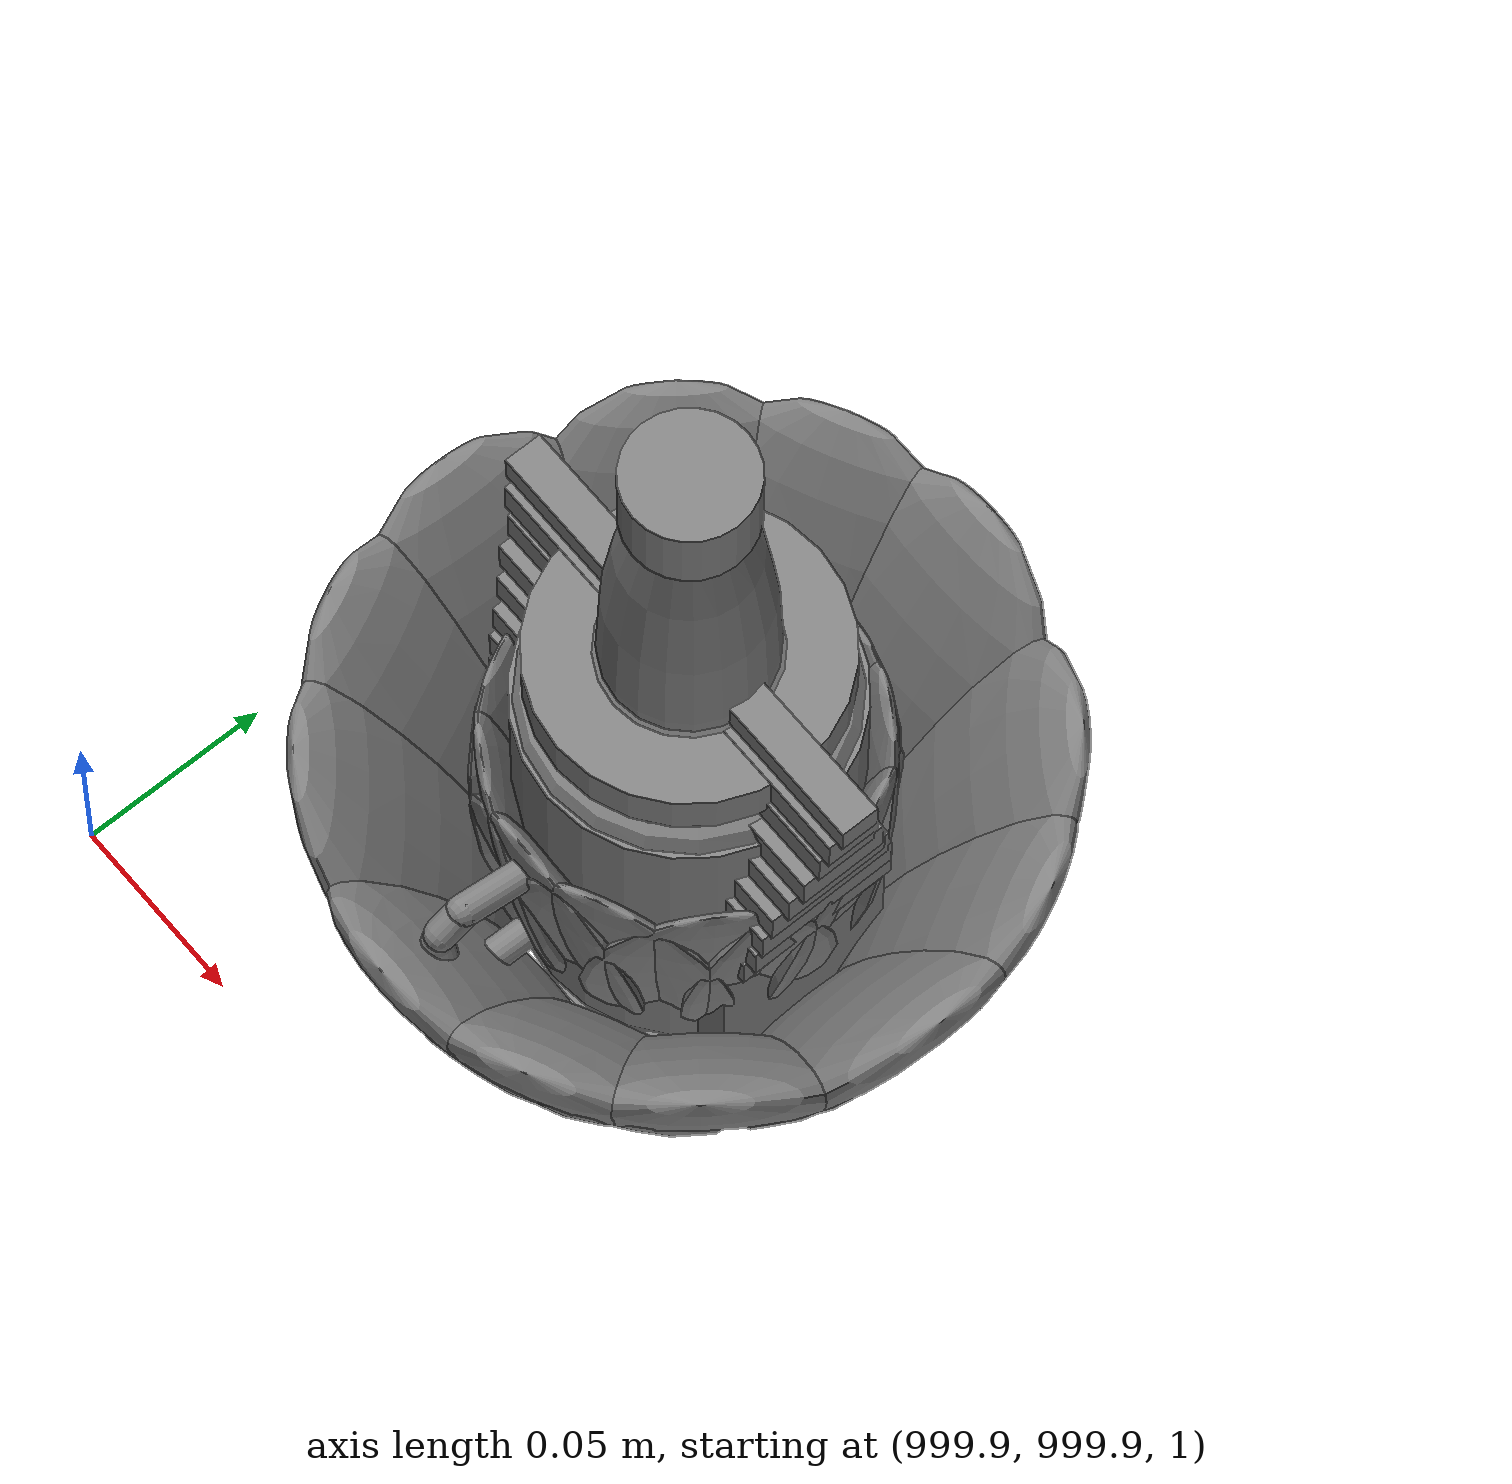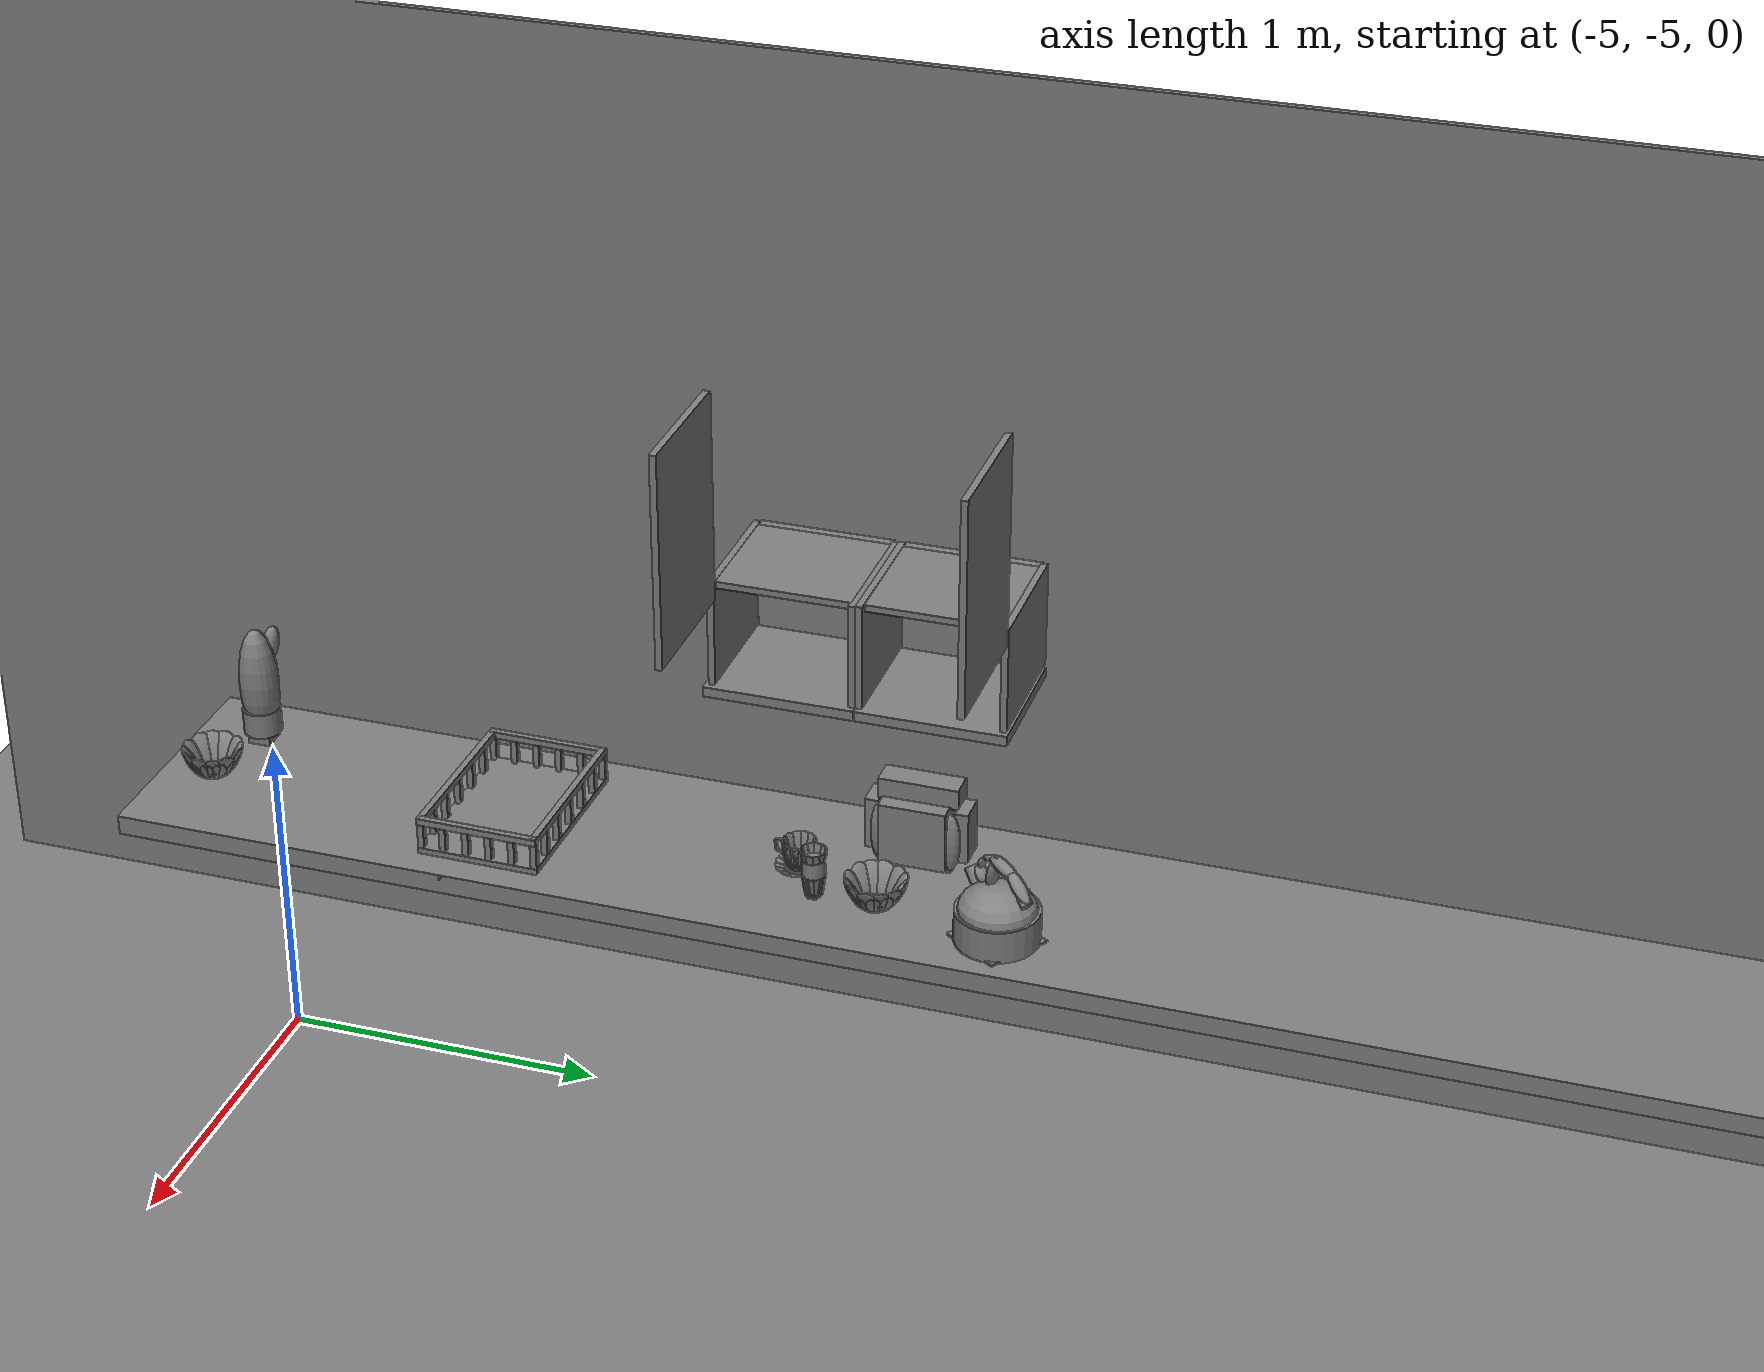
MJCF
<mujoco>
    <option gravity="0.000000000 0.000000000 -9.810000420" timestep="0.0049999999" integrator="implicitfast" density="9.8000002" viscosity="1.8000001e-05" noslip_iterations="10" iterations="100" sdf_iterations="50">
        <flag multiccd="disable"/>
    </option>
    <size memory="1000M"/>
    <compiler coordinate="local"/>
    <worldbody>
        <light cutoff="30" pos="0 1 1" dir="0 -1 -2"/>
        <light cutoff="30" pos="0 -1 1" dir="0 1 -2"/>
        <body pos="-4.685121059 -2.618872881 1.139834642" euler="-89.999885559 -75.046211243 -179.999633789" name="Interactive Objcets_shuihu">
            <geom contype="1" conaffinity="1" density="1000" type="ellipsoid" material="" rgba="0.500000000 0.500000000 0.500000000 1.000000000" solimp="0.899999976 0.949999988 0.001000000" friction="1.000000000 0.005000000 0.000100000" solref="0.020000000 1.000000000" margin="0" condim="3" group="0" pos="-0.012925148 0.115441918 -0.008463383" quat="0.573223114 -0.617213011 0.363985062 0.397464871" size="0.020000000 0.059999999 0.017999999" name="Interactive Objcets_geom_B4F9C66F_21CC_4238_B35C_9096EB4AF924"/>
            <geom contype="1" conaffinity="1" density="1000" type="cylinder" material="" rgba="0.500000000 0.500000000 0.500000000 1.000000000" solimp="0.899999976 0.949999988 0.001000000" friction="1.000000000 0.005000000 0.000100000" solref="0.020000000 1.000000000" margin="0" condim="3" group="0" pos="0.097564876 0.019223809 0.042538166" quat="0.757945418 -0.330064029 0.507527351 0.242883876" size="0.027000001 0.032499999 1.000000000" name="Interactive Objcets_geom_F3AEE372_B5A1_4278_AA72_DF723A1019F8"/>
            <geom contype="1" conaffinity="1" density="1000" type="ellipsoid" material="" rgba="0.500000000 0.500000000 0.500000000 1.000000000" solimp="0.899999976 0.949999988 0.001000000" friction="1.000000000 0.005000000 0.000100000" solref="0.020000000 1.000000000" margin="0" condim="3" group="0" pos="0.076839805 0.041928887 0.028444767" quat="0.777403057 0.260122687 0.543099582 -0.181723833" size="0.020000000 0.029999999 0.015000000" name="Interactive Objcets_geom_8E6BDB06_DA54_4692_AD9A_7700F84C5578"/>
            <geom contype="1" conaffinity="1" density="1000" type="cylinder" material="" rgba="0.500000000 0.500000000 0.500000000 1.000000000" solimp="0.899999976 0.949999988 0.001000000" friction="1.000000000 0.005000000 0.000100000" solref="0.020000000 1.000000000" margin="0" condim="3" group="0" pos="0.006719470 -0.083229184 -0.000185013" quat="0.579664290 -0.579662681 0.404957741 0.404956520" size="0.123000003 0.050000001 1.000000000" name="Interactive Objcets_geom_6C7B4388_7180_427A_903C_A496A7BB83E4"/>
            <geom contype="1" conaffinity="1" density="1000" type="ellipsoid" material="" rgba="0.500000000 0.500000000 0.500000000 1.000000000" solimp="0.899999976 0.949999988 0.001000000" friction="1.000000000 0.005000000 0.000100000" solref="0.020000000 1.000000000" margin="0" condim="3" group="0" pos="0.079775751 0.074323297 0.032407284" quat="0.807211578 -0.212389767 0.536951303 0.122406662" size="0.011000000 0.029999999 0.010000000" name="Interactive Objcets_geom_C25FF3CF_BD83_425A_A4BB_4CD0F27F1D1A"/>
            <geom contype="1" conaffinity="1" density="1000" type="cylinder" material="" rgba="0.500000000 0.500000000 0.500000000 1.000000000" solimp="0.899999976 0.949999988 0.001000000" friction="1.000000000 0.005000000 0.000100000" solref="0.020000000 1.000000000" margin="0" condim="3" group="0" pos="-0.109747589 0.061178923 -0.054180622" quat="0.791120291 -0.252390862 0.522301614 0.193980843" size="0.017000001 0.015000000 1.000000000" name="Interactive Objcets_geom_6753138A_3B57_4209_9BD1_500CFF0B7DED"/>
            <geom contype="1" conaffinity="1" density="1000" type="ellipsoid" material="" rgba="0.500000000 0.500000000 0.500000000 1.000000000" solimp="0.899999976 0.949999988 0.001000000" friction="1.000000000 0.005000000 0.000100000" solref="0.020000000 1.000000000" margin="0" condim="3" group="0" pos="0.036164403 0.116219044 0.012343884" quat="0.691036344 -0.468154669 0.465933800 0.293608427" size="0.011000000 0.039999999 0.010000000" name="Interactive Objcets_geom_8B3CB997_6D2F_4C9C_8D81_8DCE4EAD015E"/>
            <geom contype="1" conaffinity="1" density="1000" type="box" material="" rgba="0.500000000 0.500000000 0.500000000 1.000000000" solimp="0.899999976 0.949999988 0.001000000" friction="1.000000000 0.005000000 0.000100000" solref="0.020000000 1.000000000" margin="0" condim="3" group="0" pos="0.006720424 -0.132364750 -0.000183582" quat="0.579664230 -0.579662681 0.404957652 0.404956520" size="0.100000001 0.100000001 0.005000000" name="Interactive Objcets_geom_03053A5E_A470_4ECE_B8F5_79D1A1997AF7"/>
            <geom contype="1" conaffinity="1" density="1000" type="ellipsoid" material="" rgba="0.500000000 0.500000000 0.500000000 1.000000000" solimp="0.899999976 0.949999988 0.001000000" friction="1.000000000 0.005000000 0.000100000" solref="0.020000000 1.000000000" margin="0" condim="3" group="0" pos="0.006307602 -0.038442492 -0.000561237" quat="0.579664290 -0.579662681 0.404957741 0.404956520" size="0.115000002 0.115000002 0.079999998" name="Interactive Objcets_geom_CF751E07_CE7B_4161_977F_59B06DA19432"/>
            <geom contype="1" conaffinity="1" density="1000" type="ellipsoid" material="" rgba="0.500000000 0.500000000 0.500000000 1.000000000" solimp="0.899999976 0.949999988 0.001000000" friction="1.000000000 0.005000000 0.000100000" solref="0.020000000 1.000000000" margin="0" condim="3" group="0" pos="-0.081469536 0.090929627 -0.040654182" quat="0.423473954 -0.728255510 0.250199795 0.477193654" size="0.020000000 0.059999999 0.017999999" name="Interactive Objcets_geom_72659D84_3428_49C2_8FE2_B73F1C61FF7D"/>
            <geom contype="1" conaffinity="1" density="1000" type="ellipsoid" material="" rgba="0.500000000 0.500000000 0.500000000 1.000000000" solimp="0.899999976 0.949999988 0.001000000" friction="1.000000000 0.005000000 0.000100000" solref="0.020000000 1.000000000" margin="0" condim="3" group="0" pos="0.031587839 0.066336274 0.011863232" quat="0.813834965 -0.098448642 0.568551302 0.068776846" size="0.020000000 0.059999999 0.015000000" name="Interactive Objcets_geom_04D67B46_C224_4694_9BBE_0ACFB1BBD067"/>
            <freejoint name="Interactive Objcets_shuihu"/>
        </body>
        <body pos="1000.000000000 1000.000000000 1.000000000" euler="0.000000000 0.000000000 0.000000000" name="openloong_gripper_2f85_fix_base_usda_bottle_red">
            <geom contype="1" conaffinity="1" density="1000" type="ellipsoid" material="" rgba="0.500000000 0.500000000 0.500000000 1.000000000" solimp="0.899999976 0.949999988 0.001000000" friction="1.000000000 0.005000000 0.000100000" solref="0.020000000 1.000000000" margin="0" condim="3" group="0" pos="0.000000000 0.000000000 0.144284487" quat="1.000000000 0.000000000 0.000000000 0.000000000" size="0.021000000 0.021000000 0.079999998" name="openloong_gripper_2f85_fix_base_usda_geom_22C19AB2_1EB9_4377_83A9_4E9F09AEFFE9"/>
            <geom contype="1" conaffinity="1" density="1000" type="cylinder" material="" rgba="0.500000000 0.500000000 0.500000000 1.000000000" solimp="0.899999976 0.949999988 0.001000000" friction="1.000000000 0.005000000 0.000100000" solref="0.020000000 1.000000000" margin="0" condim="3" group="0" pos="0.000000000 0.000000000 0.220618963" quat="1.000000000 0.000000000 0.000000000 0.000000000" size="0.016000001 0.010000000 1.000000000" name="openloong_gripper_2f85_fix_base_usda_geom_44485FD6_C324_434F_A63A_2F9926C5085B"/>
            <geom contype="1" conaffinity="1" density="1000" type="ellipsoid" material="" rgba="0.500000000 0.500000000 0.500000000 1.000000000" solimp="0.899999976 0.949999988 0.001000000" friction="1.000000000 0.005000000 0.000100000" solref="0.020000000 1.000000000" margin="0" condim="3" group="0" pos="0.000000000 0.000000000 0.118945479" quat="1.000000000 0.000000000 0.000000000 0.000000000" size="0.030999999 0.030999999 0.029999999" name="openloong_gripper_2f85_fix_base_usda_geom_A2F1B009_2D6F_447E_B5BD_CDA7D13337A1"/>
            <geom contype="1" conaffinity="1" density="1000" type="box" material="" rgba="0.500000000 0.500000000 0.500000000 1.000000000" solimp="0.899999976 0.949999988 0.001000000" friction="1.000000000 0.005000000 0.000100000" solref="0.020000000 1.000000000" margin="0" condim="3" group="0" pos="0.000000000 0.000000000 0.002189159" quat="1.000000000 0.000000000 0.000000000 0.000000000" size="0.020000000 0.020000000 0.003000000" name="openloong_gripper_2f85_fix_base_usda_geom_A7FC70FF_5F33_436E_B48A_6D73774AED85"/>
            <geom contype="1" conaffinity="1" density="1000" type="cylinder" material="" rgba="0.500000000 0.500000000 0.500000000 1.000000000" solimp="0.899999976 0.949999988 0.001000000" friction="1.000000000 0.005000000 0.000100000" solref="0.020000000 1.000000000" margin="0" condim="3" group="0" pos="0.000000000 -0.000366211 0.060884237" quat="1.000000000 0.000000000 0.000000000 0.000000000" size="0.030999999 0.057999998 1.000000000" name="openloong_gripper_2f85_fix_base_usda_geom_12B613A5_EB56_41C9_9670_7ED66EA26D78"/>
            <freejoint name="openloong_gripper_2f85_fix_base_usda_bottle_red_joint"/>
            <site size="0.005000000 0.005000000 0.005000000" rgba="0.500000000 0.500000000 0.500000000 1.000000000" pos="0.000000000 0.000000000 0.000000000" quat="0.999961913 0.008726535 0.000000000 0.000000000" group="0" type="sphere" name="openloong_gripper_2f85_fix_base_usda_bottle_redsite"/>
        </body>
        <body pos="1000.000000000 1000.000000000 1.000000000" euler="0.000000000 0.000000000 0.000000000" name="openloong_gripper_2f85_fix_base_usda_jar_01">
            <geom contype="1" conaffinity="1" density="1000" type="box" material="" rgba="0.500000000 0.500000000 0.500000000 1.000000000" solimp="0.899999976 0.949999988 0.001000000" friction="1.000000000 0.005000000 0.000100000" solref="0.020000000 1.000000000" margin="0" condim="3" group="0" pos="0.000000000 0.000000000 0.006158113" quat="1.000000000 0.000000000 0.000000000 0.000000000" size="0.020000000 0.020000000 0.005000000" name="openloong_gripper_2f85_fix_base_usda_geom_65A87461_F103_4207_AFB1_299EC01568FB"/>
            <geom contype="1" conaffinity="1" density="1000" type="cylinder" material="" rgba="0.500000000 0.500000000 0.500000000 1.000000000" solimp="0.899999976 0.949999988 0.001000000" friction="1.000000000 0.005000000 0.000100000" solref="0.020000000 1.000000000" margin="0" condim="3" group="0" pos="0.000000000 0.000000000 0.062744498" quat="1.000000000 0.000000000 0.000000000 0.000000000" size="0.041000001 0.052999999 1.000000000" name="openloong_gripper_2f85_fix_base_usda_geom_ADE93396_350D_4692_B319_EFBD7084EE8E"/>
            <geom contype="1" conaffinity="1" density="1000" type="ellipsoid" material="" rgba="0.500000000 0.500000000 0.500000000 1.000000000" solimp="0.899999976 0.949999988 0.001000000" friction="1.000000000 0.005000000 0.000100000" solref="0.020000000 1.000000000" margin="0" condim="3" group="0" pos="0.000000000 0.000000000 0.122252703" quat="1.000000000 0.000000000 0.000000000 0.000000000" size="0.035999998 0.035999998 0.010000000" name="openloong_gripper_2f85_fix_base_usda_geom_EF8E6452_0FF5_4F7E_82AD_9FEE8F47AB19"/>
            <geom contype="1" conaffinity="1" density="1000" type="cylinder" material="" rgba="0.500000000 0.500000000 0.500000000 1.000000000" solimp="0.899999976 0.949999988 0.001000000" friction="1.000000000 0.005000000 0.000100000" solref="0.020000000 1.000000000" margin="0" condim="3" group="0" pos="0.000000000 0.000000000 0.015747190" quat="1.000000000 0.000000000 0.000000000 0.000000000" size="0.035000000 0.010000000 1.000000000" name="openloong_gripper_2f85_fix_base_usda_geom_B946D7C6_9DAE_4E3C_AC4C_09E2C97B9045"/>
            <geom contype="1" conaffinity="1" density="1000" type="ellipsoid" material="" rgba="0.500000000 0.500000000 0.500000000 1.000000000" solimp="0.899999976 0.949999988 0.001000000" friction="1.000000000 0.005000000 0.000100000" solref="0.020000000 1.000000000" margin="0" condim="3" group="0" pos="0.000000000 0.000000000 0.115815401" quat="1.000000000 0.000000000 0.000000000 0.000000000" size="0.039999999 0.039999999 0.010000000" name="openloong_gripper_2f85_fix_base_usda_geom_7523266F_8A03_4A63_A9D5_5B10B87EE0DC"/>
            <geom contype="1" conaffinity="1" density="1000" type="cylinder" material="" rgba="0.500000000 0.500000000 0.500000000 1.000000000" solimp="0.899999976 0.949999988 0.001000000" friction="1.000000000 0.005000000 0.000100000" solref="0.020000000 1.000000000" margin="0" condim="3" group="0" pos="0.000000000 0.000000000 0.133183479" quat="1.000000000 0.000000000 0.000000000 0.000000000" size="0.037999999 0.006500000 1.000000000" name="openloong_gripper_2f85_fix_base_usda_geom_B1EBFF6A_82F9_4102_B058_F5D878A0D5DC"/>
            <freejoint name="openloong_gripper_2f85_fix_base_usda_jar_01_joint"/>
            <site size="0.005000000 0.005000000 0.005000000" rgba="0.500000000 0.500000000 0.500000000 1.000000000" pos="0.000000000 0.000000000 0.000000000" quat="1.000000000 0.000000000 0.000000000 0.000000000" group="0" type="sphere" name="openloong_gripper_2f85_fix_base_usda_jar_01site"/>
        </body>
        <body pos="1000.000000000 1000.000000000 1.000000000" euler="0.000000000 0.000000000 0.000000000" name="openloong_gripper_2f85_fix_base_usda_bow_yellow_kps">
            <geom contype="1" conaffinity="1" density="1000" type="ellipsoid" material="" rgba="0.500000000 0.500000000 0.500000000 1.000000000" solimp="0.899999976 0.949999988 0.001000000" friction="1.000000000 0.005000000 0.000100000" solref="0.020000000 1.000000000" margin="0" condim="3" group="0" pos="-0.052185059 0.040283203 0.044118762" quat="0.919264615 -0.076883033 -0.225593656 -0.313287765" size="0.010000000 0.039999999 0.052000001" name="openloong_gripper_2f85_fix_base_usda_geom_B53EA8DF_D3A6_4D5D_941A_E38D1A31E74F"/>
            <geom contype="1" conaffinity="1" density="1000" type="ellipsoid" material="" rgba="0.500000000 0.500000000 0.500000000 1.000000000" solimp="0.899999976 0.949999988 0.001000000" friction="1.000000000 0.005000000 0.000100000" solref="0.020000000 1.000000000" margin="0" condim="3" group="0" pos="-0.000061035 0.065979004 0.044118762" quat="0.687598765 -0.168314874 -0.168741167 -0.685860336" size="0.010000000 0.039999999 0.052000001" name="openloong_gripper_2f85_fix_base_usda_geom_E8825A26_DB3C_4FFB_A0FE_FDC758BDB2E3"/>
            <geom contype="1" conaffinity="1" density="1000" type="box" material="" rgba="0.500000000 0.500000000 0.500000000 1.000000000" solimp="0.899999976 0.949999988 0.001000000" friction="1.000000000 0.005000000 0.000100000" solref="0.020000000 1.000000000" margin="0" condim="3" group="0" pos="0.000061035 0.000000000 -0.002001643" quat="1.000000000 0.000000000 0.000000000 0.000000000" size="0.029999999 0.029999999 0.002000000" name="openloong_gripper_2f85_fix_base_usda_geom_2546C1A0_5F0A_4314_B844_62B9949FCD8E"/>
            <geom contype="1" conaffinity="1" density="1000" type="ellipsoid" material="" rgba="0.500000000 0.500000000 0.500000000 1.000000000" solimp="0.899999976 0.949999988 0.001000000" friction="1.000000000 0.005000000 0.000100000" solref="0.020000000 1.000000000" margin="0" condim="3" group="0" pos="0.029418945 -0.059082031 0.044118762" quat="0.825555861 0.125530601 0.202597082 -0.511521280" size="0.010000000 0.039999999 0.052000001" name="openloong_gripper_2f85_fix_base_usda_geom_ED93C73E_23E8_448B_B8FB_B1ECF6B6981B"/>
            <geom contype="1" conaffinity="1" density="1000" type="ellipsoid" material="" rgba="0.500000000 0.500000000 0.500000000 1.000000000" solimp="0.899999976 0.949999988 0.001000000" friction="1.000000000 0.005000000 0.000100000" solref="0.020000000 1.000000000" margin="0" condim="3" group="0" pos="0.000244141 -0.065979004 0.044118762" quat="0.687598765 0.168314651 0.168741375 -0.685860336" size="0.010000000 0.039999999 0.052000001" name="openloong_gripper_2f85_fix_base_usda_geom_95B1925C_F607_4366_A814_FE9D4E213D2D"/>
            <geom contype="1" conaffinity="1" density="1000" type="ellipsoid" material="" rgba="0.500000000 0.500000000 0.500000000 1.000000000" solimp="0.899999976 0.949999988 0.001000000" friction="1.000000000 0.005000000 0.000100000" solref="0.020000000 1.000000000" margin="0" condim="3" group="0" pos="0.000061035 0.000000000 0.000446677" quat="1.000000000 0.000000000 0.000000000 0.000000000" size="0.039999999 0.039999999 0.002000000" name="openloong_gripper_2f85_fix_base_usda_geom_F7335913_FE9D_4401_820D_F39F65C5B0AA"/>
            <geom contype="1" conaffinity="1" density="1000" type="ellipsoid" material="" rgba="0.500000000 0.500000000 0.500000000 1.000000000" solimp="0.899999976 0.949999988 0.001000000" friction="1.000000000 0.005000000 0.000100000" solref="0.020000000 1.000000000" margin="0" condim="3" group="0" pos="0.059082031 0.029541016 0.044118762" quat="0.223252773 -0.231952220 -0.054787423 -0.945174456" size="0.010000000 0.039999999 0.052000001" name="openloong_gripper_2f85_fix_base_usda_geom_3A97FBF9_2542_4D22_A941_7AC2972C37D6"/>
            <geom contype="1" conaffinity="1" density="1000" type="ellipsoid" material="" rgba="0.500000000 0.500000000 0.500000000 1.000000000" solimp="0.899999976 0.949999988 0.001000000" friction="1.000000000 0.005000000 0.000100000" solref="0.020000000 1.000000000" margin="0" condim="3" group="0" pos="0.000061035 0.000000000 0.007335305" quat="1.000000000 0.000000000 0.000000000 0.000000000" size="0.039999999 0.039999999 0.002000000" name="openloong_gripper_2f85_fix_base_usda_geom_CFF708FC_80FD_4F89_B8EE_4881C0FD1A73"/>
            <geom contype="1" conaffinity="1" density="1000" type="ellipsoid" material="" rgba="0.500000000 0.500000000 0.500000000 1.000000000" solimp="0.899999976 0.949999988 0.001000000" friction="1.000000000 0.005000000 0.000100000" solref="0.020000000 1.000000000" margin="0" condim="3" group="0" pos="-0.029296875 0.059082031 0.044118762" quat="0.825555861 -0.125530809 -0.202596918 -0.511521280" size="0.010000000 0.039999999 0.052000001" name="openloong_gripper_2f85_fix_base_usda_geom_5B7AD85D_7D43_4039_9C70_192DF92A1C00"/>
            <geom contype="1" conaffinity="1" density="1000" type="ellipsoid" material="" rgba="0.500000000 0.500000000 0.500000000 1.000000000" solimp="0.899999976 0.949999988 0.001000000" friction="1.000000000 0.005000000 0.000100000" solref="0.020000000 1.000000000" margin="0" condim="3" group="0" pos="0.040222168 0.052368164 0.044118762" quat="0.429593176 -0.213750049 -0.105424821 -0.871002972" size="0.010000000 0.039999999 0.052000001" name="openloong_gripper_2f85_fix_base_usda_geom_37D3F0E1_9111_471B_955E_DFEE56AFFA62"/>
            <geom contype="1" conaffinity="1" density="1000" type="ellipsoid" material="" rgba="0.500000000 0.500000000 0.500000000 1.000000000" solimp="0.899999976 0.949999988 0.001000000" friction="1.000000000 0.005000000 0.000100000" solref="0.020000000 1.000000000" margin="0" condim="3" group="0" pos="0.066040039 0.000000000 0.044118762" quat="0.971183062 -0.000000156 0.238334835 0.000000030" size="0.010000000 0.039999999 0.052000001" name="openloong_gripper_2f85_fix_base_usda_geom_C2977F3F_7C1D_404F_8B37_BF3B2EFD715F"/>
            <geom contype="1" conaffinity="1" density="1000" type="ellipsoid" material="" rgba="0.500000000 0.500000000 0.500000000 1.000000000" solimp="0.899999976 0.949999988 0.001000000" friction="1.000000000 0.005000000 0.000100000" solref="0.020000000 1.000000000" margin="0" condim="3" group="0" pos="0.052307129 -0.040283203 0.044118762" quat="0.919264674 0.076882750 0.225593731 -0.313287705" size="0.010000000 0.039999999 0.052000001" name="openloong_gripper_2f85_fix_base_usda_geom_B556F0F2_8D6E_4B09_A4F4_59D7F5E50476"/>
            <geom contype="1" conaffinity="1" density="1000" type="ellipsoid" material="" rgba="0.500000000 0.500000000 0.500000000 1.000000000" solimp="0.899999976 0.949999988 0.001000000" friction="1.000000000 0.005000000 0.000100000" solref="0.020000000 1.000000000" margin="0" condim="3" group="0" pos="-0.065917969 0.000000000 0.044118762" quat="0.971183062 -0.000000142 -0.238334835 0.000000030" size="0.010000000 0.039999999 0.052000001" name="openloong_gripper_2f85_fix_base_usda_geom_890B8363_D222_4FAD_A592_5C257A2E002D"/>
            <geom contype="1" conaffinity="1" density="1000" type="ellipsoid" material="" rgba="0.500000000 0.500000000 0.500000000 1.000000000" solimp="0.899999976 0.949999988 0.001000000" friction="1.000000000 0.005000000 0.000100000" solref="0.020000000 1.000000000" margin="0" condim="3" group="0" pos="-0.058898926 -0.029541016 0.044118762" quat="0.223252758 0.231952101 0.054787733 -0.945174575" size="0.010000000 0.039999999 0.052000001" name="openloong_gripper_2f85_fix_base_usda_geom_9EEB6901_646E_4516_B96B_18F006384D93"/>
            <geom contype="1" conaffinity="1" density="1000" type="ellipsoid" material="" rgba="0.500000000 0.500000000 0.500000000 1.000000000" solimp="0.899999976 0.949999988 0.001000000" friction="1.000000000 0.005000000 0.000100000" solref="0.020000000 1.000000000" margin="0" condim="3" group="0" pos="-0.040100098 -0.052368164 0.044118762" quat="0.429593235 0.213749886 0.105425082 -0.871003032" size="0.010000000 0.039999999 0.052000001" name="openloong_gripper_2f85_fix_base_usda_geom_BA3149C0_EE02_4ABD_8565_373AE82EF6DF"/>
            <freejoint name="openloong_gripper_2f85_fix_base_usda_bow_yellow_kps_joint"/>
            <site size="0.005000000 0.005000000 0.005000000" rgba="0.500000000 0.500000000 0.500000000 1.000000000" pos="0.000000000 0.000000000 0.000000000" quat="0.999961913 0.008726534 0.000000000 0.000000000" group="0" type="sphere" name="openloong_gripper_2f85_fix_base_usda_bow_yellow_kps"/>
        </body>
        <body pos="1000.000000000 1000.000000000 1.000000000" euler="0.000000000 0.000000000 0.000000000" name="openloong_gripper_2f85_fix_base_usda_coffeecup_white_kps">
            <geom contype="1" conaffinity="1" density="1000" type="capsule" material="" rgba="0.500000000 0.500000000 0.500000000 1.000000000" solimp="0.899999976 0.949999988 0.001000000" friction="1.000000000 0.005000000 0.000100000" solref="0.020000000 1.000000000" margin="0" condim="3" group="0" pos="-0.000854492 -0.065795898 0.050029993" quat="0.343559504 -0.613204718 0.626912475 0.336047262" size="0.004000000 0.005000000 1.000000000" name="openloong_gripper_2f85_fix_base_usda_geom_661D9795_942A_4C32_9FAF_147C3152D087"/>
            <geom contype="1" conaffinity="1" density="1000" type="ellipsoid" material="" rgba="0.500000000 0.500000000 0.500000000 1.000000000" solimp="0.899999976 0.949999988 0.001000000" friction="1.000000000 0.005000000 0.000100000" solref="0.020000000 1.000000000" margin="0" condim="3" group="0" pos="-0.000793457 -0.038452148 0.048040152" quat="0.711656272 0.066323131 -0.067805752 0.696095467" size="0.005000000 0.029999999 0.048999999" name="openloong_gripper_2f85_fix_base_usda_geom_9BD586F4_008C_452D_81F8_7CC9A00EC186"/>
            <geom contype="1" conaffinity="1" density="1000" type="ellipsoid" material="" rgba="0.500000000 0.500000000 0.500000000 1.000000000" solimp="0.899999976 0.949999988 0.001000000" friction="1.000000000 0.005000000 0.000100000" solref="0.020000000 1.000000000" margin="0" condim="3" group="0" pos="0.037719727 -0.001892090 0.048040152" quat="0.995387912 0.001371633 0.094835162 -0.014391154" size="0.005000000 0.029999999 0.048999999" name="openloong_gripper_2f85_fix_base_usda_geom_979E8937_C333_42E4_8B37_A1A6D653268E"/>
            <geom contype="1" conaffinity="1" density="1000" type="ellipsoid" material="" rgba="0.500000000 0.500000000 0.500000000 1.000000000" solimp="0.899999976 0.949999988 0.001000000" friction="1.000000000 0.005000000 0.000100000" solref="0.020000000 1.000000000" margin="0" condim="3" group="0" pos="0.033996582 0.015502930 0.048040152" quat="0.970659733 -0.021051638 0.092478797 0.220962167" size="0.005000000 0.029999999 0.048999999" name="openloong_gripper_2f85_fix_base_usda_geom_2B50ED88_D5C4_4E54_A2EA_550077BAE3C3"/>
            <geom contype="1" conaffinity="1" density="1000" type="box" material="" rgba="0.500000000 0.500000000 0.500000000 1.000000000" solimp="0.899999976 0.949999988 0.001000000" friction="1.000000000 0.005000000 0.000100000" solref="0.020000000 1.000000000" margin="0" condim="3" group="0" pos="0.000793457 -0.000183105 0.000156164" quat="0.714879215 0.000000000 0.000000000 0.699247897" size="0.020000000 0.020000000 0.002000000" name="openloong_gripper_2f85_fix_base_usda_geom_AC509955_9B75_4309_8684_980CDD5842D6"/>
            <geom contype="1" conaffinity="1" density="1000" type="ellipsoid" material="" rgba="0.500000000 0.500000000 0.500000000 1.000000000" solimp="0.899999976 0.949999988 0.001000000" friction="1.000000000 0.005000000 0.000100000" solref="0.020000000 1.000000000" margin="0" condim="3" group="0" pos="-0.019409180 -0.033081055 0.048040152" quat="0.866879702 0.046630561 -0.082595348 0.489411235" size="0.005000000 0.029999999 0.048999999" name="openloong_gripper_2f85_fix_base_usda_geom_970B31F4_6370_4432_91EB_CB71F902E93E"/>
            <geom contype="1" conaffinity="1" density="1000" type="ellipsoid" material="" rgba="0.500000000 0.500000000 0.500000000 1.000000000" solimp="0.899999976 0.949999988 0.001000000" friction="1.000000000 0.005000000 0.000100000" solref="0.020000000 1.000000000" margin="0" condim="3" group="0" pos="-0.016052246 0.033264160 0.048040152" quat="0.840792537 -0.050782297 -0.080109790 -0.532983541" size="0.005000000 0.029999999 0.048999999" name="openloong_gripper_2f85_fix_base_usda_geom_F26968C3_73CB_4659_AD64_A9FFE06C537F"/>
            <geom contype="1" conaffinity="1" density="1000" type="capsule" material="" rgba="0.500000000 0.500000000 0.500000000 1.000000000" solimp="0.899999976 0.949999988 0.001000000" friction="1.000000000 0.005000000 0.000100000" solref="0.020000000 1.000000000" margin="0" condim="3" group="0" pos="-0.000549316 -0.053527832 0.046825886" quat="0.505496025 -0.494442940 0.505495846 0.494442940" size="0.004000000 0.005000000 1.000000000" name="openloong_gripper_2f85_fix_base_usda_geom_7087868B_2740_4DAC_99F0_F7D28555F59C"/>
            <geom contype="1" conaffinity="1" density="1000" type="ellipsoid" material="" rgba="0.500000000 0.500000000 0.500000000 1.000000000" solimp="0.899999976 0.949999988 0.001000000" friction="1.000000000 0.005000000 0.000100000" solref="0.020000000 1.000000000" margin="0" condim="3" group="0" pos="-0.032104492 0.018920898 0.048040152" quat="0.958129764 -0.025742561 -0.091288343 -0.270168930" size="0.005000000 0.029999999 0.048999999" name="openloong_gripper_2f85_fix_base_usda_geom_C1B6BBF9_7A80_4DCA_BCDB_EE47E7E17F9D"/>
            <geom contype="1" conaffinity="1" density="1000" type="ellipsoid" material="" rgba="0.500000000 0.500000000 0.500000000 1.000000000" solimp="0.899999976 0.949999988 0.001000000" friction="1.000000000 0.005000000 0.000100000" solref="0.020000000 1.000000000" margin="0" condim="3" group="0" pos="-0.037597656 0.000305176 0.048040152" quat="0.995387554 -0.001371440 -0.094839431 -0.014389008" size="0.005000000 0.029999999 0.048999999" name="openloong_gripper_2f85_fix_base_usda_geom_837013A0_6DC0_44A7_AA23_464DA6CDC1A2"/>
            <geom contype="1" conaffinity="1" density="1000" type="capsule" material="" rgba="0.500000000 0.500000000 0.500000000 1.000000000" solimp="0.899999976 0.949999988 0.001000000" friction="1.000000000 0.005000000 0.000100000" solref="0.020000000 1.000000000" margin="0" condim="3" group="0" pos="-0.000366211 -0.043762207 0.044118762" quat="0.260488123 -0.651174724 0.665731549 0.254792154" size="0.004000000 0.003000000 1.000000000" name="openloong_gripper_2f85_fix_base_usda_geom_8F9CD02C_3744_4C82_94B2_03826B323877"/>
            <geom contype="1" conaffinity="1" density="1000" type="capsule" material="" rgba="0.500000000 0.500000000 0.500000000 1.000000000" solimp="0.899999976 0.949999988 0.001000000" friction="1.000000000 0.005000000 0.000100000" solref="0.020000000 1.000000000" margin="0" condim="3" group="0" pos="-0.000915527 -0.068542480 0.082936406" quat="0.624995589 -0.339446366 0.347034454 0.611329615" size="0.004000000 0.004000000 1.000000000" name="openloong_gripper_2f85_fix_base_usda_geom_D7C71751_3461_4EE8_857F_A37ED9EDC873"/>
            <geom contype="1" conaffinity="1" density="1000" type="ellipsoid" material="" rgba="0.500000000 0.500000000 0.500000000 1.000000000" solimp="0.899999976 0.949999988 0.001000000" friction="1.000000000 0.005000000 0.000100000" solref="0.020000000 1.000000000" margin="0" condim="3" group="0" pos="0.016113281 -0.034851074 0.048040152" quat="0.840793252 0.050779939 0.080106191 -0.532983422" size="0.005000000 0.029999999 0.048999999" name="openloong_gripper_2f85_fix_base_usda_geom_287044D7_81D9_4774_B524_2B43730CAE69"/>
            <geom contype="1" conaffinity="1" density="1000" type="ellipsoid" material="" rgba="0.500000000 0.500000000 0.500000000 1.000000000" solimp="0.899999976 0.949999988 0.001000000" friction="1.000000000 0.005000000 0.000100000" solref="0.020000000 1.000000000" margin="0" condim="3" group="0" pos="0.000854492 0.036865234 0.048040152" quat="0.711656570 -0.066320375 0.067802906 0.696095705" size="0.005000000 0.029999999 0.048999999" name="openloong_gripper_2f85_fix_base_usda_geom_B6EB6C68_C72C_4061_A868_65F642C6179F"/>
            <geom contype="1" conaffinity="1" density="1000" type="ellipsoid" material="" rgba="0.500000000 0.500000000 0.500000000 1.000000000" solimp="0.899999976 0.949999988 0.001000000" friction="1.000000000 0.005000000 0.000100000" solref="0.020000000 1.000000000" margin="0" condim="3" group="0" pos="-0.033935547 -0.017089844 0.048040152" quat="0.970659137 0.021052625 -0.092483103 0.220962465" size="0.005000000 0.029999999 0.048999999" name="openloong_gripper_2f85_fix_base_usda_geom_F852714F_4506_4221_809C_A5FB86229ACB"/>
            <geom contype="1" conaffinity="1" density="1000" type="ellipsoid" material="" rgba="0.500000000 0.500000000 0.500000000 1.000000000" solimp="0.899999976 0.949999988 0.001000000" friction="1.000000000 0.005000000 0.000100000" solref="0.020000000 1.000000000" margin="0" condim="3" group="0" pos="0.019531250 0.031494141 0.048040152" quat="0.866880119 -0.046628602 0.082591817 0.489411235" size="0.005000000 0.029999999 0.048999999" name="openloong_gripper_2f85_fix_base_usda_geom_6D10C393_2716_46E8_89B1_70BC9DFDE8D2"/>
            <geom contype="1" conaffinity="1" density="1000" type="ellipsoid" material="" rgba="0.500000000 0.500000000 0.500000000 1.000000000" solimp="0.899999976 0.949999988 0.001000000" friction="1.000000000 0.005000000 0.000100000" solref="0.020000000 1.000000000" margin="0" condim="3" group="0" pos="0.032165527 -0.020507812 0.048040152" quat="0.958128154 0.025740955 0.091285400 -0.270175666" size="0.005000000 0.029999999 0.048999999" name="openloong_gripper_2f85_fix_base_usda_geom_0A72F8E7_5136_44D0_ADD8_26584D8D2014"/>
            <geom contype="1" conaffinity="1" density="1000" type="capsule" material="" rgba="0.500000000 0.500000000 0.500000000 1.000000000" solimp="0.899999976 0.949999988 0.001000000" friction="1.000000000 0.005000000 0.000100000" solref="0.020000000 1.000000000" margin="0" condim="3" group="0" pos="-0.000610352 -0.056823730 0.083572865" quat="0.452654332 -0.541215360 0.553313971 0.442756712" size="0.004000000 0.009000000 1.000000000" name="openloong_gripper_2f85_fix_base_usda_geom_859BE82A_3F44_4424_A626_5A7F2E8F36C3"/>
            <geom contype="1" conaffinity="1" density="1000" type="ellipsoid" material="" rgba="0.500000000 0.500000000 0.500000000 1.000000000" solimp="0.899999976 0.949999988 0.001000000" friction="1.000000000 0.005000000 0.000100000" solref="0.020000000 1.000000000" margin="0" condim="3" group="0" pos="0.000061035 -0.000183105 0.001848221" quat="0.714879215 0.000000000 0.000000000 0.699247897" size="0.029999999 0.029999999 0.001000000" name="openloong_gripper_2f85_fix_base_usda_geom_A85A6F87_690B_42B5_91AC_4CA0D95DAE9E"/>
            <geom contype="1" conaffinity="1" density="1000" type="capsule" material="" rgba="0.500000000 0.500000000 0.500000000 1.000000000" solimp="0.899999976 0.949999988 0.001000000" friction="1.000000000 0.005000000 0.000100000" solref="0.020000000 1.000000000" margin="0" condim="3" group="0" pos="-0.000976562 -0.071838379 0.066101432" quat="0.031849027 -0.698553741 0.714169443 0.031152546" size="0.004000000 0.012000000 1.000000000" name="openloong_gripper_2f85_fix_base_usda_geom_BEDF5944_70B0_44EC_BE7F_281CC73465A7"/>
            <freejoint name="openloong_gripper_2f85_fix_base_usda_coffeecup_white_kps_joint"/>
            <site size="0.005000000 0.005000000 0.005000000" rgba="0.500000000 0.500000000 0.500000000 1.000000000" pos="0.000000000 0.000000000 0.000000000" quat="0.999961913 0.008726534 0.000000000 0.000000000" group="0" type="sphere" name="openloong_gripper_2f85_fix_base_usda_coffeecup_white_kps"/>
        </body>
        <body pos="1000.000000000 1000.000000000 1.000000000" euler="0.000000000 0.000000000 0.000000000" name="openloong_gripper_2f85_fix_base_usda_salt">
            <geom contype="1" conaffinity="1" density="1000" type="box" material="" rgba="0.500000000 0.500000000 0.500000000 1.000000000" solimp="0.899999976 0.949999988 0.001000000" friction="1.000000000 0.005000000 0.000100000" solref="0.020000000 1.000000000" margin="0" condim="3" group="0" pos="0.000305176 0.000000000 0.084862232" quat="1.000000000 0.000000000 0.000000000 0.000000000" size="0.048999999 0.018999999 0.005000000" name="openloong_gripper_2f85_fix_base_usda_geom_93EAB0E0_DA73_4435_A2BB_36987F0C3EBD"/>
            <geom contype="1" conaffinity="1" density="1000" type="box" material="" rgba="0.500000000 0.500000000 0.500000000 1.000000000" solimp="0.899999976 0.949999988 0.001000000" friction="1.000000000 0.005000000 0.000100000" solref="0.020000000 1.000000000" margin="0" condim="3" group="0" pos="0.000305176 0.000000000 0.104564309" quat="1.000000000 0.000000000 0.000000000 0.000000000" size="0.052000001 0.014000000 0.005000000" name="openloong_gripper_2f85_fix_base_usda_geom_5A255C65_3FC8_440A_A5F0_4BAE27FD5958"/>
            <geom contype="1" conaffinity="1" density="1000" type="box" material="" rgba="0.500000000 0.500000000 0.500000000 1.000000000" solimp="0.899999976 0.949999988 0.001000000" friction="1.000000000 0.005000000 0.000100000" solref="0.020000000 1.000000000" margin="0" condim="3" group="0" pos="0.000305176 0.000000000 0.114487171" quat="1.000000000 0.000000000 0.000000000 0.000000000" size="0.054000001 0.011500000 0.005000000" name="openloong_gripper_2f85_fix_base_usda_geom_EAAC3F63_9B2E_4CDC_BF2C_2F6D2E69ECF6"/>
            <geom contype="1" conaffinity="1" density="1000" type="box" material="" rgba="0.500000000 0.500000000 0.500000000 1.000000000" solimp="0.899999976 0.949999988 0.001000000" friction="1.000000000 0.005000000 0.000100000" solref="0.020000000 1.000000000" margin="0" condim="3" group="0" pos="0.000305176 0.000000000 0.075103164" quat="1.000000000 0.000000000 0.000000000 0.000000000" size="0.048000000 0.020000000 0.005000000" name="openloong_gripper_2f85_fix_base_usda_geom_20CC6D0C_0FBA_4A34_97BC_FCBAC4062A09"/>
            <geom contype="1" conaffinity="1" density="1000" type="box" material="" rgba="0.500000000 0.500000000 0.500000000 1.000000000" solimp="0.899999976 0.949999988 0.001000000" friction="1.000000000 0.005000000 0.000100000" solref="0.020000000 1.000000000" margin="0" condim="3" group="0" pos="0.000305176 0.000000000 0.134892464" quat="1.000000000 0.000000000 0.000000000 0.000000000" size="0.057000000 0.007000000 0.005000000" name="openloong_gripper_2f85_fix_base_usda_geom_9714070B_E54E_4316_9D43_CF802E206E99"/>
            <geom contype="1" conaffinity="1" density="1000" type="box" material="" rgba="0.500000000 0.500000000 0.500000000 1.000000000" solimp="0.899999976 0.949999988 0.001000000" friction="1.000000000 0.005000000 0.000100000" solref="0.020000000 1.000000000" margin="0" condim="3" group="0" pos="0.000305176 0.000000000 0.094920278" quat="1.000000000 0.000000000 0.000000000 0.000000000" size="0.050000001 0.017000001 0.005000000" name="openloong_gripper_2f85_fix_base_usda_geom_8C2190EA_BE00_441E_8E8A_0D54BBE494D5"/>
            <geom contype="1" conaffinity="1" density="1000" type="box" material="" rgba="0.500000000 0.500000000 0.500000000 1.000000000" solimp="0.899999976 0.949999988 0.001000000" friction="1.000000000 0.005000000 0.000100000" solref="0.020000000 1.000000000" margin="0" condim="3" group="0" pos="0.000305176 0.000000000 0.065204859" quat="1.000000000 0.000000000 0.000000000 0.000000000" size="0.045000002 0.021000000 0.005000000" name="openloong_gripper_2f85_fix_base_usda_geom_B55ADB0E_1B42_404E_BE07_8D84C84516DB"/>
            <geom contype="1" conaffinity="1" density="1000" type="box" material="" rgba="0.500000000 0.500000000 0.500000000 1.000000000" solimp="0.899999976 0.949999988 0.001000000" friction="1.000000000 0.005000000 0.000100000" solref="0.020000000 1.000000000" margin="0" condim="3" group="0" pos="0.000305176 0.000000000 0.144135714" quat="1.000000000 0.000000000 0.000000000 0.000000000" size="0.059000000 0.005000000 0.004000000" name="openloong_gripper_2f85_fix_base_usda_geom_C42D983C_8A90_48DB_BD22_088A1D827C88"/>
            <geom contype="1" conaffinity="1" density="1000" type="box" material="" rgba="0.500000000 0.500000000 0.500000000 1.000000000" solimp="0.899999976 0.949999988 0.001000000" friction="1.000000000 0.005000000 0.000100000" solref="0.020000000 1.000000000" margin="0" condim="3" group="0" pos="0.000000000 0.000000000 0.031593561" quat="1.000000000 0.000000000 0.000000000 0.000000000" size="0.041999999 0.024000000 0.029999999" name="openloong_gripper_2f85_fix_base_usda_geom_5317905A_ABCF_4D6B_8C89_511234FBB04E"/>
            <geom contype="1" conaffinity="1" density="1000" type="box" material="" rgba="0.500000000 0.500000000 0.500000000 1.000000000" solimp="0.899999976 0.949999988 0.001000000" friction="1.000000000 0.005000000 0.000100000" solref="0.020000000 1.000000000" margin="0" condim="3" group="0" pos="0.000305176 0.000000000 0.124608755" quat="1.000000000 0.000000000 0.000000000 0.000000000" size="0.055000000 0.008000000 0.005000000" name="openloong_gripper_2f85_fix_base_usda_geom_2F791308_D4DF_4765_B157_86B44C9D05E4"/>
            <freejoint name="openloong_gripper_2f85_fix_base_usda_salt_joint"/>
            <site size="0.005000000 0.005000000 0.005000000" rgba="0.500000000 0.500000000 0.500000000 1.000000000" pos="0.000000000 0.000000000 0.000000000" quat="1.000000000 0.000000000 0.000000000 0.000000000" group="0" type="sphere" name="openloong_gripper_2f85_fix_base_usda_saltsite"/>
        </body>
        <body pos="0.000000000 0.000000000 0.000000000" euler="0.000000000 0.000000000 0.000000000" name="Static Objcets_Static Objcets">
            <geom contype="1" conaffinity="1" density="1000" type="box" material="" rgba="0.500000000 0.500000000 0.500000000 1.000000000" solimp="0.899999976 0.949999988 0.001000000" friction="1.000000000 0.005000000 0.000100000" solref="0.020000000 1.000000000" margin="0" condim="3" group="0" pos="-4.999745846 -3.087441683 1.763863802" quat="0.707107067 0.707106471 0.000000000 0.000000000" size="0.200000003 0.159999996 0.010000000" name="Static Objcets_geom_2A6C00E4_8DBC_4EAF_9CE9_305A3124A027"/>
            <geom contype="1" conaffinity="1" density="1000" type="box" material="" rgba="0.500000000 0.500000000 0.500000000 1.000000000" solimp="0.899999976 0.949999988 0.001000000" friction="1.000000000 0.005000000 0.000100000" solref="0.020000000 1.000000000" margin="0" condim="3" group="0" pos="-5.189302921 -3.293644905 1.760152459" quat="0.707107067 0.707106471 0.000000000 0.000000000" size="0.025000000 0.159999996 0.200000003" name="Static Objcets_geom_5F5A187F_CC6E_4C53_9E6C_5D9AE4F2CEED"/>
            <geom contype="1" conaffinity="1" density="1000" type="box" material="" rgba="0.500000000 0.500000000 0.500000000 1.000000000" solimp="0.899999976 0.949999988 0.001000000" friction="1.000000000 0.005000000 0.000100000" solref="0.020000000 1.000000000" margin="0" condim="3" group="0" pos="-4.979488373 -3.297635794 1.591412544" quat="0.707106829 0.707106709 0.000000000 0.000000000" size="0.200000003 0.015000000 0.219999999" name="Static Objcets_geom_D05B3FD1_79F6_4E02_8AD1_3A7051522F21"/>
            <geom contype="1" conaffinity="1" density="1000" type="box" material="" rgba="0.500000000 0.500000000 0.500000000 1.000000000" solimp="0.899999976 0.949999988 0.001000000" friction="1.000000000 0.005000000 0.000100000" solref="0.020000000 1.000000000" margin="0" condim="3" group="0" pos="-4.999745846 -3.497932911 1.764780521" quat="0.707107067 0.707106471 0.000000000 0.000000000" size="0.200000003 0.159999996 0.010000000" name="Static Objcets_geom_FB5EE92A_D982_44AA_8AB4_AFFFDB559179"/>
            <geom contype="1" conaffinity="1" density="1000" type="box" material="" rgba="0.500000000 0.500000000 0.500000000 1.000000000" solimp="0.899999976 0.949999988 0.001000000" friction="1.000000000 0.005000000 0.000100000" solref="0.020000000 1.000000000" margin="0" condim="3" group="0" pos="-5.000125408 -3.294431210 1.913951039" quat="0.707107067 0.707106471 0.000000000 0.000000000" size="0.180000007 0.010000000 0.200000003" name="Static Objcets_geom_8341BA6B_CB8E_4D6C_BB9D_907FE39035B8"/>
            <geom contype="1" conaffinity="1" density="1000" type="box" material="" rgba="0.500000000 0.500000000 0.500000000 1.000000000" solimp="0.899999976 0.949999988 0.001000000" friction="1.000000000 0.005000000 0.000100000" solref="0.020000000 1.000000000" margin="0" condim="3" group="0" pos="-4.999745846 -3.066934109 1.765979409" quat="0.707107067 0.707106471 0.000000000 0.000000000" size="0.200000003 0.159999996 0.010000000" name="Static Objcets_geom_748659FB_F4D8_465D_B267_63BEB988F925"/>
            <geom contype="1" conaffinity="1" density="1000" type="box" material="" rgba="0.500000000 0.500000000 0.500000000 1.000000000" solimp="0.899999976 0.949999988 0.001000000" friction="1.000000000 0.005000000 0.000100000" solref="0.020000000 1.000000000" margin="0" condim="3" group="0" pos="-5.189302921 -2.861564636 1.760152102" quat="0.707107067 0.707106471 0.000000000 0.000000000" size="0.025000000 0.159999996 0.200000003" name="Static Objcets_geom_078FA1F8_4BE1_41E4_BEC0_B3B89AC7007B"/>
            <geom contype="1" conaffinity="1" density="1000" type="box" material="" rgba="0.500000000 0.500000000 0.500000000 1.000000000" solimp="0.899999976 0.949999988 0.001000000" friction="1.000000000 0.005000000 0.000100000" solref="0.020000000 1.000000000" margin="0" condim="3" group="0" pos="-5.000125408 -2.861802340 1.913950682" quat="0.707107067 0.707106471 0.000000000 0.000000000" size="0.180000007 0.010000000 0.200000003" name="Static Objcets_geom_587B677E_B01E_425A_8602_036DEEC71ED0"/>
            <geom contype="1" conaffinity="1" density="1000" type="box" material="" rgba="0.500000000 0.500000000 0.500000000 1.000000000" solimp="0.899999976 0.949999988 0.001000000" friction="1.000000000 0.005000000 0.000100000" solref="0.020000000 1.000000000" margin="0" condim="3" group="0" pos="-4.979488373 -2.855390549 1.591412187" quat="0.707106709 0.707106769 0.000000000 0.000000000" size="0.200000003 0.015000000 0.219999999" name="Static Objcets_geom_E2CE24A5_279A_4406_B362_D7FE82EC8B63"/>
            <geom contype="1" conaffinity="1" density="1000" type="box" material="" rgba="0.500000000 0.500000000 0.500000000 1.000000000" solimp="0.899999976 0.949999988 0.001000000" friction="1.000000000 0.005000000 0.000100000" solref="0.020000000 1.000000000" margin="0" condim="3" group="0" pos="-4.999745846 -2.653569937 1.764779806" quat="0.707107067 0.707106471 0.000000000 0.000000000" size="0.200000003 0.159999996 0.010000000" name="Static Objcets_geom_3356365A_1AC3_473B_87F8_CD988779A199"/>
            <geom contype="1" conaffinity="1" density="1000" type="box" material="" rgba="0.500000000 0.500000000 0.500000000 1.000000000" solimp="0.899999976 0.949999988 0.001000000" friction="1.000000000 0.005000000 0.000100000" solref="0.020000000 1.000000000" margin="0" condim="3" group="0" pos="-0.720102787 0.222944975 -1.102830648" quat="0.000000954 1.000000000 0.000000000 0.000000000" size="8.000000000 8.000000000 0.010000000" name="Static Objcets_geom_4940BC6B_56DB_4E8A_90C4_F4412FDCCE95"/>
            <geom contype="1" conaffinity="1" density="1000" type="box" material="" rgba="0.500000000 0.500000000 0.500000000 1.000000000" solimp="0.899999976 0.949999988 0.001000000" friction="1.000000000 0.005000000 0.000100000" solref="0.020000000 1.000000000" margin="0" condim="3" group="0" pos="-4.873187065 -2.461376429 0.977675021" quat="0.707107067 0.707106471 0.000000000 0.000000000" size="0.370000005 0.029999999 2.799999952" name="Static Objcets_geom_CA6DA458_3F1A_4066_BA43_365F5CAF93A2"/>
            <geom contype="1" conaffinity="1" density="1000" type="box" material="" rgba="0.500000000 0.500000000 0.500000000 1.000000000" solimp="0.899999976 0.949999988 0.001000000" friction="1.000000000 0.005000000 0.000100000" solref="0.020000000 1.000000000" margin="0" condim="3" group="0" pos="-5.244853973 -2.375543594 1.820221663" quat="0.707107008 0.707106531 0.000000000 0.000000000" size="0.010000000 1.500000000 3.700000048" name="Static Objcets_geom_5073B03E_C721_412F_B6FB_803B8785181E"/>
        </body>
        <body pos="-4.827295780 -3.287638187 1.074643731" euler="0.000000000 0.000000000 89.999992371" name="Interactive Objcets_coffeecup_01">
            <geom contype="1" conaffinity="1" density="1000" type="ellipsoid" material="" rgba="0.500000000 0.500000000 0.500000000 1.000000000" solimp="0.899999976 0.949999988 0.001000000" friction="1.000000000 0.005000000 0.000100000" solref="0.020000000 1.000000000" margin="0" condim="3" group="0" pos="0.068445444 0.017385960 0.002976775" quat="0.228377223 -0.092319682 -0.021759447 -0.968941331" size="0.005000000 0.029999999 0.048999999" name="Interactive Objcets_geom_4AE24486_73DB_4A43_8ED7_168CC5385F0A"/>
            <geom contype="1" conaffinity="1" density="1000" type="capsule" material="" rgba="0.500000000 0.500000000 0.500000000 1.000000000" solimp="0.899999976 0.949999988 0.001000000" friction="1.000000000 0.005000000 0.000100000" solref="0.020000000 1.000000000" margin="0" condim="3" group="0" pos="-0.008219719 0.000000000 -0.000944734" quat="0.364379913 0.000000063 0.931250274 -0.000000063" size="0.004000000 0.003000000 1.000000000" name="Interactive Objcets_geom_189E5676_B678_42B9_90BE_CD9AE0AE69DE"/>
            <geom contype="1" conaffinity="1" density="1000" type="ellipsoid" material="" rgba="0.500000000 0.500000000 0.500000000 1.000000000" solimp="0.899999976 0.949999988 0.001000000" friction="1.000000000 0.005000000 0.000100000" solref="0.020000000 1.000000000" margin="0" condim="3" group="0" pos="0.001010895 -0.016271591 0.002976775" quat="0.228377163 0.092315644 0.021758538 -0.968941689" size="0.005000000 0.029999999 0.048999999" name="Interactive Objcets_geom_1C77A00C_ACA9_490D_9E65_9B38EB33D48F"/>
            <geom contype="1" conaffinity="1" density="1000" type="ellipsoid" material="" rgba="0.500000000 0.500000000 0.500000000 1.000000000" solimp="0.899999976 0.949999988 0.001000000" friction="1.000000000 0.005000000 0.000100000" solref="0.020000000 1.000000000" margin="0" condim="3" group="0" pos="0.034471050 -0.037125111 0.002976775" quat="0.701517045 0.067293778 0.066836871 -0.706313014" size="0.005000000 0.029999999 0.048999999" name="Interactive Objcets_geom_6732AF50_741B_4D75_95ED_25C95B93133A"/>
            <geom contype="1" conaffinity="1" density="1000" type="ellipsoid" material="" rgba="0.500000000 0.500000000 0.500000000 1.000000000" solimp="0.899999976 0.949999988 0.001000000" friction="1.000000000 0.005000000 0.000100000" solref="0.020000000 1.000000000" margin="0" condim="3" group="0" pos="0.035336256 0.000558376 -0.045152068" quat="0.999999881 0.000000000 0.000000000 0.000000000" size="0.029999999 0.029999999 0.001000000" name="Interactive Objcets_geom_930496BF_81BE_4C66_BE7F_8FA608ED1D56"/>
            <geom contype="1" conaffinity="1" density="1000" type="capsule" material="" rgba="0.500000000 0.500000000 0.500000000 1.000000000" solimp="0.899999976 0.949999988 0.001000000" friction="1.000000000 0.005000000 0.000100000" solref="0.020000000 1.000000000" margin="0" condim="3" group="0" pos="-0.033022881 0.000000000 0.037873149" quat="0.874267220 0.000000042 0.485444903 -0.000000084" size="0.004000000 0.004000000 1.000000000" name="Interactive Objcets_geom_E29706BA_8B17_4E19_8FD8_11663B28C859"/>
            <geom contype="1" conaffinity="1" density="1000" type="capsule" material="" rgba="0.500000000 0.500000000 0.500000000 1.000000000" solimp="0.899999976 0.949999988 0.001000000" friction="1.000000000 0.005000000 0.000100000" solref="0.020000000 1.000000000" margin="0" condim="3" group="0" pos="-0.018014431 0.000000000 0.001762271" quat="0.707106769 -0.000000004 0.707106709 -0.000000088" size="0.004000000 0.005000000 1.000000000" name="Interactive Objcets_geom_C294F87D_001B_495A_8F2A_12059F465A26"/>
            <geom contype="1" conaffinity="1" density="1000" type="capsule" material="" rgba="0.500000000 0.500000000 0.500000000 1.000000000" solimp="0.899999976 0.949999988 0.001000000" friction="1.000000000 0.005000000 0.000100000" solref="0.020000000 1.000000000" margin="0" condim="3" group="0" pos="-0.021276474 0.000000000 0.038509369" quat="0.633189917 0.000000000 0.773996413 0.000000000" size="0.004000000 0.009000000 1.000000000" name="Interactive Objcets_geom_BCD0CE06_CEB5_4125_A738_D978AD4464F3"/>
            <geom contype="1" conaffinity="1" density="1000" type="ellipsoid" material="" rgba="0.500000000 0.500000000 0.500000000 1.000000000" solimp="0.899999976 0.949999988 0.001000000" friction="1.000000000 0.005000000 0.000100000" solref="0.020000000 1.000000000" margin="0" condim="3" group="0" pos="0.002039194 0.019308567 0.002976775" quat="0.961933970 -0.024419386 -0.091652036 -0.256293654" size="0.005000000 0.029999999 0.048999999" name="Interactive Objcets_geom_2E5B8008_97FD_4EDD_94E8_C045EDCF725D"/>
            <geom contype="1" conaffinity="1" density="1000" type="ellipsoid" material="" rgba="0.500000000 0.500000000 0.500000000 1.000000000" solimp="0.899999976 0.949999988 0.001000000" friction="1.000000000 0.005000000 0.000100000" solref="0.020000000 1.000000000" margin="0" condim="3" group="0" pos="0.034984604 0.038240910 0.002976775" quat="0.701516926 -0.067296736 -0.066839755 -0.706312656" size="0.005000000 0.029999999 0.048999999" name="Interactive Objcets_geom_98D20E24_09AB_470E_B483_45F38AB538FE"/>
            <geom contype="1" conaffinity="1" density="1000" type="ellipsoid" material="" rgba="0.500000000 0.500000000 0.500000000 1.000000000" solimp="0.899999976 0.949999988 0.001000000" friction="1.000000000 0.005000000 0.000100000" solref="0.020000000 1.000000000" margin="0" condim="3" group="0" pos="-0.002956629 0.000558376 0.002976775" quat="0.995491505 0.000000004 -0.094849378 -0.000000089" size="0.005000000 0.029999999 0.048999999" name="Interactive Objcets_geom_BB96F46D_B5B9_46A5_B79C_AD18F5ABC734"/>
            <geom contype="1" conaffinity="1" density="1000" type="ellipsoid" material="" rgba="0.500000000 0.500000000 0.500000000 1.000000000" solimp="0.899999976 0.949999988 0.001000000" friction="1.000000000 0.005000000 0.000100000" solref="0.020000000 1.000000000" margin="0" condim="3" group="0" pos="0.067416430 -0.018191338 0.002976775" quat="0.961934388 0.024418317 0.091648072 -0.256293803" size="0.005000000 0.029999999 0.048999999" name="Interactive Objcets_geom_87A29EAB_681A_4E0D_940C_0384E15676F9"/>
            <geom contype="1" conaffinity="1" density="1000" type="ellipsoid" material="" rgba="0.500000000 0.500000000 0.500000000 1.000000000" solimp="0.899999976 0.949999988 0.001000000" friction="1.000000000 0.005000000 0.000100000" solref="0.020000000 1.000000000" margin="0" condim="3" group="0" pos="0.051787138 -0.033043861 0.002976775" quat="0.848411202 0.049616337 0.080832161 -0.520771146" size="0.005000000 0.029999999 0.048999999" name="Interactive Objcets_geom_556AFDC3_44ED_426C_AC84_C15200445F0C"/>
            <geom contype="1" conaffinity="1" density="1000" type="ellipsoid" material="" rgba="0.500000000 0.500000000 0.500000000 1.000000000" solimp="0.899999976 0.949999988 0.001000000" friction="1.000000000 0.005000000 0.000100000" solref="0.020000000 1.000000000" margin="0" condim="3" group="0" pos="0.017669693 0.034160614 0.002976775" quat="0.848410904 -0.049618516 -0.080835648 -0.520770907" size="0.005000000 0.029999999 0.048999999" name="Interactive Objcets_geom_506BA5CF_EEE8_4A3C_9423_068061A11A7A"/>
            <geom contype="1" conaffinity="1" density="1000" type="capsule" material="" rgba="0.500000000 0.500000000 0.500000000 1.000000000" solimp="0.899999976 0.949999988 0.001000000" friction="1.000000000 0.005000000 0.000100000" solref="0.020000000 1.000000000" margin="0" condim="3" group="0" pos="-0.030251026 0.000000000 0.004966617" quat="0.480583906 -0.000000000 0.876948774 -0.000000126" size="0.004000000 0.005000000 1.000000000" name="Interactive Objcets_geom_C9355E40_7259_4445_AACA_0AA7032EF059"/>
            <geom contype="1" conaffinity="1" density="1000" type="capsule" material="" rgba="0.500000000 0.500000000 0.500000000 1.000000000" solimp="0.899999976 0.949999988 0.001000000" friction="1.000000000 0.005000000 0.000100000" solref="0.020000000 1.000000000" margin="0" condim="3" group="0" pos="-0.036300898 0.000000000 0.021037936" quat="0.044551343 -0.000000000 0.999007046 -0.000000126" size="0.004000000 0.012000000 1.000000000" name="Interactive Objcets_geom_12562312_FCF9_4EE3_85DB_65AA5A46CC6E"/>
            <geom contype="1" conaffinity="1" density="1000" type="ellipsoid" material="" rgba="0.500000000 0.500000000 0.500000000 1.000000000" solimp="0.899999976 0.949999988 0.001000000" friction="1.000000000 0.005000000 0.000100000" solref="0.020000000 1.000000000" margin="0" condim="3" group="0" pos="0.053700209 0.033117294 0.002976775" quat="0.496025741 -0.082236379 -0.047260769 -0.863111615" size="0.005000000 0.029999999 0.048999999" name="Interactive Objcets_geom_A83AB5D2_0A8B_4C2D_8CB5_D050EB22FAF1"/>
            <geom contype="1" conaffinity="1" density="1000" type="ellipsoid" material="" rgba="0.500000000 0.500000000 0.500000000 1.000000000" solimp="0.899999976 0.949999988 0.001000000" friction="1.000000000 0.005000000 0.000100000" solref="0.020000000 1.000000000" margin="0" condim="3" group="0" pos="0.035336256 0.000558376 -0.043215394" quat="0.999999881 0.000000000 0.000000000 0.000000000" size="0.029999999 0.029999999 0.001000000" name="Interactive Objcets_geom_566673E0_7165_4CE7_A189_A4D65D1BB1D3"/>
            <geom contype="1" conaffinity="1" density="1000" type="ellipsoid" material="" rgba="0.500000000 0.500000000 0.500000000 1.000000000" solimp="0.899999976 0.949999988 0.001000000" friction="1.000000000 0.005000000 0.000100000" solref="0.020000000 1.000000000" margin="0" condim="3" group="0" pos="0.015755907 -0.032001972 0.002976775" quat="0.496025920 0.082232773 0.047258731 -0.863112032" size="0.005000000 0.029999999 0.048999999" name="Interactive Objcets_geom_E57756C9_C3C3_4B5C_A5FF_609E5D5CC496"/>
            <geom contype="1" conaffinity="1" density="1000" type="ellipsoid" material="" rgba="0.500000000 0.500000000 0.500000000 1.000000000" solimp="0.899999976 0.949999988 0.001000000" friction="1.000000000 0.005000000 0.000100000" solref="0.020000000 1.000000000" margin="0" condim="3" group="0" pos="0.072411790 0.000558376 0.002976775" quat="0.995491922 -0.000000019 0.094845265 -0.000000089" size="0.005000000 0.029999999 0.048999999" name="Interactive Objcets_geom_2FFBDC9B_3116_409D_9226_32517AEAE8CD"/>
            <freejoint name="Interactive Objcets_coffeecup_01"/>
        </body>
        <body pos="-4.705342293 -3.169416904 1.103703976" euler="0.000000000 0.000000000 0.000000000" name="Interactive Objcets_cup_02">
            <geom contype="1" conaffinity="1" density="1000" type="box" material="" rgba="0.500000000 0.500000000 0.500000000 1.000000000" solimp="0.899999976 0.949999988 0.001000000" friction="1.000000000 0.005000000 0.000100000" solref="0.020000000 1.000000000" margin="0" condim="3" group="0" pos="-0.034549713 0.000000000 0.062637210" quat="0.704941988 0.055288255 -0.055288251 -0.704942048" size="0.010000000 0.001000000 0.015000000" name="Interactive Objcets_geom_C3A6D29B_9F92_4803_8339_7C277C7F399F"/>
            <geom contype="1" conaffinity="1" density="1000" type="box" material="" rgba="0.500000000 0.500000000 0.500000000 1.000000000" solimp="0.899999976 0.949999988 0.001000000" friction="1.000000000 0.005000000 0.000100000" solref="0.020000000 1.000000000" margin="0" condim="3" group="0" pos="0.022285938 0.016949892 -0.037281752" quat="0.893179297 -0.070051625 0.034732576 -0.442851186" size="0.010000000 0.001000000 0.035000000" name="Interactive Objcets_geom_118ED5C1_D309_4FDB_9650_922376AA3331"/>
            <geom contype="1" conaffinity="1" density="1000" type="box" material="" rgba="0.500000000 0.500000000 0.500000000 1.000000000" solimp="0.899999976 0.949999988 0.001000000" friction="1.000000000 0.005000000 0.000100000" solref="0.020000000 1.000000000" margin="0" condim="3" group="0" pos="-0.018181324 -0.029377937 0.062637210" quat="0.958910167 0.075206861 -0.021389510 -0.272722572" size="0.010000000 0.001000000 0.015000000" name="Interactive Objcets_geom_85A54FE9_C66D_4BDD_A4E7_8BAFE2479288"/>
            <geom contype="1" conaffinity="1" density="1000" type="box" material="" rgba="0.500000000 0.500000000 0.500000000 1.000000000" solimp="0.899999976 0.949999988 0.001000000" friction="1.000000000 0.005000000 0.000100000" solref="0.020000000 1.000000000" margin="0" condim="3" group="0" pos="0.000000000 -0.027877331 -0.037281752" quat="0.996938646 0.078187965 0.000000000 0.000000000" size="0.010000000 0.001000000 0.035000000" name="Interactive Objcets_geom_FFCD8B57_7F81_4AC3_AEFF_AB1285C95EAF"/>
            <geom contype="1" conaffinity="1" density="1000" type="cylinder" material="" rgba="0.500000000 0.500000000 0.500000000 1.000000000" solimp="0.899999976 0.949999988 0.001000000" friction="1.000000000 0.005000000 0.000100000" solref="0.020000000 1.000000000" margin="0" condim="3" group="0" pos="0.000000000 0.000000000 0.022491097" quat="1.000000000 0.000000030 0.000000000 0.000000000" size="0.033000000 0.025000000 1.000000000" name="Interactive Objcets_geom_66092DC7_02CF_453C_AE90_422C40826EDD"/>
            <geom contype="1" conaffinity="1" density="1000" type="box" material="" rgba="0.500000000 0.500000000 0.500000000 1.000000000" solimp="0.899999976 0.949999988 0.001000000" friction="1.000000000 0.005000000 0.000100000" solref="0.020000000 1.000000000" margin="0" condim="3" group="0" pos="0.000000000 0.034549713 0.062637210" quat="0.996938646 -0.078187965 0.000000000 0.000000000" size="0.010000000 0.001000000 0.015000000" name="Interactive Objcets_geom_A4185672_F9DF_4CC0_A2F5_32C0573868C7"/>
            <geom contype="1" conaffinity="1" density="1000" type="box" material="" rgba="0.500000000 0.500000000 0.500000000 1.000000000" solimp="0.899999976 0.949999988 0.001000000" friction="1.000000000 0.005000000 0.000100000" solref="0.020000000 1.000000000" margin="0" condim="3" group="0" pos="0.034549713 0.000000000 0.062637210" quat="0.704941988 -0.055288255 0.055288251 -0.704942048" size="0.010000000 0.001000000 0.015000000" name="Interactive Objcets_geom_6EAAD9E2_D68E_4F72_A361_D0D7FCF98844"/>
            <geom contype="1" conaffinity="1" density="1000" type="box" material="" rgba="0.500000000 0.500000000 0.500000000 1.000000000" solimp="0.899999976 0.949999988 0.001000000" friction="1.000000000 0.005000000 0.000100000" solref="0.020000000 1.000000000" margin="0" condim="3" group="0" pos="-0.025214195 0.011891127 -0.037281752" quat="0.841975451 -0.066034243 -0.041866414 0.533820212" size="0.010000000 0.001000000 0.035000000" name="Interactive Objcets_geom_2E1002B7_9D95_4016_9060_CA152CE167BD"/>
            <geom contype="1" conaffinity="1" density="1000" type="box" material="" rgba="0.500000000 0.500000000 0.500000000 1.000000000" solimp="0.899999976 0.949999988 0.001000000" friction="1.000000000 0.005000000 0.000100000" solref="0.020000000 1.000000000" margin="0" condim="3" group="0" pos="0.025214195 -0.011892319 -0.037281752" quat="0.841975451 0.066034243 0.041866414 0.533820212" size="0.010000000 0.001000000 0.035000000" name="Interactive Objcets_geom_F8BA56B7_D1C7_47D3_921F_8C33A7CE18DD"/>
            <geom contype="1" conaffinity="1" density="1000" type="box" material="" rgba="0.500000000 0.500000000 0.500000000 1.000000000" solimp="0.899999976 0.949999988 0.001000000" friction="1.000000000 0.005000000 0.000100000" solref="0.020000000 1.000000000" margin="0" condim="3" group="0" pos="0.018182278 0.029379368 0.062637210" quat="0.958910167 -0.075206861 0.021389510 -0.272722572" size="0.010000000 0.001000000 0.015000000" name="Interactive Objcets_geom_C6F7BA7B_C4A1_44BC_BE6E_2A4699411E41"/>
            <geom contype="1" conaffinity="1" density="1000" type="box" material="" rgba="0.500000000 0.500000000 0.500000000 1.000000000" solimp="0.899999976 0.949999988 0.001000000" friction="1.000000000 0.005000000 0.000100000" solref="0.020000000 1.000000000" margin="0" condim="3" group="0" pos="0.029378891 -0.018181801 0.062637210" quat="0.870895982 0.068302706 0.038053915 0.485208035" size="0.010000000 0.001000000 0.015000000" name="Interactive Objcets_geom_92E14B09_1086_4EF0_96BA_A0271D862731"/>
            <geom contype="1" conaffinity="1" density="1000" type="box" material="" rgba="0.500000000 0.500000000 0.500000000 1.000000000" solimp="0.899999976 0.949999988 0.001000000" friction="1.000000000 0.005000000 0.000100000" solref="0.020000000 1.000000000" margin="0" condim="3" group="0" pos="0.017436981 -0.029826880 0.062637210" quat="0.962265730 0.075468659 0.020441191 0.260636479" size="0.010000000 0.001000000 0.015000000" name="Interactive Objcets_geom_443BBD0E_B6DC_43AA_88F2_90A20AC52FFF"/>
            <geom contype="1" conaffinity="1" density="1000" type="box" material="" rgba="0.500000000 0.500000000 0.500000000 1.000000000" solimp="0.899999976 0.949999988 0.001000000" friction="1.000000000 0.005000000 0.000100000" solref="0.020000000 1.000000000" margin="0" condim="3" group="0" pos="-0.016875744 0.022189617 -0.037281752" quat="0.944716334 -0.074092269 -0.024973858 0.318430305" size="0.010000000 0.001000000 0.035000000" name="Interactive Objcets_geom_5BFBD76A_4694_4A9E_A970_16CCA9F0AFCF"/>
            <geom contype="1" conaffinity="1" density="1000" type="box" material="" rgba="0.500000000 0.500000000 0.500000000 1.000000000" solimp="0.899999976 0.949999988 0.001000000" friction="1.000000000 0.005000000 0.000100000" solref="0.020000000 1.000000000" margin="0" condim="3" group="0" pos="0.000000000 -0.034549713 0.062637210" quat="0.996938646 0.078187965 0.000000000 0.000000000" size="0.010000000 0.001000000 0.015000000" name="Interactive Objcets_geom_30B76EA1_3FFB_4D04_9CAF_59525BD7D541"/>
            <geom contype="1" conaffinity="1" density="1000" type="box" material="" rgba="0.500000000 0.500000000 0.500000000 1.000000000" solimp="0.899999976 0.949999988 0.001000000" friction="1.000000000 0.005000000 0.000100000" solref="0.020000000 1.000000000" margin="0" condim="3" group="0" pos="0.016875744 -0.022189379 -0.037281752" quat="0.944716334 0.074092269 0.024973858 0.318430305" size="0.010000000 0.001000000 0.035000000" name="Interactive Objcets_geom_A8B71D3A_36E1_46A9_8B0F_AC2F2A6B714E"/>
            <geom contype="1" conaffinity="1" density="1000" type="box" material="" rgba="0.500000000 0.500000000 0.500000000 1.000000000" solimp="0.899999976 0.949999988 0.001000000" friction="1.000000000 0.005000000 0.000100000" solref="0.020000000 1.000000000" margin="0" condim="3" group="0" pos="0.000000000 0.000000000 -0.075536966" quat="1.000000000 0.000000000 0.000000000 0.000000000" size="0.015000000 0.015000000 0.002000000" name="Interactive Objcets_geom_54FBED11_7621_43FA_8A2A_29055A716600"/>
            <geom contype="1" conaffinity="1" density="1000" type="box" material="" rgba="0.500000000 0.500000000 0.500000000 1.000000000" solimp="0.899999976 0.949999988 0.001000000" friction="1.000000000 0.005000000 0.000100000" solref="0.020000000 1.000000000" margin="0" condim="3" group="0" pos="0.000000000 0.027877331 -0.037281752" quat="0.996938646 -0.078187965 0.000000000 0.000000000" size="0.010000000 0.001000000 0.035000000" name="Interactive Objcets_geom_EA2A0C68_14A3_48DE_BA7B_1EDB265FC599"/>
            <geom contype="1" conaffinity="1" density="1000" type="box" material="" rgba="0.500000000 0.500000000 0.500000000 1.000000000" solimp="0.899999976 0.949999988 0.001000000" friction="1.000000000 0.005000000 0.000100000" solref="0.020000000 1.000000000" margin="0" condim="3" group="0" pos="0.011943817 0.025323629 -0.037281752" quat="0.972834349 -0.076298930 0.017089661 -0.217898533" size="0.010000000 0.001000000 0.035000000" name="Interactive Objcets_geom_1E5FB5E6_7A86_4DB3_A153_2013941079FD"/>
            <geom contype="1" conaffinity="1" density="1000" type="box" material="" rgba="0.500000000 0.500000000 0.500000000 1.000000000" solimp="0.899999976 0.949999988 0.001000000" friction="1.000000000 0.005000000 0.000100000" solref="0.020000000 1.000000000" margin="0" condim="3" group="0" pos="-0.022286415 -0.016949654 -0.037281752" quat="0.893179297 0.070051625 -0.034732576 -0.442851186" size="0.010000000 0.001000000 0.035000000" name="Interactive Objcets_geom_511DA31D_103F_4D78_AE4A_CE405CC9278E"/>
            <geom contype="1" conaffinity="1" density="1000" type="box" material="" rgba="0.500000000 0.500000000 0.500000000 1.000000000" solimp="0.899999976 0.949999988 0.001000000" friction="1.000000000 0.005000000 0.000100000" solref="0.020000000 1.000000000" margin="0" condim="3" group="0" pos="-0.029377937 0.018182278 0.062637210" quat="0.870895982 -0.068302706 -0.038053915 0.485208035" size="0.010000000 0.001000000 0.015000000" name="Interactive Objcets_geom_4F5C9CED_BC3A_47E6_95C4_3CAE6FF38A94"/>
            <geom contype="1" conaffinity="1" density="1000" type="box" material="" rgba="0.500000000 0.500000000 0.500000000 1.000000000" solimp="0.899999976 0.949999988 0.001000000" friction="1.000000000 0.005000000 0.000100000" solref="0.020000000 1.000000000" margin="0" condim="3" group="0" pos="0.029827118 0.017437220 0.062637210" quat="0.864722252 -0.067819774 0.038910985 -0.496126890" size="0.010000000 0.001000000 0.015000000" name="Interactive Objcets_geom_07BBAC29_62BE_4177_8924_55BFD2763069"/>
            <geom contype="1" conaffinity="1" density="1000" type="box" material="" rgba="0.500000000 0.500000000 0.500000000 1.000000000" solimp="0.899999976 0.949999988 0.001000000" friction="1.000000000 0.005000000 0.000100000" solref="0.020000000 1.000000000" margin="0" condim="3" group="0" pos="-0.027999878 0.000000000 -0.037281752" quat="0.704941988 0.055288255 -0.055288251 -0.704942048" size="0.010000000 0.001000000 0.035000000" name="Interactive Objcets_geom_050AADAD_5AEE_4278_B83B_B799FB31DF0A"/>
            <geom contype="1" conaffinity="1" density="1000" type="box" material="" rgba="0.500000000 0.500000000 0.500000000 1.000000000" solimp="0.899999976 0.949999988 0.001000000" friction="1.000000000 0.005000000 0.000100000" solref="0.020000000 1.000000000" margin="0" condim="3" group="0" pos="0.027999878 0.000000000 -0.037281752" quat="0.704941988 -0.055288255 0.055288251 -0.704942048" size="0.010000000 0.001000000 0.035000000" name="Interactive Objcets_geom_A10A04CD_8A3F_43F9_B849_1D304127310F"/>
            <geom contype="1" conaffinity="1" density="1000" type="box" material="" rgba="0.500000000 0.500000000 0.500000000 1.000000000" solimp="0.899999976 0.949999988 0.001000000" friction="1.000000000 0.005000000 0.000100000" solref="0.020000000 1.000000000" margin="0" condim="3" group="0" pos="-0.017436504 0.029826880 0.062637210" quat="0.962265730 -0.075468659 -0.020441191 0.260636479" size="0.010000000 0.001000000 0.015000000" name="Interactive Objcets_geom_CB2AB567_D33B_4741_8DE1_18705F59DCF8"/>
            <geom contype="1" conaffinity="1" density="1000" type="box" material="" rgba="0.500000000 0.500000000 0.500000000 1.000000000" solimp="0.899999976 0.949999988 0.001000000" friction="1.000000000 0.005000000 0.000100000" solref="0.020000000 1.000000000" margin="0" condim="3" group="0" pos="-0.029826641 -0.017436504 0.062637210" quat="0.864722252 0.067819774 -0.038910985 -0.496126890" size="0.010000000 0.001000000 0.015000000" name="Interactive Objcets_geom_47BC4FF4_9459_4AE0_A147_25B4597F6F35"/>
            <freejoint name="Interactive Objcets_cup_02"/>
        </body>
        <body pos="-5.046103477 -5.051773071 1.001502514" euler="0.000000000 0.000000000 0.000000000" name="Interactive Objcets_huapen">
            <geom contype="1" conaffinity="1" density="1000" type="ellipsoid" material="" rgba="0.500000000 0.500000000 0.500000000 1.000000000" solimp="0.899999976 0.949999988 0.001000000" friction="1.000000000 0.005000000 0.000100000" solref="0.020000000 1.000000000" margin="0" condim="3" group="0" pos="0.008062840 0.004346371 0.205056787" quat="1.000000000 0.000000000 0.000000000 0.000000000" size="0.059999999 0.059999999 0.180000007" name="Interactive Objcets_huapen_hua_4B8DC3D8_772C_4CCA_B637_1ED422823ED9"/>
            <geom contype="1" conaffinity="1" density="1000" type="box" material="" rgba="0.500000000 0.500000000 0.500000000 1.000000000" solimp="0.899999976 0.949999988 0.001000000" friction="1.000000000 0.005000000 0.000100000" solref="0.020000000 1.000000000" margin="0" condim="3" group="0" pos="0.008062840 0.003952503 0.020566106" quat="1.000000000 0.000000000 0.000000000 0.000000000" size="0.035000000 0.035000000 0.020000000" name="Interactive Objcets_huapen_hua_E5F20944_C253_4023_AAC4_1693FD876F04"/>
            <geom contype="1" conaffinity="1" density="1000" type="cylinder" material="" rgba="0.500000000 0.500000000 0.500000000 1.000000000" solimp="0.899999976 0.949999988 0.001000000" friction="1.000000000 0.005000000 0.000100000" solref="0.020000000 1.000000000" margin="0" condim="3" group="0" pos="0.008062840 0.003952026 0.080107450" quat="1.000000000 0.000000000 0.000000000 0.000000000" size="0.057999998 0.039999999 1.000000000" name="Interactive Objcets_huapen_hua_691D4B44_35CF_4E98_9EC8_21E9EF35E8A7"/>
            <geom contype="1" conaffinity="1" density="1000" type="ellipsoid" material="" rgba="0.500000000 0.500000000 0.500000000 1.000000000" solimp="0.899999976 0.949999988 0.001000000" friction="1.000000000 0.005000000 0.000100000" solref="0.020000000 1.000000000" margin="0" condim="3" group="0" pos="-0.029900074 0.033599377 0.321917295" quat="0.992658079 -0.083605267 -0.087364964 0.002748166" size="0.025000000 0.025000000 0.059999999" name="Interactive Objcets_huapen_hua_BD4F0C01_A5C8_44A6_BB4A_D0852A588EB0"/>
            <freejoint name="Interactive Objcets_huapen"/>
        </body>
        <body pos="-4.821335316 -5.105734825 1.007418752" euler="0.000000000 0.000000000 89.999946594" name="Interactive Objcets_bow_04">
            <geom contype="1" conaffinity="1" density="1000" type="ellipsoid" material="" rgba="0.500000000 0.500000000 0.500000000 1.000000000" solimp="0.899999976 0.949999988 0.001000000" friction="1.000000000 0.005000000 0.000100000" solref="0.020000000 1.000000000" margin="0" condim="3" group="0" pos="0.000082970 0.000000000 0.000446677" quat="1.000000000 0.000000000 0.000000000 0.000000000" size="0.039999999 0.039999999 0.002000000" name="Interactive Objcets_geom_16B86E7C_0444_4FA9_A37F_34472A10818C"/>
            <geom contype="1" conaffinity="1" density="1000" type="ellipsoid" material="" rgba="0.500000000 0.500000000 0.500000000 1.000000000" solimp="0.899999976 0.949999988 0.001000000" friction="1.000000000 0.005000000 0.000100000" solref="0.020000000 1.000000000" margin="0" condim="3" group="0" pos="-0.040080309 -0.052354813 0.044118762" quat="0.429593146 0.213749856 0.105425127 -0.871003032" size="0.010000000 0.039999999 0.052000001" name="Interactive Objcets_geom_0F566E43_0699_4AB7_B039_C8DF2DFE04EA"/>
            <geom contype="1" conaffinity="1" density="1000" type="ellipsoid" material="" rgba="0.500000000 0.500000000 0.500000000 1.000000000" solimp="0.899999976 0.949999988 0.001000000" friction="1.000000000 0.005000000 0.000100000" solref="0.020000000 1.000000000" margin="0" condim="3" group="0" pos="0.000082970 0.000000000 0.003118873" quat="1.000000000 0.000000000 0.000000000 0.000000000" size="0.039999999 0.039999999 0.002000000" name="Interactive Objcets_geom_DAA1B5F6_3479_43FC_AD9B_5862E76944E6"/>
            <geom contype="1" conaffinity="1" density="1000" type="ellipsoid" material="" rgba="0.500000000 0.500000000 0.500000000 1.000000000" solimp="0.899999976 0.949999988 0.001000000" friction="1.000000000 0.005000000 0.000100000" solref="0.020000000 1.000000000" margin="0" condim="3" group="0" pos="0.059080124 0.029511929 0.044118762" quat="0.223252952 -0.231952190 -0.054787360 -0.945174456" size="0.010000000 0.039999999 0.052000001" name="Interactive Objcets_geom_104A5AB4_F89B_404A_B8C6_A3F34E1EDBA3"/>
            <geom contype="1" conaffinity="1" density="1000" type="ellipsoid" material="" rgba="0.500000000 0.500000000 0.500000000 1.000000000" solimp="0.899999976 0.949999988 0.001000000" friction="1.000000000 0.005000000 0.000100000" solref="0.020000000 1.000000000" margin="0" condim="3" group="0" pos="-0.065898657 -0.000007629 0.044118762" quat="0.971183062 -0.000000142 -0.238334835 0.000000030" size="0.010000000 0.039999999 0.052000001" name="Interactive Objcets_geom_AF0F4687_9CC3_42A6_8DFD_1EFA3016460A"/>
            <geom contype="1" conaffinity="1" density="1000" type="ellipsoid" material="" rgba="0.500000000 0.500000000 0.500000000 1.000000000" solimp="0.899999976 0.949999988 0.001000000" friction="1.000000000 0.005000000 0.000100000" solref="0.020000000 1.000000000" margin="0" condim="3" group="0" pos="0.052321672 -0.040297985 0.044118762" quat="0.919264674 0.076882720 0.225593746 -0.313287675" size="0.010000000 0.039999999 0.052000001" name="Interactive Objcets_geom_DF5D834D_25A2_4390_B24B_CC5A2022AB9E"/>
            <geom contype="1" conaffinity="1" density="1000" type="ellipsoid" material="" rgba="0.500000000 0.500000000 0.500000000 1.000000000" solimp="0.899999976 0.949999988 0.001000000" friction="1.000000000 0.005000000 0.000100000" solref="0.020000000 1.000000000" margin="0" condim="3" group="0" pos="-0.029293537 0.059069157 0.044118762" quat="0.825556040 -0.125530839 -0.202596709 -0.511521041" size="0.010000000 0.039999999 0.052000001" name="Interactive Objcets_geom_B1F757BC_8660_4D33_86DD_DAFFEBD57230"/>
            <geom contype="1" conaffinity="1" density="1000" type="ellipsoid" material="" rgba="0.500000000 0.500000000 0.500000000 1.000000000" solimp="0.899999976 0.949999988 0.001000000" friction="1.000000000 0.005000000 0.000100000" solref="0.020000000 1.000000000" margin="0" condim="3" group="0" pos="0.040234327 0.052339077 0.044118762" quat="0.429593533 -0.213750005 -0.105424747 -0.871002972" size="0.010000000 0.039999999 0.052000001" name="Interactive Objcets_geom_381F8BFD_AF6D_4BF0_BFC7_5BAF08AF8E06"/>
            <geom contype="1" conaffinity="1" density="1000" type="ellipsoid" material="" rgba="0.500000000 0.500000000 0.500000000 1.000000000" solimp="0.899999976 0.949999988 0.001000000" friction="1.000000000 0.005000000 0.000100000" solref="0.020000000 1.000000000" margin="0" condim="3" group="0" pos="0.066051960 -0.000007629 0.044118762" quat="0.971183062 -0.000000156 0.238334835 0.000000030" size="0.010000000 0.039999999 0.052000001" name="Interactive Objcets_geom_28471756_14B9_438B_B902_36192DF744E2"/>
            <geom contype="1" conaffinity="1" density="1000" type="ellipsoid" material="" rgba="0.500000000 0.500000000 0.500000000 1.000000000" solimp="0.899999976 0.949999988 0.001000000" friction="1.000000000 0.005000000 0.000100000" solref="0.020000000 1.000000000" margin="0" condim="3" group="0" pos="0.000243664 -0.065983295 0.044118762" quat="0.687598884 0.168314576 0.168741226 -0.685860336" size="0.010000000 0.039999999 0.052000001" name="Interactive Objcets_geom_34F845D3_EAFA_4CE9_B95B_DB4459611DCC"/>
            <geom contype="1" conaffinity="1" density="1000" type="ellipsoid" material="" rgba="0.500000000 0.500000000 0.500000000 1.000000000" solimp="0.899999976 0.949999988 0.001000000" friction="1.000000000 0.005000000 0.000100000" solref="0.020000000 1.000000000" margin="0" condim="3" group="0" pos="-0.058925867 -0.029528618 0.044118762" quat="0.223252863 0.231952116 0.054787725 -0.945174456" size="0.010000000 0.039999999 0.052000001" name="Interactive Objcets_geom_F94580E9_2E39_4500_A552_6040B616344E"/>
            <geom contype="1" conaffinity="1" density="1000" type="ellipsoid" material="" rgba="0.500000000 0.500000000 0.500000000 1.000000000" solimp="0.899999976 0.949999988 0.001000000" friction="1.000000000 0.005000000 0.000100000" solref="0.020000000 1.000000000" margin="0" condim="3" group="0" pos="-0.052167892 0.040281773 0.044118762" quat="0.919264615 -0.076883025 -0.225593626 -0.313287735" size="0.010000000 0.039999999 0.052000001" name="Interactive Objcets_geom_03EAC9F6_6E11_4487_BA93_27D4CE40C9CC"/>
            <geom contype="1" conaffinity="1" density="1000" type="ellipsoid" material="" rgba="0.500000000 0.500000000 0.500000000 1.000000000" solimp="0.899999976 0.949999988 0.001000000" friction="1.000000000 0.005000000 0.000100000" solref="0.020000000 1.000000000" margin="0" condim="3" group="0" pos="0.029448032 -0.059085369 0.044118762" quat="0.825555801 0.125530601 0.202597082 -0.511521280" size="0.010000000 0.039999999 0.052000001" name="Interactive Objcets_geom_3926C24B_EE28_4780_A49E_785A0059A213"/>
            <geom contype="1" conaffinity="1" density="1000" type="ellipsoid" material="" rgba="0.500000000 0.500000000 0.500000000 1.000000000" solimp="0.899999976 0.949999988 0.001000000" friction="1.000000000 0.005000000 0.000100000" solref="0.020000000 1.000000000" margin="0" condim="3" group="0" pos="-0.000090122 0.065967083 0.044118762" quat="0.687598825 -0.168314755 -0.168741047 -0.685860395" size="0.010000000 0.039999999 0.052000001" name="Interactive Objcets_geom_B9EB5F0D_C419_4198_9B91_5D7F4E6DE72A"/>
            <freejoint name="Interactive Objcets_bow_04"/>
        </body>
        <body pos="-4.721817970 -2.990536690 1.027358174" euler="0.000000000 0.000000000 89.999946594" name="Interactive Objcets_bow_02">
            <geom contype="1" conaffinity="1" density="1000" type="ellipsoid" material="" rgba="0.500000000 0.500000000 0.500000000 1.000000000" solimp="0.899999976 0.949999988 0.001000000" friction="1.000000000 0.005000000 0.000100000" solref="0.020000000 1.000000000" margin="0" condim="3" group="0" pos="-0.029293532 0.059069633 0.044118762" quat="0.825555801 -0.125530809 -0.202596903 -0.511521280" size="0.010000000 0.039999999 0.052000001" name="Interactive Objcets_geom_BD59B29B_128D_452C_BA4E_816AF08D9FFC"/>
            <geom contype="1" conaffinity="1" density="1000" type="ellipsoid" material="" rgba="0.500000000 0.500000000 0.500000000 1.000000000" solimp="0.899999976 0.949999988 0.001000000" friction="1.000000000 0.005000000 0.000100000" solref="0.020000000 1.000000000" margin="0" condim="3" group="0" pos="0.029448029 -0.059084892 0.044118762" quat="0.825555801 0.125530601 0.202597082 -0.511521280" size="0.010000000 0.039999999 0.052000001" name="Interactive Objcets_geom_C3F53AF2_6885_49AC_9BC6_BAD5661A28C5"/>
            <geom contype="1" conaffinity="1" density="1000" type="ellipsoid" material="" rgba="0.500000000 0.500000000 0.500000000 1.000000000" solimp="0.899999976 0.949999988 0.001000000" friction="1.000000000 0.005000000 0.000100000" solref="0.020000000 1.000000000" margin="0" condim="3" group="0" pos="0.052321676 -0.040297508 0.044118762" quat="0.919264674 0.076882742 0.225593731 -0.313287675" size="0.010000000 0.039999999 0.052000001" name="Interactive Objcets_geom_195D76F7_B467_4B4D_8BEA_DA41E28EE355"/>
            <geom contype="1" conaffinity="1" density="1000" type="ellipsoid" material="" rgba="0.500000000 0.500000000 0.500000000 1.000000000" solimp="0.899999976 0.949999988 0.001000000" friction="1.000000000 0.005000000 0.000100000" solref="0.020000000 1.000000000" margin="0" condim="3" group="0" pos="0.040234569 0.052338600 0.044118762" quat="0.429593176 -0.213750035 -0.105424814 -0.871002913" size="0.010000000 0.039999999 0.052000001" name="Interactive Objcets_geom_FDCFCB11_E08E_451A_87DC_C4EEFA5583D5"/>
            <geom contype="1" conaffinity="1" density="1000" type="ellipsoid" material="" rgba="0.500000000 0.500000000 0.500000000 1.000000000" solimp="0.899999976 0.949999988 0.001000000" friction="1.000000000 0.005000000 0.000100000" solref="0.020000000 1.000000000" margin="0" condim="3" group="0" pos="0.000082973 0.000000000 0.000446677" quat="1.000000000 0.000000000 0.000000000 0.000000000" size="0.039999999 0.039999999 0.002000000" name="Interactive Objcets_geom_01AD7EF2_9B4A_4DFB_A337_E4BDC91D0355"/>
            <geom contype="1" conaffinity="1" density="1000" type="ellipsoid" material="" rgba="0.500000000 0.500000000 0.500000000 1.000000000" solimp="0.899999976 0.949999988 0.001000000" friction="1.000000000 0.005000000 0.000100000" solref="0.020000000 1.000000000" margin="0" condim="3" group="0" pos="-0.040080305 -0.052354336 0.044118762" quat="0.429593205 0.213749886 0.105425082 -0.871003032" size="0.010000000 0.039999999 0.052000001" name="Interactive Objcets_geom_2E1050AB_2F63_4061_8389_3921539E735B"/>
            <geom contype="1" conaffinity="1" density="1000" type="ellipsoid" material="" rgba="0.500000000 0.500000000 0.500000000 1.000000000" solimp="0.899999976 0.949999988 0.001000000" friction="1.000000000 0.005000000 0.000100000" solref="0.020000000 1.000000000" margin="0" condim="3" group="0" pos="-0.065898418 -0.000007629 0.044118762" quat="0.971183062 -0.000000142 -0.238334835 0.000000030" size="0.010000000 0.039999999 0.052000001" name="Interactive Objcets_geom_3C9397E7_EDDC_40F6_915B_63F6D4952CF9"/>
            <geom contype="1" conaffinity="1" density="1000" type="ellipsoid" material="" rgba="0.500000000 0.500000000 0.500000000 1.000000000" solimp="0.899999976 0.949999988 0.001000000" friction="1.000000000 0.005000000 0.000100000" solref="0.020000000 1.000000000" margin="0" condim="3" group="0" pos="-0.000090118 0.065967560 0.044118762" quat="0.687598705 -0.168314859 -0.168741152 -0.685860336" size="0.010000000 0.039999999 0.052000001" name="Interactive Objcets_geom_C0D9872C_59E7_4C78_BB90_B89B596EA9A0"/>
            <geom contype="1" conaffinity="1" density="1000" type="ellipsoid" material="" rgba="0.500000000 0.500000000 0.500000000 1.000000000" solimp="0.899999976 0.949999988 0.001000000" friction="1.000000000 0.005000000 0.000100000" solref="0.020000000 1.000000000" margin="0" condim="3" group="0" pos="-0.058925860 -0.029528141 0.044118762" quat="0.223252773 0.231952101 0.054787740 -0.945174515" size="0.010000000 0.039999999 0.052000001" name="Interactive Objcets_geom_1D84B3FB_F2C9_4378_B612_FBE692F147BA"/>
            <geom contype="1" conaffinity="1" density="1000" type="ellipsoid" material="" rgba="0.500000000 0.500000000 0.500000000 1.000000000" solimp="0.899999976 0.949999988 0.001000000" friction="1.000000000 0.005000000 0.000100000" solref="0.020000000 1.000000000" margin="0" condim="3" group="0" pos="-0.052167647 0.040282249 0.044118762" quat="0.919264615 -0.076883025 -0.225593641 -0.313287735" size="0.010000000 0.039999999 0.052000001" name="Interactive Objcets_geom_3B600EF2_BF10_4968_84D4_03EE12426323"/>
            <geom contype="1" conaffinity="1" density="1000" type="ellipsoid" material="" rgba="0.500000000 0.500000000 0.500000000 1.000000000" solimp="0.899999976 0.949999988 0.001000000" friction="1.000000000 0.005000000 0.000100000" solref="0.020000000 1.000000000" margin="0" condim="3" group="0" pos="0.059080135 0.029512405 0.044118762" quat="0.223252743 -0.231952220 -0.054787420 -0.945174456" size="0.010000000 0.039999999 0.052000001" name="Interactive Objcets_geom_32667409_11B5_498B_96DA_1E5C42A3A213"/>
            <geom contype="1" conaffinity="1" density="1000" type="ellipsoid" material="" rgba="0.500000000 0.500000000 0.500000000 1.000000000" solimp="0.899999976 0.949999988 0.001000000" friction="1.000000000 0.005000000 0.000100000" solref="0.020000000 1.000000000" margin="0" condim="3" group="0" pos="0.000082973 0.000000000 0.005656481" quat="1.000000000 0.000000000 0.000000000 0.000000000" size="0.039999999 0.039999999 0.002000000" name="Interactive Objcets_geom_B5C0BA1B_2348_4C5A_B18A_814004A31D7C"/>
            <geom contype="1" conaffinity="1" density="1000" type="ellipsoid" material="" rgba="0.500000000 0.500000000 0.500000000 1.000000000" solimp="0.899999976 0.949999988 0.001000000" friction="1.000000000 0.005000000 0.000100000" solref="0.020000000 1.000000000" margin="0" condim="3" group="0" pos="0.000243668 -0.065982819 0.044118762" quat="0.687598705 0.168314636 0.168741375 -0.685860336" size="0.010000000 0.039999999 0.052000001" name="Interactive Objcets_geom_67570A2A_6785_405F_8FC7_FBBAB2AD789E"/>
            <geom contype="1" conaffinity="1" density="1000" type="ellipsoid" material="" rgba="0.500000000 0.500000000 0.500000000 1.000000000" solimp="0.899999976 0.949999988 0.001000000" friction="1.000000000 0.005000000 0.000100000" solref="0.020000000 1.000000000" margin="0" condim="3" group="0" pos="0.066052437 -0.000007629 0.044118762" quat="0.971183062 -0.000000156 0.238334835 0.000000030" size="0.010000000 0.039999999 0.052000001" name="Interactive Objcets_geom_F457A1D7_61BB_427E_A82D_B61DFA5A066B"/>
            <freejoint name="Interactive Objcets_bow_02"/>
        </body>
        <body pos="-4.802892208 -3.488179445 1.876015186" euler="89.999992371 -89.999946594 0.000000000" name="Interactive Objcets_guimen_01">
            <geom contype="1" conaffinity="1" density="1000" type="box" material="" rgba="0.500000000 0.500000000 0.500000000 1.000000000" solimp="0.899999976 0.949999988 0.001000000" friction="1.000000000 0.005000000 0.000100000" solref="0.020000000 1.000000000" margin="0" condim="3" group="0" pos="0.006727934 0.314709902 -0.203009605" quat="1.000000000 0.000000119 -0.000000119 0.000000000" size="0.010000000 0.317999989 0.204999998" name="Interactive Objcets_geom_00A1BBA9_A566_40B8_89E0_B9AA6E49608A"/>
            <joint armature="0" stiffness="0" damping="1" axis="0.000000 1.000000 0.000000" type="hinge" name="Interactive Objcets_guimen_01"/>
        </body>
        <body pos="-4.835184574 -3.254794121 1.033557892" euler="0.000000000 0.000000000 0.000000000" name="Interactive Objcets_cupplate_01">
            <geom contype="1" conaffinity="1" density="1000" type="ellipsoid" material="" rgba="0.500000000 0.500000000 0.500000000 1.000000000" solimp="0.899999976 0.949999988 0.001000000" friction="1.000000000 0.005000000 0.000100000" solref="0.020000000 1.000000000" margin="0" condim="3" group="0" pos="0.022432804 0.052464008 0.000154614" quat="0.455865860 -0.467545629 -0.308059722 -0.691871881" size="0.002000000 0.020000000 0.017000001" name="Interactive Objcets_geom_2FCD7938_2CF9_4016_BA01_C20E4D1FCC08"/>
            <geom contype="1" conaffinity="1" density="1000" type="ellipsoid" material="" rgba="0.500000000 0.500000000 0.500000000 1.000000000" solimp="0.899999976 0.949999988 0.001000000" friction="1.000000000 0.005000000 0.000100000" solref="0.020000000 1.000000000" margin="0" condim="3" group="0" pos="-0.041719437 -0.039082766 0.000000000" quat="0.304989874 0.520597219 0.206102297 -0.770377457" size="0.002000000 0.020000000 0.017000001" name="Interactive Objcets_geom_BDB4365A_1A3C_42C5_8CD6_C058B85B9D1A"/>
            <geom contype="1" conaffinity="1" density="1000" type="ellipsoid" material="" rgba="0.500000000 0.500000000 0.500000000 1.000000000" solimp="0.899999976 0.949999988 0.001000000" friction="1.000000000 0.005000000 0.000100000" solref="0.020000000 1.000000000" margin="0" condim="3" group="0" pos="0.000000000 0.000000000 -0.007192612" quat="1.000000000 0.000000000 0.000000000 0.000000000" size="0.039999999 0.039999999 0.001000000" name="Interactive Objcets_geom_396568C2_819C_4FD2_A7DF_DB89DDCC8A69"/>
            <geom contype="1" conaffinity="1" density="1000" type="ellipsoid" material="" rgba="0.500000000 0.500000000 0.500000000 1.000000000" solimp="0.899999976 0.949999988 0.001000000" friction="1.000000000 0.005000000 0.000100000" solref="0.020000000 1.000000000" margin="0" condim="3" group="0" pos="-0.057191849 0.000000477 0.000154614" quat="0.828553081 0.000000000 -0.559910476 0.000000000" size="0.002000000 0.020000000 0.017000001" name="Interactive Objcets_geom_B18BF617_5477_4675_BD0A_599BAE940CA3"/>
            <geom contype="1" conaffinity="1" density="1000" type="ellipsoid" material="" rgba="0.500000000 0.500000000 0.500000000 1.000000000" solimp="0.899999976 0.949999988 0.001000000" friction="1.000000000 0.005000000 0.000100000" solref="0.020000000 1.000000000" margin="0" condim="3" group="0" pos="-0.052522659 0.022613287 0.000154614" quat="0.811438143 -0.113215551 -0.548344791 -0.167535841" size="0.002000000 0.020000000 0.017000001" name="Interactive Objcets_geom_6EFE8381_FF3D_418A_879D_61B587786B0D"/>
            <geom contype="1" conaffinity="1" density="1000" type="ellipsoid" material="" rgba="0.500000000 0.500000000 0.500000000 1.000000000" solimp="0.899999976 0.949999988 0.001000000" friction="1.000000000 0.005000000 0.000100000" solref="0.020000000 1.000000000" margin="0" condim="3" group="0" pos="0.057000160 0.000000477 0.000000000" quat="0.828553081 0.000000000 0.559910476 0.000000000" size="0.002000000 0.020000000 0.017000001" name="Interactive Objcets_geom_5E7D9FC9_6579_478A_B356_0372C6A44D6F"/>
            <geom contype="1" conaffinity="1" density="1000" type="ellipsoid" material="" rgba="0.500000000 0.500000000 0.500000000 1.000000000" solimp="0.899999976 0.949999988 0.001000000" friction="1.000000000 0.005000000 0.000100000" solref="0.020000000 1.000000000" margin="0" condim="3" group="0" pos="-0.000003815 -0.057095528 0.000000000" quat="0.586347640 0.395597160 0.396235406 -0.585402966" size="0.002000000 0.020000000 0.017000001" name="Interactive Objcets_geom_F3549A13_A7CF_4652_AC80_45352AE73D35"/>
            <geom contype="1" conaffinity="1" density="1000" type="ellipsoid" material="" rgba="0.500000000 0.500000000 0.500000000 1.000000000" solimp="0.899999976 0.949999988 0.001000000" friction="1.000000000 0.005000000 0.000100000" solref="0.020000000 1.000000000" margin="0" condim="3" group="0" pos="0.052457333 0.022318602 0.000154614" quat="0.165263638 -0.548659503 -0.111679509 -0.811904132" size="0.002000000 0.020000000 0.017000001" name="Interactive Objcets_geom_BB5EE32F_A625_4DA6_88E5_9B4C0AF8451E"/>
            <geom contype="1" conaffinity="1" density="1000" type="ellipsoid" material="" rgba="0.500000000 0.500000000 0.500000000 1.000000000" solimp="0.899999976 0.949999988 0.001000000" friction="1.000000000 0.005000000 0.000100000" solref="0.020000000 1.000000000" margin="0" condim="3" group="0" pos="-0.000187874 0.057096481 0.000154614" quat="0.586347640 -0.395597160 -0.396235406 -0.585402966" size="0.002000000 0.020000000 0.017000001" name="Interactive Objcets_geom_10C344E0_5800_4048_B7E0_BF78FA4C6257"/>
            <geom contype="1" conaffinity="1" density="1000" type="ellipsoid" material="" rgba="0.500000000 0.500000000 0.500000000 1.000000000" solimp="0.899999976 0.949999988 0.001000000" friction="1.000000000 0.005000000 0.000100000" solref="0.020000000 1.000000000" margin="0" condim="3" group="0" pos="0.041527748 0.039082766 0.000154614" quat="0.304989874 -0.520597219 -0.206102297 -0.770377457" size="0.002000000 0.020000000 0.017000001" name="Interactive Objcets_geom_BCE82482_D1EA_4CFD_8E72_695BACAAA625"/>
            <geom contype="1" conaffinity="1" density="1000" type="ellipsoid" material="" rgba="0.500000000 0.500000000 0.500000000 1.000000000" solimp="0.899999976 0.949999988 0.001000000" friction="1.000000000 0.005000000 0.000100000" solref="0.020000000 1.000000000" margin="0" condim="3" group="0" pos="0.022139072 -0.052588940 0.000000119" quat="0.690592766 0.309367865 0.466681093 -0.457801163" size="0.002000000 0.020000000 0.017000001" name="Interactive Objcets_geom_E5F80E73_61F3_4950_802A_5F87975439F9"/>
            <geom contype="1" conaffinity="1" density="1000" type="ellipsoid" material="" rgba="0.500000000 0.500000000 0.500000000 1.000000000" solimp="0.899999976 0.949999988 0.001000000" friction="1.000000000 0.005000000 0.000100000" solref="0.020000000 1.000000000" margin="0" condim="3" group="0" pos="-0.022329807 0.052588463 0.000154614" quat="0.690592766 -0.309367865 -0.466681093 -0.457801163" size="0.002000000 0.020000000 0.017000001" name="Interactive Objcets_geom_BCFD408B_6205_4009_A2EA_356F964A7BC4"/>
            <geom contype="1" conaffinity="1" density="1000" type="ellipsoid" material="" rgba="0.500000000 0.500000000 0.500000000 1.000000000" solimp="0.899999976 0.949999988 0.001000000" friction="1.000000000 0.005000000 0.000100000" solref="0.020000000 1.000000000" margin="0" condim="3" group="0" pos="-0.022624493 -0.052463770 0.000000000" quat="0.455865860 0.467545629 0.308059722 -0.691871881" size="0.002000000 0.020000000 0.017000001" name="Interactive Objcets_geom_3DE41018_3ED2_42F8_88EA_FC2395D50642"/>
            <geom contype="1" conaffinity="1" density="1000" type="ellipsoid" material="" rgba="0.500000000 0.500000000 0.500000000 1.000000000" solimp="0.899999976 0.949999988 0.001000000" friction="1.000000000 0.005000000 0.000100000" solref="0.020000000 1.000000000" margin="0" condim="3" group="0" pos="0.038919926 -0.041685820 0.000000000" quat="0.760133922 0.222795680 0.513674736 -0.329691947" size="0.002000000 0.020000000 0.017000001" name="Interactive Objcets_geom_0F26D044_3CAF_4612_B591_43957CFF4343"/>
            <geom contype="1" conaffinity="1" density="1000" type="ellipsoid" material="" rgba="0.500000000 0.500000000 0.500000000 1.000000000" solimp="0.899999976 0.949999988 0.001000000" friction="1.000000000 0.005000000 0.000100000" solref="0.020000000 1.000000000" margin="0" condim="3" group="0" pos="0.052331448 -0.022612572 0.000000000" quat="0.811438143 0.113215551 0.548344791 -0.167535841" size="0.002000000 0.020000000 0.017000001" name="Interactive Objcets_geom_37B5E2B3_DDE5_4191_A969_67642750D66E"/>
            <geom contype="1" conaffinity="1" density="1000" type="ellipsoid" material="" rgba="0.500000000 0.500000000 0.500000000 1.000000000" solimp="0.899999976 0.949999988 0.001000000" friction="1.000000000 0.005000000 0.000100000" solref="0.020000000 1.000000000" margin="0" condim="3" group="0" pos="-0.052649021 -0.022319317 0.000000119" quat="0.165263638 0.548659503 0.111679509 -0.811904132" size="0.002000000 0.020000000 0.017000001" name="Interactive Objcets_geom_8BA45F4D_ABB2_4D66_BA61_CF8AB071BC20"/>
            <geom contype="1" conaffinity="1" density="1000" type="ellipsoid" material="" rgba="0.500000000 0.500000000 0.500000000 1.000000000" solimp="0.899999976 0.949999988 0.001000000" friction="1.000000000 0.005000000 0.000100000" solref="0.020000000 1.000000000" margin="0" condim="3" group="0" pos="0.000000000 0.000000000 -0.006308794" quat="1.000000000 0.000000000 0.000000000 0.000000000" size="0.035000000 0.035000000 0.001000000" name="Interactive Objcets_geom_6E5A6B79_3AF5_4702_A748_A4D219875B74"/>
            <geom contype="1" conaffinity="1" density="1000" type="ellipsoid" material="" rgba="0.500000000 0.500000000 0.500000000 1.000000000" solimp="0.899999976 0.949999988 0.001000000" friction="1.000000000 0.005000000 0.000100000" solref="0.020000000 1.000000000" margin="0" condim="3" group="0" pos="-0.039110661 0.041686535 0.000154614" quat="0.760133922 -0.222795680 -0.513674736 -0.329691947" size="0.002000000 0.020000000 0.017000001" name="Interactive Objcets_geom_59D86DD3_0C8C_4E8C_A224_597A117AADC9"/>
            <freejoint name="Interactive Objcets_cupplate_01"/>
        </body>
        <body pos="-4.805274963 -2.665403366 1.876015186" euler="89.999877930 89.999969482 0.000000000" name="Interactive Objcets_guimen_02">
            <geom contype="1" conaffinity="1" density="1000" type="box" material="" rgba="0.500000000 0.500000000 0.500000000 1.000000000" solimp="0.899999976 0.949999988 0.001000000" friction="1.000000000 0.005000000 0.000100000" solref="0.020000000 1.000000000" margin="0" condim="3" group="0" pos="0.006727815 0.314709663 0.203009367" quat="0.999999940 0.000000000 0.000000000 0.000000000" size="0.010000000 0.317999989 0.204999998" name="Interactive Objcets_geom_DB961912_33C4_498E_B093_DAC0C2C1ABD4"/>
            <joint armature="0" stiffness="0" damping="1" axis="0.000000 1.000000 0.000000" type="hinge" name="Interactive Objcets_guimen_02"/>
        </body>
        <body pos="-5.020127296 -2.953741550 1.135127425" euler="89.999946594 0.000000000 0.000000000" name="Interactive Objcets_Bread">
            <geom contype="1" conaffinity="1" density="1000" type="box" material="" rgba="0.500000000 0.500000000 0.500000000 1.000000000" solimp="0.899999976 0.949999988 0.001000000" friction="1.000000000 0.005000000 0.000100000" solref="0.020000000 1.000000000" margin="0" condim="3" group="0" pos="0.033925056 -0.123201847 0.086778767" quat="0.707107067 -0.707106471 0.000000021 -0.000000021" size="0.020000000 0.020000000 0.005000000" name="Interactive Objcets_geom_2B41B8C2_D587_4831_BFB1_1B703BE6AB0E"/>
            <geom contype="1" conaffinity="1" density="1000" type="ellipsoid" material="" rgba="0.500000000 0.500000000 0.500000000 1.000000000" solimp="0.899999976 0.949999988 0.001000000" friction="1.000000000 0.005000000 0.000100000" solref="0.020000000 1.000000000" margin="0" condim="3" group="0" pos="0.052222252 -0.026057363 0.101459242" quat="0.707107067 -0.707106471 0.000000021 -0.000000021" size="0.020000000 0.029999999 0.094999999" name="Interactive Objcets_geom_75D53640_F87B_415F_8297_DF6B5525F630"/>
            <geom contype="1" conaffinity="1" density="1000" type="ellipsoid" material="" rgba="0.500000000 0.500000000 0.500000000 1.000000000" solimp="0.899999976 0.949999988 0.001000000" friction="1.000000000 0.005000000 0.000100000" solref="0.020000000 1.000000000" margin="0" condim="3" group="0" pos="0.052222252 -0.026057243 -0.106481344" quat="0.707107067 -0.707106471 0.000000021 -0.000000021" size="0.020000000 0.029999999 0.094999999" name="Interactive Objcets_geom_6B3CD0FC_1666_4A54_B78E_735C18F25FC4"/>
            <geom contype="1" conaffinity="1" density="1000" type="box" material="" rgba="0.500000000 0.500000000 0.500000000 1.000000000" solimp="0.899999976 0.949999988 0.001000000" friction="1.000000000 0.005000000 0.000100000" solref="0.020000000 1.000000000" margin="0" condim="3" group="0" pos="-0.008702755 -0.016588926 0.000174277" quat="0.707107067 -0.707106471 0.000000021 -0.000000021" size="0.090000004 0.100000001 0.094999999" name="Interactive Objcets_geom_806C6968_3556_4CAD_A0EB_8DB7624D188B"/>
            <geom contype="1" conaffinity="1" density="1000" type="box" material="" rgba="0.500000000 0.500000000 0.500000000 1.000000000" solimp="0.899999976 0.949999988 0.001000000" friction="1.000000000 0.005000000 0.000100000" solref="0.020000000 1.000000000" margin="0" condim="3" group="0" pos="-0.050020695 -0.123201847 0.086778767" quat="0.707107067 -0.707106471 0.000000021 -0.000000021" size="0.020000000 0.020000000 0.005000000" name="Interactive Objcets_geom_05E1B65D_D2E0_4650_BB38_80E98BBF68B6"/>
            <geom contype="1" conaffinity="1" density="1000" type="box" material="" rgba="0.500000000 0.500000000 0.500000000 1.000000000" solimp="0.899999976 0.949999988 0.001000000" friction="1.000000000 0.005000000 0.000100000" solref="0.020000000 1.000000000" margin="0" condim="3" group="0" pos="0.033925056 -0.123201728 -0.092369899" quat="0.707107067 -0.707106471 0.000000021 -0.000000021" size="0.020000000 0.020000000 0.005000000" name="Interactive Objcets_geom_FB274A7F_F0BF_4926_9472_B5E1FD19B0EE"/>
            <geom contype="1" conaffinity="1" density="1000" type="box" material="" rgba="0.500000000 0.500000000 0.500000000 1.000000000" solimp="0.899999976 0.949999988 0.001000000" friction="1.000000000 0.005000000 0.000100000" solref="0.020000000 1.000000000" margin="0" condim="3" group="0" pos="-0.008702755 0.104617000 -0.003706597" quat="0.707107067 -0.707106471 0.000000021 -0.000000021" size="0.039999999 0.119999997 0.030999999" name="Interactive Objcets_geom_E480C707_1623_4331_90C7_592EC7ED287D"/>
            <geom contype="1" conaffinity="1" density="1000" type="box" material="" rgba="0.500000000 0.500000000 0.500000000 1.000000000" solimp="0.899999976 0.949999988 0.001000000" friction="1.000000000 0.005000000 0.000100000" solref="0.020000000 1.000000000" margin="0" condim="3" group="0" pos="-0.008702755 -0.017670155 0.134585604" quat="0.707107067 -0.707106471 0.000000021 -0.000000021" size="0.045000002 0.020000000 0.079999998" name="Interactive Objcets_geom_EF7786F1_FF6D_4BE7_AB9E_885A611EFD56"/>
            <geom contype="1" conaffinity="1" density="1000" type="box" material="" rgba="0.500000000 0.500000000 0.500000000 1.000000000" solimp="0.899999976 0.949999988 0.001000000" friction="1.000000000 0.005000000 0.000100000" solref="0.020000000 1.000000000" margin="0" condim="3" group="0" pos="-0.008702755 -0.017670274 -0.135069147" quat="0.707107067 -0.707106471 0.000000021 -0.000000021" size="0.045000002 0.020000000 0.079999998" name="Interactive Objcets_geom_3F895B3D_2680_4571_94C4_3877425D0910"/>
            <geom contype="1" conaffinity="1" density="1000" type="ellipsoid" material="" rgba="0.500000000 0.500000000 0.500000000 1.000000000" solimp="0.899999976 0.949999988 0.001000000" friction="1.000000000 0.005000000 0.000100000" solref="0.020000000 1.000000000" margin="0" condim="3" group="0" pos="-0.069190502 -0.026057363 0.101458766" quat="0.707107067 -0.707106471 0.000000021 -0.000000021" size="0.020000000 0.029999999 0.094999999" name="Interactive Objcets_geom_E8E6B15E_6F0A_4402_81A4_7F47A2426C69"/>
            <geom contype="1" conaffinity="1" density="1000" type="box" material="" rgba="0.500000000 0.500000000 0.500000000 1.000000000" solimp="0.899999976 0.949999988 0.001000000" friction="1.000000000 0.005000000 0.000100000" solref="0.020000000 1.000000000" margin="0" condim="3" group="0" pos="-0.050020695 -0.123201728 -0.092370376" quat="0.707107067 -0.707106471 0.000000021 -0.000000021" size="0.020000000 0.020000000 0.005000000" name="Interactive Objcets_geom_3A91BFAC_C648_4B11_91B0_F8E2A184CF92"/>
            <geom contype="1" conaffinity="1" density="1000" type="ellipsoid" material="" rgba="0.500000000 0.500000000 0.500000000 1.000000000" solimp="0.899999976 0.949999988 0.001000000" friction="1.000000000 0.005000000 0.000100000" solref="0.020000000 1.000000000" margin="0" condim="3" group="0" pos="-0.067312241 -0.026057482 -0.101716787" quat="0.707107067 -0.707106471 0.000000021 -0.000000021" size="0.020000000 0.029999999 0.094999999" name="Interactive Objcets_geom_74935D6B_C04A_4DDD_9103_83E5F33C6E3C"/>
            <freejoint name="Interactive Objcets_Bread"/>
        </body>
        <body pos="-4.860558510 -4.149443150 1.004824519" euler="0.000000000 0.000000000 -90.691101074" name="openloong_gripper_2f85_fix_base_usda_Basket_Kitchen_01">
            <geom contype="1" conaffinity="1" density="1000" type="box" material="" rgba="0.500000000 0.500000000 0.500000000 1.000000000" solimp="0.899999976 0.949999988 0.001000000" friction="1.000000000 0.005000000 0.000100000" solref="0.020000000 1.000000000" margin="0" condim="3" group="0" pos="-0.175679624 -0.000001907 0.109079957" quat="0.707106948 0.000000000 0.000000000 0.707106292" size="0.268999994 0.010000000 0.010500000" name="openloong_gripper_2f85_fix_base_usda_geom_661DDF89_2770_4E98_A523_1D21A310AC81"/>
            <geom contype="1" conaffinity="1" density="1000" type="box" material="" rgba="0.500000000 0.500000000 0.500000000 1.000000000" solimp="0.899999976 0.949999988 0.001000000" friction="1.000000000 0.005000000 0.000100000" solref="0.020000000 1.000000000" margin="0" condim="3" group="0" pos="-0.176020086 0.002991676 0.059861541" quat="0.707106948 0.000000000 0.000000000 0.707106292" size="0.009500000 0.009500000 0.039999999" name="openloong_gripper_2f85_fix_base_usda_geom_382B6155_ACC3_4603_8E76_BD04A85A936F"/>
            <geom contype="1" conaffinity="1" density="1000" type="box" material="" rgba="0.500000000 0.500000000 0.500000000 1.000000000" solimp="0.899999976 0.949999988 0.001000000" friction="1.000000000 0.005000000 0.000100000" solref="0.020000000 1.000000000" margin="0" condim="3" group="0" pos="0.176000476 0.002991199 0.059860587" quat="0.707106948 0.000000000 0.000000000 0.707106292" size="0.009500000 0.009500000 0.039999999" name="openloong_gripper_2f85_fix_base_usda_geom_F79DFEE3_1906_4178_B00C_7E93EFDE45B4"/>
            <geom contype="1" conaffinity="1" density="1000" type="box" material="" rgba="0.500000000 0.500000000 0.500000000 1.000000000" solimp="0.899999976 0.949999988 0.001000000" friction="1.000000000 0.005000000 0.000100000" solref="0.020000000 1.000000000" margin="0" condim="3" group="0" pos="0.176003337 0.259475470 0.059859991" quat="0.707106948 0.000000000 0.000000000 0.707106292" size="0.009500000 0.009500000 0.039999999" name="openloong_gripper_2f85_fix_base_usda_geom_A1E5F652_F2A0_4D51_8E55_96950B4C0A52"/>
            <geom contype="1" conaffinity="1" density="1000" type="box" material="" rgba="0.500000000 0.500000000 0.500000000 1.000000000" solimp="0.899999976 0.949999988 0.001000000" friction="1.000000000 0.005000000 0.000100000" solref="0.020000000 1.000000000" margin="0" condim="3" group="0" pos="-0.176020086 -0.088696003 0.059861422" quat="0.707106948 0.000000000 0.000000000 0.707106292" size="0.009500000 0.009500000 0.039999999" name="openloong_gripper_2f85_fix_base_usda_geom_2DC3E68D_408F_4E1D_BB46_1AD038751967"/>
            <geom contype="1" conaffinity="1" density="1000" type="box" material="" rgba="0.500000000 0.500000000 0.500000000 1.000000000" solimp="0.899999976 0.949999988 0.001000000" friction="1.000000000 0.005000000 0.000100000" solref="0.020000000 1.000000000" margin="0" condim="3" group="0" pos="0.000000000 0.259647608 0.109079957" quat="0.707106948 0.000000000 0.000000000 0.707106292" size="0.010000000 0.185000002 0.010500000" name="openloong_gripper_2f85_fix_base_usda_geom_7AF5AD8C_A746_424B_82A4_EDA46C957093"/>
            <geom contype="1" conaffinity="1" density="1000" type="box" material="" rgba="0.500000000 0.500000000 0.500000000 1.000000000" solimp="0.899999976 0.949999988 0.001000000" friction="1.000000000 0.005000000 0.000100000" solref="0.020000000 1.000000000" margin="0" condim="3" group="0" pos="0.176001906 -0.259545803 0.059860349" quat="0.707106948 0.000000000 0.000000000 0.707106292" size="0.009500000 0.009500000 0.039999999" name="openloong_gripper_2f85_fix_base_usda_geom_8411702B_B55E_4A17_88AD_5CAC87FDB6FD"/>
            <geom contype="1" conaffinity="1" density="1000" type="box" material="" rgba="0.500000000 0.500000000 0.500000000 1.000000000" solimp="0.899999976 0.949999988 0.001000000" friction="1.000000000 0.005000000 0.000100000" solref="0.020000000 1.000000000" margin="0" condim="3" group="0" pos="0.036305428 -0.259545326 0.059860587" quat="0.707106948 0.000000000 0.000000000 0.707106292" size="0.009500000 0.009500000 0.039999999" name="openloong_gripper_2f85_fix_base_usda_geom_A8E63184_3C11_4582_A1AD_2D8C8D10D7D6"/>
            <geom contype="1" conaffinity="1" density="1000" type="box" material="" rgba="0.500000000 0.500000000 0.500000000 1.000000000" solimp="0.899999976 0.949999988 0.001000000" friction="1.000000000 0.005000000 0.000100000" solref="0.020000000 1.000000000" margin="0" condim="3" group="0" pos="0.000000119 -0.259647369 0.109079957" quat="0.707106948 0.000000000 0.000000000 0.707106292" size="0.010000000 0.185000002 0.010500000" name="openloong_gripper_2f85_fix_base_usda_geom_5BBF5BE3_7F50_4176_889E_3AA488DADED6"/>
            <geom contype="1" conaffinity="1" density="1000" type="box" material="" rgba="0.500000000 0.500000000 0.500000000 1.000000000" solimp="0.899999976 0.949999988 0.001000000" friction="1.000000000 0.005000000 0.000100000" solref="0.020000000 1.000000000" margin="0" condim="3" group="0" pos="-0.034950614 -0.259546280 0.059860826" quat="0.707106948 0.000000000 0.000000000 0.707106292" size="0.009500000 0.009500000 0.039999999" name="openloong_gripper_2f85_fix_base_usda_geom_33DED004_5F62_40A6_BE9F_8A4C348B1BBD"/>
            <geom contype="1" conaffinity="1" density="1000" type="box" material="" rgba="0.500000000 0.500000000 0.500000000 1.000000000" solimp="0.899999976 0.949999988 0.001000000" friction="1.000000000 0.005000000 0.000100000" solref="0.020000000 1.000000000" margin="0" condim="3" group="0" pos="0.108178139 0.259475708 0.059860229" quat="0.707106948 0.000000000 0.000000000 0.707106292" size="0.009500000 0.009500000 0.039999999" name="openloong_gripper_2f85_fix_base_usda_geom_2F3C2BAC_4498_47CE_96B0_99A36A9A3A00"/>
            <geom contype="1" conaffinity="1" density="1000" type="box" material="" rgba="0.500000000 0.500000000 0.500000000 1.000000000" solimp="0.899999976 0.949999988 0.001000000" friction="1.000000000 0.005000000 0.000100000" solref="0.020000000 1.000000000" margin="0" condim="3" group="0" pos="-0.106845737 0.259474993 0.059860826" quat="0.707106948 0.000000000 0.000000000 0.707106292" size="0.009500000 0.009500000 0.039999999" name="openloong_gripper_2f85_fix_base_usda_geom_3E2FA5A2_CE57_43CE_9620_1DD29527BF00"/>
            <geom contype="1" conaffinity="1" density="1000" type="box" material="" rgba="0.500000000 0.500000000 0.500000000 1.000000000" solimp="0.899999976 0.949999988 0.001000000" friction="1.000000000 0.005000000 0.000100000" solref="0.020000000 1.000000000" margin="0" condim="3" group="0" pos="-0.176020563 0.179505825 0.059861779" quat="0.707106948 0.000000000 0.000000000 0.707106292" size="0.009500000 0.009500000 0.039999999" name="openloong_gripper_2f85_fix_base_usda_geom_691849BA_8658_413E_A8F7_C443FF88CE7C"/>
            <geom contype="1" conaffinity="1" density="1000" type="box" material="" rgba="0.500000000 0.500000000 0.500000000 1.000000000" solimp="0.899999976 0.949999988 0.001000000" friction="1.000000000 0.005000000 0.000100000" solref="0.020000000 1.000000000" margin="0" condim="3" group="0" pos="-0.034949303 0.259475708 0.059860587" quat="0.707106948 0.000000000 0.000000000 0.707106292" size="0.009500000 0.009500000 0.039999999" name="openloong_gripper_2f85_fix_base_usda_geom_7A376B1C_A439_48E7_881F_0740E6F3EF40"/>
            <geom contype="1" conaffinity="1" density="1000" type="box" material="" rgba="0.500000000 0.500000000 0.500000000 1.000000000" solimp="0.899999976 0.949999988 0.001000000" friction="1.000000000 0.005000000 0.000100000" solref="0.020000000 1.000000000" margin="0" condim="3" group="0" pos="0.175792098 -0.000002384 0.109079838" quat="0.707106948 0.000000000 0.000000000 0.707106292" size="0.268999994 0.010000000 0.010500000" name="openloong_gripper_2f85_fix_base_usda_geom_81320FA7_434E_46E0_9CE0_DE020818F680"/>
            <geom contype="1" conaffinity="1" density="1000" type="box" material="" rgba="0.500000000 0.500000000 0.500000000 1.000000000" solimp="0.899999976 0.949999988 0.001000000" friction="1.000000000 0.005000000 0.000100000" solref="0.020000000 1.000000000" margin="0" condim="3" group="0" pos="-0.000015259 0.000000000 0.010667920" quat="0.707106948 0.000000000 0.000000000 0.707106292" size="0.268999994 0.186000004 0.010500000" name="openloong_gripper_2f85_fix_base_usda_geom_F479CB28_067B_4E47_AF36_E8BB9E9B4DDB"/>
            <geom contype="1" conaffinity="1" density="1000" type="box" material="" rgba="0.500000000 0.500000000 0.500000000 1.000000000" solimp="0.899999976 0.949999988 0.001000000" friction="1.000000000 0.005000000 0.000100000" solref="0.020000000 1.000000000" margin="0" condim="3" group="0" pos="-0.176020026 0.094224930 0.059861660" quat="0.707106948 0.000000000 0.000000000 0.707106292" size="0.009500000 0.009500000 0.039999999" name="openloong_gripper_2f85_fix_base_usda_geom_1ECD4B37_CDCE_4463_9307_A3BB47E152A9"/>
            <geom contype="1" conaffinity="1" density="1000" type="box" material="" rgba="0.500000000 0.500000000 0.500000000 1.000000000" solimp="0.899999976 0.949999988 0.001000000" friction="1.000000000 0.005000000 0.000100000" solref="0.020000000 1.000000000" margin="0" condim="3" group="0" pos="0.108177185 -0.259545326 0.059860349" quat="0.707106948 0.000000000 0.000000000 0.707106292" size="0.009500000 0.009500000 0.039999999" name="openloong_gripper_2f85_fix_base_usda_geom_99EAC136_E8DB_4DD5_9260_F613E5131B0D"/>
            <geom contype="1" conaffinity="1" density="1000" type="box" material="" rgba="0.500000000 0.500000000 0.500000000 1.000000000" solimp="0.899999976 0.949999988 0.001000000" friction="1.000000000 0.005000000 0.000100000" solref="0.020000000 1.000000000" margin="0" condim="3" group="0" pos="-0.176020026 -0.177031994 0.059861183" quat="0.707106948 0.000000000 0.000000000 0.707106292" size="0.009500000 0.009500000 0.039999999" name="openloong_gripper_2f85_fix_base_usda_geom_C14A7959_7250_4FFF_8AB6_DA9812E1811E"/>
            <geom contype="1" conaffinity="1" density="1000" type="box" material="" rgba="0.500000000 0.500000000 0.500000000 1.000000000" solimp="0.899999976 0.949999988 0.001000000" friction="1.000000000 0.005000000 0.000100000" solref="0.020000000 1.000000000" margin="0" condim="3" group="0" pos="-0.176020086 -0.259545803 0.059861183" quat="0.707106948 0.000000000 0.000000000 0.707106292" size="0.009500000 0.009500000 0.039999999" name="openloong_gripper_2f85_fix_base_usda_geom_E591EE93_9154_4D0D_880E_E0F352F05EBE"/>
            <geom contype="1" conaffinity="1" density="1000" type="box" material="" rgba="0.500000000 0.500000000 0.500000000 1.000000000" solimp="0.899999976 0.949999988 0.001000000" friction="1.000000000 0.005000000 0.000100000" solref="0.020000000 1.000000000" margin="0" condim="3" group="0" pos="-0.106846333 -0.259545803 0.059861064" quat="0.707106948 0.000000000 0.000000000 0.707106292" size="0.009500000 0.009500000 0.039999999" name="openloong_gripper_2f85_fix_base_usda_geom_F26C5D2A_3705_495C_AF64_48565B74E2F5"/>
            <geom contype="1" conaffinity="1" density="1000" type="box" material="" rgba="0.500000000 0.500000000 0.500000000 1.000000000" solimp="0.899999976 0.949999988 0.001000000" friction="1.000000000 0.005000000 0.000100000" solref="0.020000000 1.000000000" margin="0" condim="3" group="0" pos="0.176000595 0.094224453 0.059860826" quat="0.707106948 0.000000000 0.000000000 0.707106292" size="0.009500000 0.009500000 0.039999999" name="openloong_gripper_2f85_fix_base_usda_geom_26B32AE0_7955_413C_9E2B_2BE6C96A7124"/>
            <geom contype="1" conaffinity="1" density="1000" type="box" material="" rgba="0.500000000 0.500000000 0.500000000 1.000000000" solimp="0.899999976 0.949999988 0.001000000" friction="1.000000000 0.005000000 0.000100000" solref="0.020000000 1.000000000" margin="0" condim="3" group="0" pos="0.176001072 -0.088696480 0.059860587" quat="0.707106948 0.000000000 0.000000000 0.707106292" size="0.009500000 0.009500000 0.039999999" name="openloong_gripper_2f85_fix_base_usda_geom_C4F89F13_FB8C_43ED_B6B6_C01961B3239B"/>
            <geom contype="1" conaffinity="1" density="1000" type="box" material="" rgba="0.500000000 0.500000000 0.500000000 1.000000000" solimp="0.899999976 0.949999988 0.001000000" friction="1.000000000 0.005000000 0.000100000" solref="0.020000000 1.000000000" margin="0" condim="3" group="0" pos="0.036306858 0.259475946 0.059860349" quat="0.707106948 0.000000000 0.000000000 0.707106292" size="0.009500000 0.009500000 0.039999999" name="openloong_gripper_2f85_fix_base_usda_geom_DF4D7E87_4E29_4EA5_8BA1_6526759CF70F"/>
            <geom contype="1" conaffinity="1" density="1000" type="box" material="" rgba="0.500000000 0.500000000 0.500000000 1.000000000" solimp="0.899999976 0.949999988 0.001000000" friction="1.000000000 0.005000000 0.000100000" solref="0.020000000 1.000000000" margin="0" condim="3" group="0" pos="0.176001430 -0.177032471 0.059860349" quat="0.707106948 0.000000000 0.000000000 0.707106292" size="0.009500000 0.009500000 0.039999999" name="openloong_gripper_2f85_fix_base_usda_geom_6D7C2A9C_FAF1_4872_9013_B24BBADB65F2"/>
            <geom contype="1" conaffinity="1" density="1000" type="box" material="" rgba="0.500000000 0.500000000 0.500000000 1.000000000" solimp="0.899999976 0.949999988 0.001000000" friction="1.000000000 0.005000000 0.000100000" solref="0.020000000 1.000000000" margin="0" condim="3" group="0" pos="0.175999999 0.179504871 0.059860945" quat="0.707106948 0.000000000 0.000000000 0.707106292" size="0.009500000 0.009500000 0.039999999" name="openloong_gripper_2f85_fix_base_usda_geom_330C4786_F9D4_4192_B331_CBDC1C4E526F"/>
            <geom contype="1" conaffinity="1" density="1000" type="box" material="" rgba="0.500000000 0.500000000 0.500000000 1.000000000" solimp="0.899999976 0.949999988 0.001000000" friction="1.000000000 0.005000000 0.000100000" solref="0.020000000 1.000000000" margin="0" condim="3" group="0" pos="-0.176020026 0.259474516 0.059860945" quat="0.707106948 0.000000000 0.000000000 0.707106292" size="0.009500000 0.009500000 0.039999999" name="openloong_gripper_2f85_fix_base_usda_geom_42DAC896_D51D_4EA3_B761_983F9FEF1122"/>
            <freejoint name="openloong_gripper_2f85_fix_base_usda_Basket_Kitchen_01_joint"/>
        </body>
        <body pos="-4.356668472 -4.161190033 -0.097664952" euler="0.000000000 0.000000000 180.000000000" mocap="true" name="openloong_gripper_2f85_fix_base_usda_leftHandMocap"/>
        <body pos="-4.356668472 -4.161190033 -0.097664952" euler="0.000000000 0.000000000 180.000000000" mocap="true" name="openloong_gripper_2f85_fix_base_usda_rightHandMocap"/>
        <body pos="-4.356668472 -4.161190033 1.102335095" euler="0.000000000 0.000000000 180.000000000" name="openloong_gripper_2f85_fix_base_usda_base_link">
            <geom contype="1" conaffinity="1" density="1000" type="mesh" material="" rgba="0.783999979 0.783999979 0.783999979 1.000000000" solimp="0.899999976 0.949999988 0.001000000" friction="1.000000000 0.005000000 0.000100000" solref="0.020000000 1.000000000" margin="0" condim="3" group="3" mesh="base_link" pos="0.000000000 0.000000000 0.000000000" quat="1.000000000 0.000000000 0.000000000 0.000000000" size="1.000000000 1.000000000 1.000000000" name="openloong_gripper_2f85_fix_base_usda__geom_7_080FCA56_597C_42B2_BBCE_80DE5A7370E2"/>
            <site size="0.005000000 0.005000000 0.005000000" rgba="0.500000000 0.500000000 0.500000000 1.000000000" pos="0.000000000 0.000000000 0.000000000" quat="1.000000000 0.000000000 0.000000000 0.000000000" group="0" type="sphere" name="openloong_gripper_2f85_fix_base_usda_imu"/>
            <inertial mass="22.447001" pos="-0.005664100 -0.001336700 0.238289997" diaginertia="0.374352545 0.277180195 0.220617250" quat="0.999247074 0.035235517 -0.015086859 0.006023135"/>
            <body pos="0.000000000 0.000000000 0.300000072" euler="0.000000000 0.000000000 0.000000000" name="openloong_gripper_2f85_fix_base_usda_dummy_body">
                <geom contype="1" conaffinity="1" density="1000" type="sphere" material="" rgba="0.783999979 0.783999979 0.783999979 1.000000000" solimp="0.899999976 0.949999988 0.001000000" friction="1.000000000 0.005000000 0.000100000" solref="0.020000000 1.000000000" margin="0" condim="3" group="3" pos="0.000000000 0.000000000 0.000000000" quat="1.000000000 0.000000000 0.000000000 0.000000000" size="0.010000000 0.000000000 0.000000000" name="openloong_gripper_2f85_fix_base_usda__geom_8_7463AA8B_17A2_4484_AD31_E36266947700"/>
                <joint armature="0.0099999998" stiffness="0" damping="0.1" axis="0.000000 0.000000 1.000000" type="hinge" name="openloong_gripper_2f85_fix_base_usda_dummy_joint"/>
                <site size="0.010000000 0.005000000 0.005000000" rgba="0.500000000 0.500000000 0.500000000 1.000000000" pos="0.000000000 0.000000000 0.000000000" quat="1.000000000 0.000000000 0.000000000 0.000000000" group="3" type="sphere" name="openloong_gripper_2f85_fix_base_usda_dummy_site"/>
            </body>
            <body pos="0.009000063 0.000000000 0.406399965" euler="0.000000000 0.000000000 0.000000000" name="openloong_gripper_2f85_fix_base_usda_Link_head_yaw">
                <geom contype="1" conaffinity="1" density="1000" type="mesh" material="" rgba="0.783999979 0.783999979 0.783999979 1.000000000" solimp="0.899999976 0.949999988 0.001000000" friction="1.000000000 0.005000000 0.000100000" solref="0.020000000 1.000000000" margin="0" condim="3" group="3" mesh="Link_head_yaw" pos="0.000000000 0.000000000 0.000000000" quat="1.000000000 0.000000000 0.000000000 0.000000000" size="1.000000000 1.000000000 1.000000000" name="openloong_gripper_2f85_fix_base_usda__geom_10_6F8AB972_A889_4267_B603_F964421FB95F"/>
                <inertial mass="0.84249002" pos="0.000000000 -0.002081400 0.044801001" diaginertia="0.000700588 0.000629000 0.000553812" quat="0.706933022 -0.015675601 0.015677100 0.706933022"/>
                <body pos="0.000000000 -0.034600019 0.048499942" euler="0.000000000 0.000000000 0.000000000" name="openloong_gripper_2f85_fix_base_usda_Link_head_pitch">
                    <geom contype="1" conaffinity="1" density="1000" type="mesh" material="" rgba="0.783999979 0.783999979 0.783999979 1.000000000" solimp="0.899999976 0.949999988 0.001000000" friction="1.000000000 0.005000000 0.000100000" solref="0.020000000 1.000000000" margin="0" condim="3" group="3" mesh="Link_head_pitch" pos="0.000000000 0.000000000 0.000000000" quat="1.000000000 0.000000000 0.000000000 0.000000000" size="1.000000000 1.000000000 1.000000000" name="openloong_gripper_2f85_fix_base_usda__geom_12_93ED5758_1B9E_43B3_846F_5B57BD99427A"/>
                    <inertial mass="1.3943" pos="0.020569000 0.033004001 0.125000000" diaginertia="0.006381400 0.006289940 0.004481460" quat="0.973390222 0.008406822 0.228157058 0.019624906"/>
                    <body pos="0.000000000 0.029999971 0.000000000" euler="0.000000000 0.000000000 0.000000000" name="openloong_gripper_2f85_fix_base_usda_neck_center_body">
                        <site size="0.010000000 0.005000000 0.005000000" rgba="0.500000000 0.500000000 0.500000000 1.000000000" pos="0.000000000 0.000000000 0.000000000" quat="1.000000000 0.000000000 0.000000000 0.000000000" group="3" type="sphere" name="openloong_gripper_2f85_fix_base_usda_neck_center_site"/>
                        <body pos="0.019999981 0.000000000 0.149999976" euler="-0.000002229 39.998176575 -90.000205994" name="openloong_gripper_2f85_fix_base_usda_camera_head">
                            <site size="0.010000000 0.005000000 0.005000000" rgba="0.500000000 0.500000000 0.500000000 1.000000000" pos="0.000000000 0.000000000 0.000000000" quat="1.000000000 0.000000000 0.000000000 0.000000000" group="3" type="sphere" name="openloong_gripper_2f85_fix_base_usda_camera_head_site"/>
                        </body>
                    </body>
                </body>
            </body>
            <body pos="0.003999949 -0.161599994 0.392199993" euler="0.000000000 0.000000000 0.000000000" name="openloong_gripper_2f85_fix_base_usda_Link_arm_r_01">
                <geom contype="1" conaffinity="1" density="1000" type="mesh" material="" rgba="0.783999979 0.783999979 0.783999979 1.000000000" solimp="0.899999976 0.949999988 0.001000000" friction="1.000000000 0.005000000 0.000100000" solref="0.020000000 1.000000000" margin="0" condim="3" group="3" mesh="Link_arm_r_01" pos="0.000000000 0.000000000 0.000000000" quat="1.000000000 0.000000000 0.000000000 0.000000000" size="1.000000000 1.000000000 1.000000000" name="openloong_gripper_2f85_fix_base_usda__geom_14_81F25C39_F2E9_4F5A_869E_0A7BF8B1A929"/>
                <joint armature="0.0099999998" stiffness="0" damping="1" axis="0.000000 -1.000000 0.000000" limited="true" range="-170.000015259 170.000015259" type="hinge" name="openloong_gripper_2f85_fix_base_usda_J_arm_r_01"/>
                <inertial mass="0.75641" pos="0.004494600 -0.038293999 -0.000001874" diaginertia="0.000842990 0.000803050 0.000587120" quat="-0.000163502 0.707098067 0.000812463 0.707115054"/>
                <body pos="-0.042000055 -0.041000009 0.000000000" euler="0.000000000 0.000000000 0.000000000" name="openloong_gripper_2f85_fix_base_usda_Link_arm_r_02">
                    <geom contype="1" conaffinity="1" density="1000" type="mesh" material="" rgba="0.783999979 0.783999979 0.783999979 1.000000000" solimp="0.899999976 0.949999988 0.001000000" friction="1.000000000 0.005000000 0.000100000" solref="0.020000000 1.000000000" margin="0" condim="3" group="3" mesh="Link_arm_r_02" pos="0.000000000 0.000000000 0.000000000" quat="1.000000000 0.000000000 0.000000000 0.000000000" size="1.000000000 1.000000000 1.000000000" name="openloong_gripper_2f85_fix_base_usda__geom_16_DA1CE5D7_0DA9_4DB6_8C75_A3944EF7802F"/>
                    <joint armature="0.0099999998" stiffness="0" damping="1" axis="-1.000000 0.000000 0.000000" limited="true" range="-105.000244141 105.000244141" type="hinge" name="openloong_gripper_2f85_fix_base_usda_J_arm_r_02"/>
                    <inertial mass="0.98500001" pos="0.041999999 -0.067430697 0.000000000" diaginertia="0.002262690 0.001730990 0.001154020" quat="0.500000000 0.500000000 -0.500000000 0.500000000"/>
                    <body pos="0.042000055 -0.122600019 0.000000000" euler="0.000000000 0.000000000 0.000000000" name="openloong_gripper_2f85_fix_base_usda_Link_arm_r_03">
                        <geom contype="1" conaffinity="1" density="1000" type="mesh" material="" rgba="0.783999979 0.783999979 0.783999979 1.000000000" solimp="0.899999976 0.949999988 0.001000000" friction="1.000000000 0.005000000 0.000100000" solref="0.020000000 1.000000000" margin="0" condim="3" group="3" mesh="Link_arm_r_03" pos="0.000000000 0.000000000 0.000000000" quat="1.000000000 0.000000000 0.000000000 0.000000000" size="1.000000000 1.000000000 1.000000000" name="openloong_gripper_2f85_fix_base_usda__geom_18_CDC2FCFD_4DAF_4016_8C4C_7374133AB1E2"/>
                        <joint armature="0.0099999998" stiffness="0" damping="1" axis="0.000000 -1.000000 0.000000" limited="true" range="-170.000015259 170.000015259" type="hinge" name="openloong_gripper_2f85_fix_base_usda_J_arm_r_03"/>
                        <inertial mass="0.95899999" pos="-0.001413580 -0.164663002 0.020757901" diaginertia="0.002101340 0.002064590 0.000754802" quat="0.560480952 0.454391927 -0.443732947 0.531497955"/>
                        <body pos="0.035300016 -0.177399993 0.024000049" euler="0.000000000 0.000000000 0.000000000" name="openloong_gripper_2f85_fix_base_usda_Link_arm_r_04">
                            <geom contype="1" conaffinity="1" density="1000" type="mesh" material="" rgba="0.783999979 0.783999979 0.783999979 1.000000000" solimp="0.899999976 0.949999988 0.001000000" friction="1.000000000 0.005000000 0.000100000" solref="0.020000000 1.000000000" margin="0" condim="3" group="3" mesh="Link_arm_r_04" pos="0.000000000 0.000000000 0.000000000" quat="1.000000000 0.000000000 0.000000000 0.000000000" size="1.000000000 1.000000000 1.000000000" name="openloong_gripper_2f85_fix_base_usda__geom_20_EED934EF_5D6D_4709_A22A_714E9D51A93D"/>
                            <joint armature="0.0099999998" stiffness="0" damping="1" axis="-1.000000 0.000000 0.000000" limited="true" range="0.000000000 170.000015259" type="hinge" name="openloong_gripper_2f85_fix_base_usda_J_arm_r_04"/>
                            <inertial mass="0.60000002" pos="-0.038727000 -0.060766999 -0.021003000" diaginertia="0.001092610 0.000712422 0.000645102" quat="0.327701002 0.632602990 -0.467366993 0.523443997"/>
                            <body pos="-0.035300016 -0.103500009 -0.024000049" euler="0.000000000 0.000000000 0.000000000" name="openloong_gripper_2f85_fix_base_usda_Link_arm_r_05">
                                <geom contype="1" conaffinity="1" density="1000" type="mesh" material="" rgba="0.783999979 0.783999979 0.783999979 1.000000000" solimp="0.899999976 0.949999988 0.001000000" friction="1.000000000 0.005000000 0.000100000" solref="0.020000000 1.000000000" margin="0" condim="3" group="3" mesh="Link_arm_r_05" pos="0.000000000 0.000000000 0.000000000" quat="1.000000000 0.000000000 0.000000000 0.000000000" size="1.000000000 1.000000000 1.000000000" name="openloong_gripper_2f85_fix_base_usda__geom_22_A346A5BA_0213_490D_BF03_B60821184D43"/>
                                <joint armature="0.0099999998" stiffness="0" damping="1" axis="0.000000 -1.000000 0.000000" limited="true" range="-170.000015259 170.000015259" type="hinge" name="openloong_gripper_2f85_fix_base_usda_J_arm_r_05"/>
                                <inertial mass="0.68976003" pos="0.000032712 -0.068658002 -0.000111780" diaginertia="0.002522510 0.002411100 0.000448695" quat="0.707660973 0.706543028 -0.002603360 0.002470550"/>
                                <body pos="-0.026499987 -0.196500003 0.000000000" euler="0.000000000 0.000000000 0.000000000" name="openloong_gripper_2f85_fix_base_usda_Link_arm_r_06">
                                    <geom contype="1" conaffinity="1" density="1000" type="mesh" material="" rgba="0.783999979 0.783999979 0.783999979 1.000000000" solimp="0.899999976 0.949999988 0.001000000" friction="1.000000000 0.005000000 0.000100000" solref="0.020000000 1.000000000" margin="0" condim="3" group="3" mesh="Link_arm_r_06" pos="0.000000000 0.000000000 0.000000000" quat="1.000000000 0.000000000 0.000000000 0.000000000" size="1.000000000 1.000000000 1.000000000" name="openloong_gripper_2f85_fix_base_usda__geom_24_C53A7227_E72B_4B50_8DD1_D7C2D8AFE049"/>
                                    <joint armature="0.0099999998" stiffness="0" damping="1" axis="1.000000 0.000000 0.000000" limited="true" range="-105.000244141 105.000244141" type="hinge" name="openloong_gripper_2f85_fix_base_usda_J_arm_r_06"/>
                                    <inertial mass="0.28" pos="0.026078001 -0.000000896 0.001663700" diaginertia="0.000156930 0.000145601 0.000104979" quat="0.707080841 0.001851080 0.001883810 0.707127810"/>
                                    <body pos="0.026499987 0.000000000 0.031800032" euler="0.000000000 0.000000000 0.000000000" name="openloong_gripper_2f85_fix_base_usda_Link_arm_r_07">
                                        <geom contype="1" conaffinity="1" density="1000" type="mesh" material="" rgba="0.783999979 0.783999979 0.783999979 1.000000000" solimp="0.899999976 0.949999988 0.001000000" friction="1.000000000 0.005000000 0.000100000" solref="0.020000000 1.000000000" margin="0" condim="3" group="3" mesh="Link_arm_r_07" pos="0.000000000 0.000000000 0.000000000" quat="1.000000000 0.000000000 0.000000000 0.000000000" size="1.000000000 1.000000000 1.000000000" name="openloong_gripper_2f85_fix_base_usda__geom_26_FA115EB0_64FD_48DF_A9E3_2FEC5FC087F3"/>
                                        <joint armature="0.0099999998" stiffness="0" damping="1" axis="0.000000 0.000000 1.000000" limited="true" range="-60.000133514 60.000133514" type="hinge" name="openloong_gripper_2f85_fix_base_usda_J_arm_r_07"/>
                                        <inertial mass="0.61353999" pos="-0.007859000 -0.158170000 -0.027736001" diaginertia="0.003037610 0.002570910 0.000729379" quat="0.427542925 0.443532884 -0.553093910 0.560867906"/>
                                        <body pos="0.000000000 0.287000000 -0.269999981" euler="150.000350952 0.000000000 0.000000000" name="openloong_gripper_2f85_fix_base_usda_camera_wrist_r">
                                            <site size="0.010000000 0.005000000 0.005000000" rgba="0.500000000 0.500000000 0.500000000 1.000000000" pos="0.000000000 0.000000000 0.000000000" quat="1.000000000 0.000000000 0.000000000 0.000000000" group="3" type="sphere" name="openloong_gripper_2f85_fix_base_usda_camera_wrist_r_site"/>
                                        </body>
                                        <body pos="0.000000000 -0.219999999 -0.032999992" euler="0.000000000 0.000000000 179.999969482" name="openloong_gripper_2f85_fix_base_usda_ee_center_body_r">
                                            <site size="0.010000000 0.005000000 0.005000000" rgba="0.500000000 0.500000000 0.500000000 1.000000000" pos="0.000000000 0.000000000 0.000000000" quat="1.000000000 0.000000000 0.000000000 0.000000000" group="3" type="sphere" name="openloong_gripper_2f85_fix_base_usda_ee_center_site_r"/>
                                        </body>
                                        <body pos="0.000000000 -0.065999985 -0.031000018" euler="89.999984741 0.000000000 180.000000000" name="openloong_gripper_2f85_fix_base_usda_zbr_base_link">
                                            <geom contype="1" conaffinity="1" density="1000" type="mesh" material="" rgba="0.783999979 0.783999979 0.783999979 1.000000000" solimp="0.899999976 0.949999988 0.001000000" friction="1.000000000 0.005000000 0.000100000" solref="0.020000000 1.000000000" margin="0" condim="3" group="3" mesh="base" pos="0.000000238 0.000000000 0.000000000" quat="1.000000000 0.000000000 0.000000000 0.000000000" size="1.000000238 1.000000238 1.000000238" name="openloong_gripper_2f85_fix_base_usda__geom_30_301E037F_F269_4AA0_8513_14F1B8AFFC96"/>
                                            <inertial mass="0.77744102" pos="0.000000000 -0.000027039 0.035467502" diaginertia="0.000260285 0.000225381 0.000152708" quat="0.999998808 -0.001528488 0.000000000 0.000000000"/>
                                            <body pos="-0.030600794 0.004750014 0.065704525" euler="-89.999977112 0.000000000 0.000000000" name="openloong_gripper_2f85_fix_base_usda_r_left_driver">
                                                <geom contype="1" conaffinity="1" density="1000" type="mesh" material="" rgba="0.783999979 0.783999979 0.783999979 1.000000000" solimp="0.899999976 0.949999988 0.001000000" friction="1.000000000 0.005000000 0.000100000" solref="0.020000000 1.000000000" margin="0" condim="3" group="3" mesh="driver" pos="0.030601032 0.054904506 -0.004699946" quat="0.707106709 0.707106590 0.000000000 0.000000000" size="1.000000238 1.000000238 1.000000238" name="openloong_gripper_2f85_fix_base_usda__geom_32_C0D153A6_76A7_45EF_89FD_C0F91192DFCE"/>
                                                <joint armature="0.0049999999" stiffness="0" damping="0.1" axis="0.000000 0.000000 1.000000" limited="true" range="0.000000000 51.566200256" type="hinge" name="openloong_gripper_2f85_fix_base_usda_r_left_driver_joint"/>
                                                <inertial mass="0.0089956298" pos="0.000000000 0.017754700 0.001073140" diaginertia="0.000001724 0.000001609 0.000000322" quat="0.681301236 0.732003212 0.000000000 0.000000000"/>
                                                <body pos="-0.031425007 0.004532234 -0.010199907" euler="0.000000000 0.000000000 180.000000000" name="openloong_gripper_2f85_fix_base_usda_r_left_coupler">
                                                    <geom contype="1" conaffinity="1" density="1000" type="mesh" material="" rgba="0.783999979 0.783999979 0.783999979 1.000000000" solimp="0.899999976 0.949999988 0.001000000" friction="1.000000000 0.005000000 0.000100000" solref="0.020000000 1.000000000" margin="0" condim="3" group="3" mesh="coupler" pos="-0.062026039 -0.050372269 0.005499841" quat="0.707106709 -0.707106590 0.000000000 0.000000000" size="1.000000238 1.000000238 1.000000238" name="openloong_gripper_2f85_fix_base_usda__geom_34_E7F80972_33F0_4AFB_B7E6_8F182B435C28"/>
                                                    <inertial mass="0.0140974" pos="0.000000000 0.003012090 0.023217499" diaginertia="0.000004162 0.000003522 0.000000888" quat="0.705635548 -0.045590367 0.045590367 0.705635548"/>
                                                </body>
                                            </body>
                                            <body pos="-0.012699845 -0.011999848 0.072220027" euler="-89.999977112 0.000000000 0.000000000" name="openloong_gripper_2f85_fix_base_usda_r_left_spring_link">
                                                <geom contype="1" conaffinity="1" density="1000" type="mesh" material="" rgba="0.783999979 0.783999979 0.783999979 1.000000000" solimp="0.899999976 0.949999988 0.001000000" friction="1.000000000 0.005000000 0.000100000" solref="0.020000000 1.000000000" margin="0" condim="3" group="3" mesh="spring_link" pos="0.012700084 0.061420009 0.012049797" quat="0.707106709 0.707106590 0.000000000 0.000000000" size="1.000000238 1.000000238 1.000000238" name="openloong_gripper_2f85_fix_base_usda__geom_36_75487E01_4DAA_4B8D_A145_EF9A097C38DE"/>
                                                <joint armature="0.001" stiffness="0.050000001" damping="0.00125" axis="0.000000 0.000000 1.000000" limited="true" range="-17.000000000 51.566200256" type="hinge" name="openloong_gripper_2f85_fix_base_usda_r_left_spring_link_joint"/>
                                                <inertial mass="0.0221642" pos="-0.000000009 0.018162400 0.021265799" diaginertia="0.000008969 0.000006717 0.000002639" quat="0.663403213 -0.244737089 0.244737089 0.663403213"/>
                                                <body pos="-0.038208015 -0.042500284 0.002949954" euler="180.000000000 0.000000000 -0.002179886" name="openloong_gripper_2f85_fix_base_usda_r_left_follower">
                                                    <geom contype="1" conaffinity="1" density="1000" type="mesh" material="" rgba="0.783999979 0.783999979 0.783999979 1.000000000" solimp="0.899999976 0.949999988 0.001000000" friction="1.000000000 0.005000000 0.000100000" solref="0.020000000 1.000000000" margin="0" condim="3" group="3" mesh="follower" pos="0.050908100 -0.103919990 -0.009099843" quat="0.707106709 -0.707106590 0.000000000 -0.000000000" size="1.000000238 1.000000238 1.000000238" name="openloong_gripper_2f85_fix_base_usda__geom_39_DB83F92F_239B_4EAB_80B7_E531FAB37D92"/>
                                                    <geom contype="1" conaffinity="1" density="1000" type="mesh" material="" rgba="0.783999979 0.783999979 0.783999979 1.000000000" solimp="0.899999976 0.949999988 0.001000000" friction="1.000000000 0.005000000 0.000100000" solref="0.020000000 1.000000000" margin="0" condim="3" group="3" mesh="tongue" pos="0.050908100 -0.103919990 -0.009099843" quat="0.707106709 -0.707106590 0.000000000 -0.000000000" size="1.000000238 1.000000238 1.000000238" name="openloong_gripper_2f85_fix_base_usda__geom_40_FF4A59DD_A5A2_4BDA_BD7C_0B2A535CA19D"/>
                                                    <joint armature="0.001" stiffness="0" damping="0.1" axis="0.000000 0.000000 1.000000" limited="true" range="-49.999961853 51.566200256" type="hinge" name="openloong_gripper_2f85_fix_base_usda_r_left_follower"/>
                                                    <inertial mass="0.0125222" pos="0.000000000 -0.011046000 0.012478600" diaginertia="0.000002674 0.000002456 0.000000602" quat="0.986436546 0.164143041 0.000000000 0.000000000"/>
                                                    <body pos="-0.037789591 -0.103915967 -0.009099843" euler="-89.999961853 0.000000000 -0.000000000" name="openloong_gripper_2f85_fix_base_usda_r_left_pad">
                                                        <geom contype="1" conaffinity="1" density="1000" type="box" material="" rgba="0.449999988 0.449999988 0.449999988 1.000000000" solimp="0.949999988 0.990000010 0.001000000" friction="0.600000024 0.005000000 0.000100000" solref="0.020000000 1.000000000" margin="0" condim="3" group="3" mass="1e-06" pos="0.043258201 0.000000000 0.138750002" quat="0.999999821 0.000000000 0.000000000 0.000000000" size="0.002000001 0.011000003 0.009375002" name="openloong_gripper_2f85_fix_base_usda_r_left_pad2_9A4032E4_0DD9_4505_B281_2AEF2C5FE0B2"/>
                                                        <geom contype="1" conaffinity="1" density="1000" type="box" material="" rgba="0.550000012 0.550000012 0.550000012 1.000000000" solimp="0.949999988 0.990000010 0.001000000" friction="0.699999988 0.005000000 0.000100000" solref="0.020000000 1.000000000" margin="0" condim="3" group="3" mass="1e-06" pos="0.043258440 0.000000000 0.120000005" quat="0.999999821 0.000000000 0.000000000 0.000000000" size="0.002000001 0.011000003 0.009375002" name="openloong_gripper_2f85_fix_base_usda_r_left_pad1_2416414D_2323_49A7_AE76_C229430C0166"/>
                                                    </body>
                                                </body>
                                            </body>
                                            <body pos="0.030601032 -0.004749895 0.065704525" euler="89.999984741 0.000000000 180.000000000" name="openloong_gripper_2f85_fix_base_usda_r_right_driver">
                                                <geom contype="1" conaffinity="1" density="1000" type="mesh" material="" rgba="0.783999979 0.783999979 0.783999979 1.000000000" solimp="0.899999976 0.949999988 0.001000000" friction="1.000000000 0.005000000 0.000100000" solref="0.020000000 1.000000000" margin="0" condim="3" group="3" mesh="driver" pos="0.030601032 0.054904506 -0.004699946" quat="0.707106829 0.707106709 0.000000000 0.000000000" size="1.000000238 1.000000238 1.000000238" name="openloong_gripper_2f85_fix_base_usda__geom_42_329F4A97_EDDF_4FB9_8FBE_CDECA77B34DC"/>
                                                <joint armature="0.0049999999" stiffness="0" damping="0.1" axis="0.000000 0.000000 1.000000" limited="true" range="0.000000000 51.566200256" type="hinge" name="openloong_gripper_2f85_fix_base_usda_r_right_driver_joint"/>
                                                <inertial mass="0.0089956298" pos="0.000000000 0.017754700 0.001073140" diaginertia="0.000001724 0.000001609 0.000000322" quat="0.681301236 0.732003212 0.000000000 0.000000000"/>
                                                <body pos="-0.031425007 0.004532234 -0.010200026" euler="0.000000000 0.000000000 180.000000000" name="openloong_gripper_2f85_fix_base_usda_r_right_coupler">
                                                    <geom contype="1" conaffinity="1" density="1000" type="mesh" material="" rgba="0.783999979 0.783999979 0.783999979 1.000000000" solimp="0.899999976 0.949999988 0.001000000" friction="1.000000000 0.005000000 0.000100000" solref="0.020000000 1.000000000" margin="0" condim="3" group="3" mesh="coupler" pos="-0.062026039 -0.050372299 0.005499960" quat="0.707106829 -0.707106709 0.000000000 0.000000000" size="1.000000238 1.000000238 1.000000238" name="openloong_gripper_2f85_fix_base_usda__geom_44_05846381_9897_4A48_82C4_D3CD137986F2"/>
                                                    <inertial mass="0.0140974" pos="0.000000000 0.003012090 0.023217499" diaginertia="0.000004162 0.000003522 0.000000888" quat="0.705635548 -0.045590367 0.045590367 0.705635548"/>
                                                </body>
                                            </body>
                                            <body pos="0.012700084 0.012000087 0.072220027" euler="89.999984741 0.000000000 180.000000000" name="openloong_gripper_2f85_fix_base_usda_r_right_spring_link">
                                                <geom contype="1" conaffinity="1" density="1000" type="mesh" material="" rgba="0.783999979 0.783999979 0.783999979 1.000000000" solimp="0.899999976 0.949999988 0.001000000" friction="1.000000000 0.005000000 0.000100000" solref="0.020000000 1.000000000" margin="0" condim="3" group="3" mesh="spring_link" pos="0.012700084 0.061420009 0.012050035" quat="0.707106829 0.707106709 0.000000000 0.000000000" size="1.000000238 1.000000238 1.000000238" name="openloong_gripper_2f85_fix_base_usda__geom_46_5BDDFC09_0CC9_42E9_B81D_4346F964883E"/>
                                                <joint armature="0.001" stiffness="0.050000001" damping="0.00125" axis="0.000000 0.000000 1.000000" limited="true" range="-17.000000000 51.566200256" type="hinge" name="openloong_gripper_2f85_fix_base_usda_r_right_spring_link_joint"/>
                                                <inertial mass="0.0221642" pos="-0.000000009 0.018162400 0.021265799" diaginertia="0.000008969 0.000006717 0.000002639" quat="0.663403213 -0.244737089 0.244737089 0.663403213"/>
                                                <body pos="-0.038208015 -0.042500298 0.002949954" euler="180.000000000 0.000000000 0.000000000" name="openloong_gripper_2f85_fix_base_usda_r_right_follower">
                                                    <geom contype="1" conaffinity="1" density="1000" type="mesh" material="" rgba="0.783999979 0.783999979 0.783999979 1.000000000" solimp="0.899999976 0.949999988 0.001000000" friction="1.000000000 0.005000000 0.000100000" solref="0.020000000 1.000000000" margin="0" condim="3" group="3" mesh="tongue" pos="0.050907861 -0.103920005 -0.009099962" quat="0.707106829 -0.707106709 0.000000000 0.000000000" size="1.000000238 1.000000238 1.000000238" name="openloong_gripper_2f85_fix_base_usda__geom_49_B931F6E6_C350_4EAC_B113_48EAB5A04834"/>
                                                    <geom contype="1" conaffinity="1" density="1000" type="mesh" material="" rgba="0.783999979 0.783999979 0.783999979 1.000000000" solimp="0.899999976 0.949999988 0.001000000" friction="1.000000000 0.005000000 0.000100000" solref="0.020000000 1.000000000" margin="0" condim="3" group="3" mesh="follower" pos="0.050907861 -0.103920005 -0.009099962" quat="0.707106829 -0.707106709 0.000000000 0.000000000" size="1.000000238 1.000000238 1.000000238" name="openloong_gripper_2f85_fix_base_usda__geom_50_ACD35F88_E6CF_44AB_AF96_0A012EE53F94"/>
                                                    <joint armature="0.001" stiffness="0" damping="0.1" axis="0.000000 0.000000 1.000000" limited="true" range="-49.999961853 51.566200256" type="hinge" name="openloong_gripper_2f85_fix_base_usda_r_right_follower_joint"/>
                                                    <inertial mass="0.0125222" pos="0.000000000 -0.011046000 0.012478600" diaginertia="0.000002674 0.000002456 0.000000602" quat="0.986436546 0.164143041 0.000000000 0.000000000"/>
                                                    <body pos="-0.037789829 -0.103916012 -0.009099962" euler="-89.999984741 0.000000000 0.000000000" name="openloong_gripper_2f85_fix_base_usda_r_right_pad">
                                                        <geom contype="1" conaffinity="1" density="1000" type="box" material="" rgba="0.449999988 0.449999988 0.449999988 1.000000000" solimp="0.949999988 0.990000010 0.001000000" friction="0.600000024 0.005000000 0.000100000" solref="0.020000000 1.000000000" margin="0" condim="3" group="3" mass="1e-06" pos="0.043257963 0.000000000 0.138750046" quat="1.000000000 0.000000000 0.000000000 0.000000000" size="0.002000001 0.011000003 0.009375002" name="openloong_gripper_2f85_fix_base_usda_r_right_pad2_B50B9BD9_2EA6_43AD_AE0A_034A4D31C756"/>
                                                        <geom contype="1" conaffinity="1" density="1000" type="box" material="" rgba="0.550000012 0.550000012 0.550000012 1.000000000" solimp="0.949999988 0.990000010 0.001000000" friction="0.699999988 0.005000000 0.000100000" solref="0.020000000 1.000000000" margin="0" condim="3" group="3" mass="1e-06" pos="0.043257963 0.000000000 0.119999975" quat="1.000000000 0.000000000 0.000000000 0.000000000" size="0.002000001 0.011000003 0.009375002" name="openloong_gripper_2f85_fix_base_usda_r_right_pad1_7A86A4FF_6316_406F_9E9B_060F1FBB55FA"/>
                                                    </body>
                                                </body>
                                            </body>
                                        </body>
                                    </body>
                                </body>
                            </body>
                        </body>
                    </body>
                </body>
            </body>
            <body pos="0.003999949 0.161599994 0.392199993" euler="0.000000000 0.000000000 0.000000000" name="openloong_gripper_2f85_fix_base_usda_Link_arm_l_01">
                <geom contype="1" conaffinity="1" density="1000" type="mesh" material="" rgba="0.783999979 0.783999979 0.783999979 1.000000000" solimp="0.899999976 0.949999988 0.001000000" friction="1.000000000 0.005000000 0.000100000" solref="0.020000000 1.000000000" margin="0" condim="3" group="3" mesh="Link_arm_l_01" pos="0.000000000 0.000000000 0.000000000" quat="1.000000000 0.000000000 0.000000000 0.000000000" size="1.000000000 1.000000000 1.000000000" name="openloong_gripper_2f85_fix_base_usda__geom_52_CC30FA15_4852_4C45_BF45_4652E545504B"/>
                <joint armature="0.0099999998" stiffness="0" damping="1" axis="0.000000 1.000000 0.000000" limited="true" range="-170.000015259 170.000015259" type="hinge" name="openloong_gripper_2f85_fix_base_usda_J_arm_l_01"/>
                <inertial mass="0.75640601" pos="-0.004494650 0.038294200 -0.000001874" diaginertia="0.000842986 0.000803053 0.000587115" quat="-0.000812496 0.707115054 0.000163424 0.707098067"/>
                <body pos="0.042000055 0.041000009 0.000000000" euler="0.000000000 0.000000000 0.000000000" name="openloong_gripper_2f85_fix_base_usda_Link_arm_l_02">
                    <geom contype="1" conaffinity="1" density="1000" type="mesh" material="" rgba="0.783999979 0.783999979 0.783999979 1.000000000" solimp="0.899999976 0.949999988 0.001000000" friction="1.000000000 0.005000000 0.000100000" solref="0.020000000 1.000000000" margin="0" condim="3" group="3" mesh="Link_arm_l_02" pos="0.000000000 0.000000000 0.000000000" quat="1.000000000 0.000000000 0.000000000 0.000000000" size="1.000000000 1.000000000 1.000000000" name="openloong_gripper_2f85_fix_base_usda__geom_54_DC8415DA_DA20_4F8C_8AD7_9AE9479B7E93"/>
                    <joint armature="0.0099999998" stiffness="0" damping="1" axis="-1.000000 0.000000 0.000000" limited="true" range="-105.000244141 105.000244141" type="hinge" name="openloong_gripper_2f85_fix_base_usda_J_arm_l_02"/>
                    <inertial mass="0.98500001" pos="-0.041999999 0.067430697 0.000000000" diaginertia="0.002262690 0.001730990 0.001154020" quat="0.500000000 0.500000000 -0.500000000 0.500000000"/>
                    <body pos="-0.042000055 0.122599959 0.000000000" euler="0.000000000 0.000000000 0.000000000" name="openloong_gripper_2f85_fix_base_usda_Link_arm_l_03">
                        <geom contype="1" conaffinity="1" density="1000" type="mesh" material="" rgba="0.783999979 0.783999979 0.783999979 1.000000000" solimp="0.899999976 0.949999988 0.001000000" friction="1.000000000 0.005000000 0.000100000" solref="0.020000000 1.000000000" margin="0" condim="3" group="3" mesh="Link_arm_l_03" pos="0.000000000 0.000000000 0.000000000" quat="1.000000000 0.000000000 0.000000000 0.000000000" size="1.000000000 1.000000000 1.000000000" name="openloong_gripper_2f85_fix_base_usda__geom_56_EF01D06F_1248_475A_8D43_0B781E3D9D62"/>
                        <joint armature="0.0099999998" stiffness="0" damping="1" axis="0.000000 1.000000 0.000000" limited="true" range="-170.000015259 170.000015259" type="hinge" name="openloong_gripper_2f85_fix_base_usda_J_arm_l_03"/>
                        <inertial mass="0.95899999" pos="0.001413580 0.164663002 0.020757901" diaginertia="0.002101340 0.002064590 0.000754802" quat="0.443732947 0.531497955 -0.560480952 0.454391927"/>
                        <body pos="-0.035300016 0.177399993 0.024000049" euler="0.000000000 0.000000000 0.000000000" name="openloong_gripper_2f85_fix_base_usda_Link_arm_l_04">
                            <geom contype="1" conaffinity="1" density="1000" type="mesh" material="" rgba="0.783999979 0.783999979 0.783999979 1.000000000" solimp="0.899999976 0.949999988 0.001000000" friction="1.000000000 0.005000000 0.000100000" solref="0.020000000 1.000000000" margin="0" condim="3" group="3" mesh="Link_arm_l_04" pos="0.000000000 0.000000000 0.000000000" quat="1.000000000 0.000000000 0.000000000 0.000000000" size="1.000000000 1.000000000 1.000000000" name="openloong_gripper_2f85_fix_base_usda__geom_58_31656FE8_83BF_4EC0_8997_BDDD47B7C11D"/>
                            <joint armature="0.0099999998" stiffness="0" damping="1" axis="1.000000 0.000000 0.000000" limited="true" range="0.000000000 170.000015259" type="hinge" name="openloong_gripper_2f85_fix_base_usda_J_arm_l_04"/>
                            <inertial mass="0.60000002" pos="0.038727000 0.060767200 -0.021003200" diaginertia="0.001092570 0.000712419 0.000645098" quat="0.467370987 0.523440003 -0.327692002 0.632607996"/>
                            <body pos="0.035300016 0.103500009 -0.024000049" euler="0.000000000 0.000000000 0.000000000" name="openloong_gripper_2f85_fix_base_usda_Link_arm_l_05">
                                <geom contype="1" conaffinity="1" density="1000" type="mesh" material="" rgba="0.783999979 0.783999979 0.783999979 1.000000000" solimp="0.899999976 0.949999988 0.001000000" friction="1.000000000 0.005000000 0.000100000" solref="0.020000000 1.000000000" margin="0" condim="3" group="3" mesh="Link_arm_l_05" pos="0.000000000 0.000000000 0.000000000" quat="1.000000000 0.000000000 0.000000000 0.000000000" size="1.000000000 1.000000000 1.000000000" name="openloong_gripper_2f85_fix_base_usda__geom_60_52D694B4_4460_44A9_AB23_8EED23938EF9"/>
                                <joint armature="0.0099999998" stiffness="0" damping="1" axis="0.000000 1.000000 0.000000" limited="true" range="-170.000015259 170.000015259" type="hinge" name="openloong_gripper_2f85_fix_base_usda_J_arm_l_05"/>
                                <inertial mass="0.68976003" pos="-0.000032712 0.068658002 -0.000111780" diaginertia="0.002522510 0.002411100 0.000448695" quat="0.706543028 0.707660973 0.002470550 -0.002603360"/>
                                <body pos="0.026499987 0.196499944 0.000000000" euler="0.000000000 0.000000000 0.000000000" name="openloong_gripper_2f85_fix_base_usda_Link_arm_l_06">
                                    <geom contype="1" conaffinity="1" density="1000" type="mesh" material="" rgba="0.783999979 0.783999979 0.783999979 1.000000000" solimp="0.899999976 0.949999988 0.001000000" friction="1.000000000 0.005000000 0.000100000" solref="0.020000000 1.000000000" margin="0" condim="3" group="3" mesh="Link_arm_l_06" pos="0.000000000 0.000000000 0.000000000" quat="1.000000000 0.000000000 0.000000000 0.000000000" size="1.000000000 1.000000000 1.000000000" name="openloong_gripper_2f85_fix_base_usda__geom_62_C9F1701C_352F_43A9_8D8D_B8A849D63DE4"/>
                                    <joint armature="0.0099999998" stiffness="0" damping="1" axis="-1.000000 0.000000 0.000000" limited="true" range="-105.000244141 105.000244141" type="hinge" name="openloong_gripper_2f85_fix_base_usda_J_arm_l_06"/>
                                    <inertial mass="0.28" pos="-0.026077701 0.000000896 0.001663730" diaginertia="0.000156927 0.000145598 0.000104981" quat="0.707080841 -0.001851280 -0.001884020 0.707127810"/>
                                    <body pos="-0.026499987 0.000000000 0.031800032" euler="0.000000000 0.000000000 0.000000000" name="openloong_gripper_2f85_fix_base_usda_Link_arm_l_07">
                                        <geom contype="1" conaffinity="1" density="1000" type="mesh" material="" rgba="0.783999979 0.783999979 0.783999979 1.000000000" solimp="0.899999976 0.949999988 0.001000000" friction="1.000000000 0.005000000 0.000100000" solref="0.020000000 1.000000000" margin="0" condim="3" group="3" mesh="Link_arm_l_07" pos="0.000000000 0.000000000 0.000000000" quat="1.000000000 0.000000000 0.000000000 0.000000000" size="1.000000000 1.000000000 1.000000000" name="openloong_gripper_2f85_fix_base_usda__geom_64_C4316670_F9E4_4A5C_8FDB_2A256804908F"/>
                                        <joint armature="0.0099999998" stiffness="0" damping="1" axis="0.000000 0.000000 1.000000" limited="true" range="-60.000133514 60.000133514" type="hinge" name="openloong_gripper_2f85_fix_base_usda_J_arm_l_07"/>
                                        <inertial mass="0.61353999" pos="-0.007787200 0.157049999 -0.027733000" diaginertia="0.003037200 0.002570420 0.000729374" quat="0.443562120 0.427539080 -0.560871124 0.553070128"/>
                                        <body pos="0.000000000 -0.286999941 -0.269999981" euler="-150.000350952 -0.000000001 179.976669312" name="openloong_gripper_2f85_fix_base_usda_camera_wrist_l">
                                            <site size="0.010000000 0.005000000 0.005000000" rgba="0.500000000 0.500000000 0.500000000 1.000000000" pos="0.000000000 0.000000000 0.000000000" quat="1.000000000 0.000000000 0.000000000 0.000000000" group="3" type="sphere" name="openloong_gripper_2f85_fix_base_usda_camera_wrist_l_site"/>
                                        </body>
                                        <body pos="0.000000000 0.220000029 -0.032999992" euler="0.000000000 0.000000000 0.000000000" name="openloong_gripper_2f85_fix_base_usda_ee_center_body">
                                            <site size="0.010000000 0.005000000 0.005000000" rgba="0.500000000 0.500000000 0.500000000 1.000000000" pos="0.000000000 0.000000000 0.000000000" quat="1.000000000 0.000000000 0.000000000 0.000000000" group="3" type="sphere" name="openloong_gripper_2f85_fix_base_usda_ee_center_site"/>
                                        </body>
                                        <body pos="0.000000000 0.065999985 -0.031000018" euler="-90.000007629 0.000000000 0.000000000" name="openloong_gripper_2f85_fix_base_usda_zbll_base_link">
                                            <geom contype="1" conaffinity="1" density="1000" type="mesh" material="" rgba="0.783999979 0.783999979 0.783999979 1.000000000" solimp="0.899999976 0.949999988 0.001000000" friction="1.000000000 0.005000000 0.000100000" solref="0.020000000 1.000000000" margin="0" condim="3" group="3" mesh="base" pos="0.000000000 0.000000000 0.000000000" quat="1.000000000 0.000000000 0.000000000 0.000000000" size="1.000000000 1.000000000 1.000000000" name="openloong_gripper_2f85_fix_base_usda__geom_68_2075745D_9AA3_450A_B7C1_835B1216B525"/>
                                            <inertial mass="0.77744102" pos="0.000000000 -0.000027039 0.035467502" diaginertia="0.000260285 0.000225381 0.000152708" quat="0.999998808 -0.001528488 0.000000000 0.000000000"/>
                                            <body pos="-0.030601025 0.004750252 0.065704346" euler="-89.999992371 0.000000000 0.000000000" name="openloong_gripper_2f85_fix_base_usda_l_left_driver">
                                                <geom contype="1" conaffinity="1" density="1000" type="mesh" material="" rgba="0.783999979 0.783999979 0.783999979 1.000000000" solimp="0.899999976 0.949999988 0.001000000" friction="1.000000000 0.005000000 0.000100000" solref="0.020000000 1.000000000" margin="0" condim="3" group="3" mesh="driver" pos="0.030601025 0.054904461 -0.004699945" quat="0.707106829 0.707106709 0.000000000 0.000000000" size="1.000000000 1.000000000 1.000000000" name="openloong_gripper_2f85_fix_base_usda__geom_70_DEBE41DF_1843_45D8_85F9_002681236CDA"/>
                                                <joint armature="0.0049999999" stiffness="0" damping="0.1" axis="0.000000 0.000000 1.000000" limited="true" range="0.000000000 51.566200256" type="hinge" name="openloong_gripper_2f85_fix_base_usda_l_left_driver_joint"/>
                                                <inertial mass="0.0089956298" pos="0.000000000 0.017754700 0.001073140" diaginertia="0.000001724 0.000001609 0.000000322" quat="0.681301236 0.732003212 0.000000000 0.000000000"/>
                                                <body pos="-0.031424999 0.004532337 -0.010200024" euler="0.000000000 0.000000000 180.000000000" name="openloong_gripper_2f85_fix_base_usda_l_left_coupler">
                                                    <geom contype="1" conaffinity="1" density="1000" type="mesh" material="" rgba="0.783999979 0.783999979 0.783999979 1.000000000" solimp="0.899999976 0.949999988 0.001000000" friction="1.000000000 0.005000000 0.000100000" solref="0.020000000 1.000000000" margin="0" condim="3" group="3" mesh="coupler" pos="-0.062026024 -0.050372362 0.005499959" quat="0.707106829 -0.707106709 0.000000000 0.000000000" size="1.000000000 1.000000000 1.000000000" name="openloong_gripper_2f85_fix_base_usda__geom_72_9385E435_B611_45D6_8DDD_923264C1A1CC"/>
                                                    <inertial mass="0.0140974" pos="0.000000000 0.003012090 0.023217499" diaginertia="0.000004162 0.000003522 0.000000888" quat="0.705635548 -0.045590367 0.045590367 0.705635548"/>
                                                </body>
                                            </body>
                                            <body pos="-0.012700081 -0.011999846 0.072219849" euler="-89.999992371 0.000000000 0.000000000" name="openloong_gripper_2f85_fix_base_usda_l_left_spring_link">
                                                <geom contype="1" conaffinity="1" density="1000" type="mesh" material="" rgba="0.783999979 0.783999979 0.783999979 1.000000000" solimp="0.899999976 0.949999988 0.001000000" friction="1.000000000 0.005000000 0.000100000" solref="0.020000000 1.000000000" margin="0" condim="3" group="3" mesh="spring_link" pos="0.012700081 0.061419964 0.012050033" quat="0.707106829 0.707106709 0.000000000 0.000000000" size="1.000000000 1.000000000 1.000000000" name="openloong_gripper_2f85_fix_base_usda__geom_74_2FACE4CD_1E81_4A1D_81A8_EE88BE7FF388"/>
                                                <joint armature="0.001" stiffness="0.050000001" damping="0.00125" axis="0.000000 0.000000 1.000000" limited="true" range="-17.000000000 51.566200256" type="hinge" name="openloong_gripper_2f85_fix_base_usda_l_left_spring_link_joint"/>
                                                <inertial mass="0.0221642" pos="-0.000000009 0.018162400 0.021265799" diaginertia="0.000008969 0.000006717 0.000002639" quat="0.663403213 -0.244737089 0.244737089 0.663403213"/>
                                                <body pos="-0.038208008 -0.042500257 0.002949953" euler="180.000000000 0.000000000 -0.002179887" name="openloong_gripper_2f85_fix_base_usda_l_left_follower">
                                                    <geom contype="1" conaffinity="1" density="1000" type="mesh" material="" rgba="0.783999979 0.783999979 0.783999979 1.000000000" solimp="0.899999976 0.949999988 0.001000000" friction="1.000000000 0.005000000 0.000100000" solref="0.020000000 1.000000000" margin="0" condim="3" group="3" mesh="tongue" pos="0.050907850 -0.103919983 -0.009099960" quat="0.707106829 -0.707106709 0.000000000 -0.000000000" size="1.000000000 1.000000000 1.000000000" name="openloong_gripper_2f85_fix_base_usda__geom_78_5759B7D9_48D2_4969_A618_FA18A873C61C"/>
                                                    <geom contype="1" conaffinity="1" density="1000" type="mesh" material="" rgba="0.783999979 0.783999979 0.783999979 1.000000000" solimp="0.899999976 0.949999988 0.001000000" friction="1.000000000 0.005000000 0.000100000" solref="0.020000000 1.000000000" margin="0" condim="3" group="3" mesh="follower" pos="0.050907850 -0.103919983 -0.009099960" quat="0.707106829 -0.707106709 0.000000000 -0.000000000" size="1.000000000 1.000000000 1.000000000" name="openloong_gripper_2f85_fix_base_usda__geom_77_58AE7C3A_A956_44AD_A4F8_AC0B0CCC18CB"/>
                                                    <joint armature="0.001" stiffness="0" damping="0.1" axis="0.000000 0.000000 1.000000" limited="true" range="-49.999961853 51.566200256" type="hinge" name="openloong_gripper_2f85_fix_base_usda_l_left_follower"/>
                                                    <inertial mass="0.0125222" pos="0.000000000 -0.011046000 0.012478600" diaginertia="0.000002674 0.000002456 0.000000602" quat="0.986436546 0.164143041 0.000000000 0.000000000"/>
                                                    <body pos="-0.037789822 -0.103915930 -0.009099960" euler="-89.999984741 0.000000000 -0.000000000" name="openloong_gripper_2f85_fix_base_usda_l_left_pad">
                                                        <geom contype="1" conaffinity="1" density="1000" type="box" material="" rgba="0.550000012 0.550000012 0.550000012 1.000000000" solimp="0.949999988 0.990000010 0.001000000" friction="0.699999988 0.005000000 0.000100000" solref="0.020000000 1.000000000" margin="0" condim="3" group="3" mass="1e-06" pos="0.043257713 0.000000000 0.119999647" quat="1.000000000 0.000000000 0.000000000 0.000000000" size="0.002000000 0.011000000 0.009375000" name="openloong_gripper_2f85_fix_base_usda_l_left_pad1_EC66D3BC_60F6_47C9_9C5B_5A5CD024CDEE"/>
                                                        <geom contype="1" conaffinity="1" density="1000" type="box" material="" rgba="0.449999988 0.449999988 0.449999988 1.000000000" solimp="0.949999988 0.990000010 0.001000000" friction="0.600000024 0.005000000 0.000100000" solref="0.020000000 1.000000000" margin="0" condim="3" group="3" mass="1e-06" pos="0.043257713 0.000000000 0.138749838" quat="1.000000000 0.000000000 0.000000000 0.000000000" size="0.002000000 0.011000000 0.009375000" name="openloong_gripper_2f85_fix_base_usda_l_left_pad2_9F7ACA9A_78D8_4D74_81BD_0056BC24957E"/>
                                                    </body>
                                                </body>
                                            </body>
                                            <body pos="0.030601025 -0.004749775 0.065704346" euler="89.999992371 0.000000000 180.000000000" name="openloong_gripper_2f85_fix_base_usda_l_right_driver">
                                                <geom contype="1" conaffinity="1" density="1000" type="mesh" material="" rgba="0.783999979 0.783999979 0.783999979 1.000000000" solimp="0.899999976 0.949999988 0.001000000" friction="1.000000000 0.005000000 0.000100000" solref="0.020000000 1.000000000" margin="0" condim="3" group="3" mesh="driver" pos="0.030601025 0.054904222 -0.004699945" quat="0.707106829 0.707106709 0.000000000 0.000000000" size="1.000000000 1.000000000 1.000000000" name="openloong_gripper_2f85_fix_base_usda__geom_80_3B4CEC0B_D0B2_453B_9AF9_72BD672F7B24"/>
                                                <joint armature="0.0049999999" stiffness="0" damping="0.1" axis="0.000000 0.000000 1.000000" limited="true" range="0.000000000 51.566200256" type="hinge" name="openloong_gripper_2f85_fix_base_usda_l_right_driver_joint"/>
                                                <inertial mass="0.0089956298" pos="0.000000000 0.017754700 0.001073140" diaginertia="0.000001724 0.000001609 0.000000322" quat="0.681301236 0.732003212 0.000000000 0.000000000"/>
                                                <body pos="-0.031424999 0.004532099 -0.010200024" euler="0.000000000 0.000000000 180.000000000" name="openloong_gripper_2f85_fix_base_usda_l_right_coupler">
                                                    <geom contype="1" conaffinity="1" density="1000" type="mesh" material="" rgba="0.783999979 0.783999979 0.783999979 1.000000000" solimp="0.899999976 0.949999988 0.001000000" friction="1.000000000 0.005000000 0.000100000" solref="0.020000000 1.000000000" margin="0" condim="3" group="3" mesh="coupler" pos="-0.062026024 -0.050372362 0.005499959" quat="0.707106829 -0.707106709 0.000000000 0.000000000" size="1.000000000 1.000000000 1.000000000" name="openloong_gripper_2f85_fix_base_usda__geom_82_2D735F01_AFEE_489F_80E6_4A5BBD776899"/>
                                                    <inertial mass="0.0140974" pos="0.000000000 0.003012090 0.023217499" diaginertia="0.000004162 0.000003522 0.000000888" quat="0.705635548 -0.045590367 0.045590367 0.705635548"/>
                                                </body>
                                            </body>
                                            <body pos="0.012700081 0.012000322 0.072219849" euler="89.999992371 0.000000000 180.000000000" name="openloong_gripper_2f85_fix_base_usda_l_right_spring_link">
                                                <geom contype="1" conaffinity="1" density="1000" type="mesh" material="" rgba="0.783999979 0.783999979 0.783999979 1.000000000" solimp="0.899999976 0.949999988 0.001000000" friction="1.000000000 0.005000000 0.000100000" solref="0.020000000 1.000000000" margin="0" condim="3" group="3" mesh="spring_link" pos="0.012700081 0.061419964 0.012050033" quat="0.707106829 0.707106709 0.000000000 0.000000000" size="1.000000000 1.000000000 1.000000000" name="openloong_gripper_2f85_fix_base_usda__geom_84_26DF4EE5_E481_4382_A523_C24276B0CCBD"/>
                                                <joint armature="0.001" stiffness="0.050000001" damping="0.00125" axis="0.000000 0.000000 1.000000" limited="true" range="-17.000000000 51.566200256" type="hinge" name="openloong_gripper_2f85_fix_base_usda_l_right_spring_link_joint"/>
                                                <inertial mass="0.0221642" pos="-0.000000009 0.018162400 0.021265799" diaginertia="0.000008969 0.000006717 0.000002639" quat="0.663403213 -0.244737089 0.244737089 0.663403213"/>
                                                <body pos="-0.038208008 -0.042500257 0.002949953" euler="180.000000000 0.000000000 0.000000000" name="openloong_gripper_2f85_fix_base_usda_l_right_follower">
                                                    <geom contype="1" conaffinity="1" density="1000" type="mesh" material="" rgba="0.783999979 0.783999979 0.783999979 1.000000000" solimp="0.899999976 0.949999988 0.001000000" friction="1.000000000 0.005000000 0.000100000" solref="0.020000000 1.000000000" margin="0" condim="3" group="3" mesh="follower" pos="0.050907850 -0.103919983 -0.009100080" quat="0.707106829 -0.707106709 0.000000000 0.000000000" size="1.000000000 1.000000000 1.000000000" name="openloong_gripper_2f85_fix_base_usda__geom_88_3863E9B4_8EBB_4061_9524_F0AEDAA5583C"/>
                                                    <geom contype="1" conaffinity="1" density="1000" type="mesh" material="" rgba="0.783999979 0.783999979 0.783999979 1.000000000" solimp="0.899999976 0.949999988 0.001000000" friction="1.000000000 0.005000000 0.000100000" solref="0.020000000 1.000000000" margin="0" condim="3" group="3" mesh="tongue" pos="0.050907850 -0.103919983 -0.009100080" quat="0.707106829 -0.707106709 0.000000000 0.000000000" size="1.000000000 1.000000000 1.000000000" name="openloong_gripper_2f85_fix_base_usda__geom_87_92AD7794_7DF8_4BDA_9AD8_C708A708ECD7"/>
                                                    <joint armature="0.001" stiffness="0" damping="0.1" axis="0.000000 0.000000 1.000000" limited="true" range="-49.999961853 51.566200256" type="hinge" name="openloong_gripper_2f85_fix_base_usda_l_right_follower_joint"/>
                                                    <inertial mass="0.0125222" pos="0.000000000 -0.011046000 0.012478600" diaginertia="0.000002674 0.000002456 0.000000602" quat="0.986436546 0.164143041 0.000000000 0.000000000"/>
                                                    <body pos="-0.037789583 -0.103915930 -0.009100080" euler="-89.999984741 0.000000000 0.000000000" name="openloong_gripper_2f85_fix_base_usda_l_right_pad">
                                                        <geom contype="1" conaffinity="1" density="1000" type="box" material="" rgba="0.449999988 0.449999988 0.449999988 1.000000000" solimp="0.949999988 0.990000010 0.001000000" friction="0.600000024 0.005000000 0.000100000" solref="0.020000000 1.000000000" margin="0" condim="3" group="3" mass="1e-06" pos="0.043258190 0.000000000 0.138750076" quat="1.000000000 0.000000000 0.000000000 0.000000000" size="0.002000000 0.011000000 0.009375000" name="openloong_gripper_2f85_fix_base_usda_l_right_pad2_C6B178CE_ED27_4B5F_BC4D_8E8A23EC4D39"/>
                                                        <geom contype="1" conaffinity="1" density="1000" type="box" material="" rgba="0.550000012 0.550000012 0.550000012 1.000000000" solimp="0.949999988 0.990000010 0.001000000" friction="0.699999988 0.005000000 0.000100000" solref="0.020000000 1.000000000" margin="0" condim="3" group="3" mass="1e-06" pos="0.043258190 0.000000000 0.119999886" quat="1.000000000 0.000000000 0.000000000 0.000000000" size="0.002000000 0.011000000 0.009375000" name="openloong_gripper_2f85_fix_base_usda_l_right_pad1_791932F1_150D_4843_919F_E15F36141ADD"/>
                                                    </body>
                                                </body>
                                            </body>
                                        </body>
                                    </body>
                                </body>
                            </body>
                        </body>
                    </body>
                </body>
            </body>
            <body pos="0.000000000 -0.065250039 0.000000000" euler="0.000000000 0.000000000 0.000000000" name="openloong_gripper_2f85_fix_base_usda_Link_waist_pitch">
                <geom contype="1" conaffinity="1" density="1000" type="mesh" material="" rgba="0.783999979 0.783999979 0.783999979 1.000000000" solimp="0.899999976 0.949999988 0.001000000" friction="1.000000000 0.005000000 0.000100000" solref="0.020000000 1.000000000" margin="0" condim="3" group="3" mesh="Link_waist_pitch" pos="0.000000000 0.000000000 0.000000000" quat="1.000000000 0.000000000 0.000000000 0.000000000" size="1.000000000 1.000000000 1.000000000" name="openloong_gripper_2f85_fix_base_usda__geom_90_234B269A_A7E4_4DA0_B826_8B4EEA5BD7BA"/>
                <inertial mass="2.6963999" pos="-0.000734960 0.049924999 -0.000029695" diaginertia="0.006190620 0.005201250 0.004737120" quat="0.524125040 0.474713057 -0.522095084 0.476820052"/>
                <body pos="-0.063999891 0.065500021 0.000000000" euler="0.000000000 0.000000000 0.000000000" name="openloong_gripper_2f85_fix_base_usda_Link_waist_roll">
                    <geom contype="1" conaffinity="1" density="1000" type="mesh" material="" rgba="0.783999979 0.783999979 0.783999979 1.000000000" solimp="0.899999976 0.949999988 0.001000000" friction="1.000000000 0.005000000 0.000100000" solref="0.020000000 1.000000000" margin="0" condim="3" group="3" mesh="Link_waist_roll" pos="0.000000000 0.000000000 0.000000000" quat="1.000000000 0.000000000 0.000000000 0.000000000" size="1.000000000 1.000000000 1.000000000" name="openloong_gripper_2f85_fix_base_usda__geom_92_E0A18B21_C1E5_461A_BE52_081411B31CE0"/>
                    <inertial mass="2.9806001" pos="-0.003742400 -0.001000000 -0.016856000" diaginertia="0.018825000 0.017314700 0.005873970" quat="0.576995134 0.408750087 0.408750087 0.576995134"/>
                    <body pos="0.067500114 0.000000000 -0.098000050" euler="0.000000000 0.000000000 0.000000000" name="openloong_gripper_2f85_fix_base_usda_Link_waist_yaw">
                        <geom contype="1" conaffinity="1" density="1000" type="mesh" material="" rgba="0.783999979 0.783999979 0.783999979 1.000000000" solimp="0.899999976 0.949999988 0.001000000" friction="1.000000000 0.005000000 0.000100000" solref="0.020000000 1.000000000" margin="0" condim="3" group="3" mesh="Link_waist_yaw" pos="0.000000000 0.000000000 0.000000000" quat="1.000000000 0.000000000 0.000000000 0.000000000" size="1.000000000 1.000000000 1.000000000" name="openloong_gripper_2f85_fix_base_usda__geom_94_A4786C78_48B9_4951_9888_C2AEDFA201FA"/>
                        <inertial mass="7.3587999" pos="-0.096171997 -0.001000000 -0.057836000" diaginertia="0.109522998 0.089752100 0.032765999" quat="0.571972013 0.571972013 -0.415749997 0.415749997"/>
                        <body pos="-0.087500095 -0.120000005 -0.069000006" euler="0.000000000 0.000000000 0.000000000" name="openloong_gripper_2f85_fix_base_usda_Link_hip_r_roll">
                            <geom contype="1" conaffinity="1" density="1000" type="mesh" material="" rgba="0.783999979 0.783999979 0.783999979 1.000000000" solimp="0.899999976 0.949999988 0.001000000" friction="1.000000000 0.005000000 0.000100000" solref="0.020000000 1.000000000" margin="0" condim="3" group="3" mesh="Link_hip_r_roll" pos="0.000000000 0.000000000 0.000000000" quat="1.000000000 0.000000000 0.000000000 0.000000000" size="1.000000000 1.000000000 1.000000000" name="openloong_gripper_2f85_fix_base_usda__geom_96_09BBB8EF_7952_4AE9_B3A5_332EFD3252F5"/>
                            <inertial mass="2.4333999" pos="0.075724997 -0.001061600 0.016590999" diaginertia="0.004506770 0.003996270 0.003606060" quat="0.357336968 0.610613942 0.606069922 0.363510966"/>
                            <body pos="0.082249880 -0.001000047 -0.009999990" euler="0.000000000 0.000000000 0.000000000" name="openloong_gripper_2f85_fix_base_usda_Link_hip_r_yaw">
                                <geom contype="1" conaffinity="1" density="1000" type="mesh" material="" rgba="0.783999979 0.783999979 0.783999979 1.000000000" solimp="0.899999976 0.949999988 0.001000000" friction="1.000000000 0.005000000 0.000100000" solref="0.020000000 1.000000000" margin="0" condim="3" group="3" mesh="Link_hip_r_yaw" pos="0.000000000 0.000000000 0.000000000" quat="1.000000000 0.000000000 0.000000000 0.000000000" size="1.000000000 1.000000000 1.000000000" name="openloong_gripper_2f85_fix_base_usda__geom_98_B238444E_6983_4337_8972_F41B9B45F690"/>
                                <inertial mass="3.4303" pos="-0.000000031 -0.007135600 -0.100630000" diaginertia="0.008090100 0.007736500 0.006631600" quat="0.706536055 0.028403703 -0.028403703 0.706536055"/>
                                <body pos="0.000000000 0.036749959 -0.105499983" euler="0.000000000 0.000000000 0.000000000" name="openloong_gripper_2f85_fix_base_usda_Link_hip_r_pitch">
                                    <geom contype="1" conaffinity="1" density="1000" type="mesh" material="" rgba="0.783999979 0.783999979 0.783999979 1.000000000" solimp="0.899999976 0.949999988 0.001000000" friction="1.000000000 0.005000000 0.000100000" solref="0.020000000 1.000000000" margin="0" condim="3" group="3" mesh="Link_hip_r_pitch" pos="0.000000000 0.000000000 0.000000000" quat="1.000000000 0.000000000 0.000000000 0.000000000" size="1.000000000 1.000000000 1.000000000" name="openloong_gripper_2f85_fix_base_usda__geom_100_165E5243_2CCD_4E05_ABF5_72CAC63D2153"/>
                                    <inertial mass="5.2378001" pos="0.001085600 -0.054970000 -0.145349994" diaginertia="0.043490201 0.037812300 0.015138500" quat="0.999495864 -0.015916798 0.013696698 0.023812896"/>
                                    <body pos="0.000000000 -0.011250019 -0.400000006" euler="0.000000000 0.000000000 0.000000000" name="openloong_gripper_2f85_fix_base_usda_Link_knee_r_pitch">
                                        <geom contype="1" conaffinity="1" density="1000" type="mesh" material="" rgba="0.783999979 0.783999979 0.783999979 1.000000000" solimp="0.899999976 0.949999988 0.001000000" friction="1.000000000 0.005000000 0.000100000" solref="0.020000000 1.000000000" margin="0" condim="3" group="3" mesh="Link_knee_r_pitch" pos="0.000000000 0.000000000 0.000000000" quat="1.000000000 0.000000000 0.000000000 0.000000000" size="1.000000000 1.000000000 1.000000000" name="openloong_gripper_2f85_fix_base_usda__geom_102_B38A6818_3F1A_45F0_8B11_1C596ACD453E"/>
                                        <inertial mass="2.9775" pos="-0.009642500 0.000002934 -0.136010006" diaginertia="0.024215899 0.023851801 0.002284610" quat="0.782037616 -0.003061678 0.016178992 0.623013675"/>
                                        <body pos="0.000000000 0.000000000 -0.386999995" euler="0.000000000 0.000000000 0.000000000" name="openloong_gripper_2f85_fix_base_usda_Link_ankle_r_pitch">
                                            <geom contype="1" conaffinity="1" density="1000" type="mesh" material="" rgba="0.783999979 0.783999979 0.783999979 1.000000000" solimp="0.899999976 0.949999988 0.001000000" friction="1.000000000 0.005000000 0.000100000" solref="0.020000000 1.000000000" margin="0" condim="3" group="3" mesh="Link_ankle_r_pitch" pos="0.000000000 0.000000000 0.000000000" quat="1.000000000 0.000000000 0.000000000 0.000000000" size="1.000000000 1.000000000 1.000000000" name="openloong_gripper_2f85_fix_base_usda__geom_104_D9871DDB_F88B_4603_855F_CDE4C5D0DD20"/>
                                            <inertial mass="0.10145" pos="-0.000000000 -0.000000127 -0.000000025" diaginertia="0.000027175 0.000026565 0.000006112" quat="0.707106829 0.707106829 0.000000000 0.000000000"/>
                                            <body pos="0.000000000 0.000000000 0.000000000" euler="0.000000000 0.000000000 0.000000000" name="openloong_gripper_2f85_fix_base_usda_Link_ankle_r_roll">
                                                <geom contype="1" conaffinity="1" density="1000" type="box" material="" rgba="1.000000000 0.000000000 0.000000000 0.000000000" solimp="0.899999976 0.949999988 0.001000000" friction="1.000000000 0.005000000 0.000100000" solref="0.020000000 1.000000000" margin="0" condim="3" group="3" pos="0.047504663 0.000082612 -0.026545310" quat="1.000000000 0.000000000 0.000000000 0.000000000" size="0.122500002 0.039999999 0.043499999" name="openloong_gripper_2f85_fix_base_usda__geom_106_C43F6201_E694_4B96_BCEF_9D229214EFDF"/>
                                                <site size="0.123000003 0.041000001 0.044000000" rgba="0.000000000 1.000000000 0.000000000 0.000000000" pos="0.047504615 0.000082667 -0.026545310" quat="1.000000000 0.000000000 0.000000000 0.000000000" group="3" type="box" name="openloong_gripper_2f85_fix_base_usda_rf-tc"/>
                                                <inertial mass="0.75229001" pos="0.041078001 -0.000000089 -0.043908998" diaginertia="0.003659370 0.003646500 0.000416828" quat="0.000000000 0.677034914 0.000000000 0.735950947"/>
                                            </body>
                                        </body>
                                    </body>
                                </body>
                            </body>
                        </body>
                        <body pos="-0.087500095 0.120000005 -0.069000006" euler="0.000000000 0.000000000 0.000000000" name="openloong_gripper_2f85_fix_base_usda_Link_hip_l_roll">
                            <geom contype="1" conaffinity="1" density="1000" type="mesh" material="" rgba="0.783999979 0.783999979 0.783999979 1.000000000" solimp="0.899999976 0.949999988 0.001000000" friction="1.000000000 0.005000000 0.000100000" solref="0.020000000 1.000000000" margin="0" condim="3" group="3" mesh="Link_hip_l_roll" pos="0.000000000 0.000000000 0.000000000" quat="1.000000000 0.000000000 0.000000000 0.000000000" size="1.000000000 1.000000000 1.000000000" name="openloong_gripper_2f85_fix_base_usda__geom_108_F4E84FC1_0FD6_4C03_9813_C73D76BE50E4"/>
                            <inertial mass="2.4333999" pos="0.075724997 -0.000938430 0.016590999" diaginertia="0.004257030 0.003974770 0.003377790" quat="0.411751240 0.573205352 0.583885372 0.401216239"/>
                            <body pos="0.082249880 -0.001000047 -0.009999990" euler="0.000000000 0.000000000 0.000000000" name="openloong_gripper_2f85_fix_base_usda_Link_hip_l_yaw">
                                <geom contype="1" conaffinity="1" density="1000" type="mesh" material="" rgba="0.783999979 0.783999979 0.783999979 1.000000000" solimp="0.899999976 0.949999988 0.001000000" friction="1.000000000 0.005000000 0.000100000" solref="0.020000000 1.000000000" margin="0" condim="3" group="3" mesh="Link_hip_l_yaw" pos="0.000000000 0.000000000 0.000000000" quat="1.000000000 0.000000000 0.000000000 0.000000000" size="1.000000000 1.000000000 1.000000000" name="openloong_gripper_2f85_fix_base_usda__geom_110_0BA786E1_E5A0_460F_9132_5C708F731E97"/>
                                <inertial mass="3.4303999" pos="-0.000000032 0.007135800 -0.100630000" diaginertia="0.008090100 0.007736500 0.006631500" quat="0.706536174 -0.028401807 0.028401807 0.706536174"/>
                                <body pos="0.000000000 -0.036749959 -0.105499983" euler="0.000000000 0.000000000 0.000000000" name="openloong_gripper_2f85_fix_base_usda_Link_hip_l_pitch">
                                    <geom contype="1" conaffinity="1" density="1000" type="mesh" material="" rgba="0.783999979 0.783999979 0.783999979 1.000000000" solimp="0.899999976 0.949999988 0.001000000" friction="1.000000000 0.005000000 0.000100000" solref="0.020000000 1.000000000" margin="0" condim="3" group="3" mesh="Link_hip_l_pitch" pos="0.000000000 0.000000000 0.000000000" quat="1.000000000 0.000000000 0.000000000 0.000000000" size="1.000000000 1.000000000 1.000000000" name="openloong_gripper_2f85_fix_base_usda__geom_112_5421558F_5200_421B_BE4A_DEB575E96755"/>
                                    <inertial mass="5.2378001" pos="0.001085600 0.054970000 -0.145349994" diaginertia="0.043490201 0.037812300 0.015138500" quat="0.999495745 0.015916597 0.013696796 -0.023821594"/>
                                    <body pos="0.000000000 0.011250019 -0.400000006" euler="0.000000000 0.000000000 0.000000000" name="openloong_gripper_2f85_fix_base_usda_Link_knee_l_pitch">
                                        <geom contype="1" conaffinity="1" density="1000" type="mesh" material="" rgba="0.783999979 0.783999979 0.783999979 1.000000000" solimp="0.899999976 0.949999988 0.001000000" friction="1.000000000 0.005000000 0.000100000" solref="0.020000000 1.000000000" margin="0" condim="3" group="3" mesh="Link_knee_l_pitch" pos="0.000000000 0.000000000 0.000000000" quat="1.000000000 0.000000000 0.000000000 0.000000000" size="1.000000000 1.000000000 1.000000000" name="openloong_gripper_2f85_fix_base_usda__geom_114_C29A4C24_9261_4760_BD94_B742857E9185"/>
                                        <inertial mass="2.9775" pos="-0.009642500 -0.000002868 -0.136010006" diaginertia="0.024214899 0.023850800 0.002284610" quat="0.623014212 0.016178306 -0.003060011 0.782037318"/>
                                        <body pos="0.000000000 0.000000000 -0.386999995" euler="0.000000000 0.000000000 0.000000000" name="openloong_gripper_2f85_fix_base_usda_Link_ankle_l_pitch">
                                            <geom contype="1" conaffinity="1" density="1000" type="mesh" material="" rgba="0.783999979 0.783999979 0.783999979 1.000000000" solimp="0.899999976 0.949999988 0.001000000" friction="1.000000000 0.005000000 0.000100000" solref="0.020000000 1.000000000" margin="0" condim="3" group="3" mesh="Link_ankle_l_pitch" pos="0.000000000 0.000000000 0.000000000" quat="1.000000000 0.000000000 0.000000000 0.000000000" size="1.000000000 1.000000000 1.000000000" name="openloong_gripper_2f85_fix_base_usda__geom_116_88280DB4_5423_43B0_8618_8F9F8F53B811"/>
                                            <inertial mass="0.10145" pos="-0.000000000 0.000000127 0.000000067" diaginertia="0.000027175 0.000026565 0.000006112" quat="0.707106829 0.707106829 0.000000000 0.000000000"/>
                                            <body pos="0.000000000 0.000000000 0.000000000" euler="0.000000000 0.000000000 0.000000000" name="openloong_gripper_2f85_fix_base_usda_Link_ankle_l_roll">
                                                <geom contype="1" conaffinity="1" density="1000" type="box" material="" rgba="1.000000000 0.000000000 0.000000000 0.000000000" solimp="0.899999976 0.949999988 0.001000000" friction="1.000000000 0.005000000 0.000100000" solref="0.020000000 1.000000000" margin="0" condim="3" group="3" pos="0.047499895 0.001220822 -0.027223988" quat="1.000000000 0.000000000 0.000000000 0.000000000" size="0.122500002 0.040199999 0.044199999" name="openloong_gripper_2f85_fix_base_usda__geom_118_348DE135_6D0F_48D0_A062_60E637A55995"/>
                                                <site size="0.123000003 0.041000001 0.045000002" rgba="0.000000000 1.000000000 0.000000000 0.000000000" pos="0.047499999 0.001220864 -0.027223988" quat="1.000000000 0.000000000 0.000000000 0.000000000" group="3" type="box" name="openloong_gripper_2f85_fix_base_usda_lf-tc"/>
                                                <inertial mass="0.75228798" pos="0.041076999 -0.000000029 -0.043908998" diaginertia="0.003659370 0.003646500 0.000416828" quat="0.000000000 0.677034914 0.000000000 0.735950947"/>
                                            </body>
                                        </body>
                                    </body>
                                </body>
                            </body>
                        </body>
                    </body>
                </body>
            </body>
        </body>
    </worldbody>
    <tendon>
        <fixed name="openloong_gripper_2f85_fix_base_usda_l_split">
            <joint joint="openloong_gripper_2f85_fix_base_usda_l_right_driver_joint" coef="0.48500001"/>
            <joint joint="openloong_gripper_2f85_fix_base_usda_l_left_driver_joint" coef="0.48500001"/>
        </fixed>
        <fixed name="openloong_gripper_2f85_fix_base_usda_r_split">
            <joint joint="openloong_gripper_2f85_fix_base_usda_r_right_driver_joint" coef="0.48500001"/>
            <joint joint="openloong_gripper_2f85_fix_base_usda_r_left_driver_joint" coef="0.48500001"/>
        </fixed>
    </tendon>
    <actuator>
        <position ctrllimited="true" ctrlrange="-2.96706 2.96706" forcelimited="true" forcerange="-80 80" joint="openloong_gripper_2f85_fix_base_usda_J_arm_l_01" kp="200" kv="20" name="openloong_gripper_2f85_fix_base_usda_P_arm_l_01"/>
        <position ctrllimited="true" ctrlrange="-1.8326 1.8326" forcelimited="true" forcerange="-80 80" joint="openloong_gripper_2f85_fix_base_usda_J_arm_l_02" kp="200" kv="20" name="openloong_gripper_2f85_fix_base_usda_P_arm_l_02"/>
        <position ctrllimited="true" ctrlrange="-2.96706 2.96706" forcelimited="true" forcerange="-48 48" joint="openloong_gripper_2f85_fix_base_usda_J_arm_l_03" kp="200" kv="20" name="openloong_gripper_2f85_fix_base_usda_P_arm_l_03"/>
        <position ctrllimited="true" ctrlrange="0 2.96706" forcelimited="true" forcerange="-48 48" joint="openloong_gripper_2f85_fix_base_usda_J_arm_l_04" kp="200" kv="20" name="openloong_gripper_2f85_fix_base_usda_P_arm_l_04"/>
        <position ctrllimited="true" ctrlrange="-2.96706 2.96706" forcelimited="true" forcerange="-12.4 12.4" joint="openloong_gripper_2f85_fix_base_usda_J_arm_l_05" kp="200" kv="20" name="openloong_gripper_2f85_fix_base_usda_P_arm_l_05"/>
        <position ctrllimited="true" ctrlrange="-1.8326 1.8326" forcelimited="true" forcerange="-12.4 12.4" joint="openloong_gripper_2f85_fix_base_usda_J_arm_l_06" kp="200" kv="20" name="openloong_gripper_2f85_fix_base_usda_P_arm_l_06"/>
        <position ctrllimited="true" ctrlrange="-1.0472 1.0472" forcelimited="true" forcerange="-12.4 12.4" joint="openloong_gripper_2f85_fix_base_usda_J_arm_l_07" kp="200" kv="20" name="openloong_gripper_2f85_fix_base_usda_P_arm_l_07"/>
        <motor ctrllimited="true" ctrlrange="-80 80" gear="1" joint="openloong_gripper_2f85_fix_base_usda_J_arm_l_01" name="openloong_gripper_2f85_fix_base_usda_M_arm_l_01"/>
        <motor ctrllimited="true" ctrlrange="-80 80" gear="1" joint="openloong_gripper_2f85_fix_base_usda_J_arm_l_02" name="openloong_gripper_2f85_fix_base_usda_M_arm_l_02"/>
        <motor ctrllimited="true" ctrlrange="-48 48" gear="1" joint="openloong_gripper_2f85_fix_base_usda_J_arm_l_03" name="openloong_gripper_2f85_fix_base_usda_M_arm_l_03"/>
        <motor ctrllimited="true" ctrlrange="-48 48" gear="1" joint="openloong_gripper_2f85_fix_base_usda_J_arm_l_04" name="openloong_gripper_2f85_fix_base_usda_M_arm_l_04"/>
        <motor ctrllimited="true" ctrlrange="-12.4 12.4" gear="1" joint="openloong_gripper_2f85_fix_base_usda_J_arm_l_05" name="openloong_gripper_2f85_fix_base_usda_M_arm_l_05"/>
        <motor ctrllimited="true" ctrlrange="-12.4 12.4" gear="1" joint="openloong_gripper_2f85_fix_base_usda_J_arm_l_06" name="openloong_gripper_2f85_fix_base_usda_M_arm_l_06"/>
        <motor ctrllimited="true" ctrlrange="-12.4 12.4" gear="1" joint="openloong_gripper_2f85_fix_base_usda_J_arm_l_07" name="openloong_gripper_2f85_fix_base_usda_M_arm_l_07"/>
        <position ctrllimited="true" ctrlrange="-2.96706 2.96706" forcelimited="true" forcerange="-80 80" joint="openloong_gripper_2f85_fix_base_usda_J_arm_r_01" kp="200" kv="20" name="openloong_gripper_2f85_fix_base_usda_P_arm_r_01"/>
        <position ctrllimited="true" ctrlrange="-1.8326 1.8326" forcelimited="true" forcerange="-80 80" joint="openloong_gripper_2f85_fix_base_usda_J_arm_r_02" kp="200" kv="20" name="openloong_gripper_2f85_fix_base_usda_P_arm_r_02"/>
        <position ctrllimited="true" ctrlrange="-2.96706 2.96706" forcelimited="true" forcerange="-48 48" joint="openloong_gripper_2f85_fix_base_usda_J_arm_r_03" kp="200" kv="20" name="openloong_gripper_2f85_fix_base_usda_P_arm_r_03"/>
        <position ctrllimited="true" ctrlrange="0 2.96706" forcelimited="true" forcerange="-48 48" joint="openloong_gripper_2f85_fix_base_usda_J_arm_r_04" kp="200" kv="20" name="openloong_gripper_2f85_fix_base_usda_P_arm_r_04"/>
        <position ctrllimited="true" ctrlrange="-2.96706 2.96706" forcelimited="true" forcerange="-12.4 12.4" joint="openloong_gripper_2f85_fix_base_usda_J_arm_r_05" kp="200" kv="20" name="openloong_gripper_2f85_fix_base_usda_P_arm_r_05"/>
        <position ctrllimited="true" ctrlrange="-1.8326 1.8326" forcelimited="true" forcerange="-12.4 12.4" joint="openloong_gripper_2f85_fix_base_usda_J_arm_r_06" kp="200" kv="20" name="openloong_gripper_2f85_fix_base_usda_P_arm_r_06"/>
        <position ctrllimited="true" ctrlrange="-1.0472 1.0472" forcelimited="true" forcerange="-12.4 12.4" joint="openloong_gripper_2f85_fix_base_usda_J_arm_r_07" kp="200" kv="20" name="openloong_gripper_2f85_fix_base_usda_P_arm_r_07"/>
        <motor ctrllimited="true" ctrlrange="-80 80" gear="1" joint="openloong_gripper_2f85_fix_base_usda_J_arm_r_01" name="openloong_gripper_2f85_fix_base_usda_M_arm_r_01"/>
        <motor ctrllimited="true" ctrlrange="-80 80" gear="1" joint="openloong_gripper_2f85_fix_base_usda_J_arm_r_02" name="openloong_gripper_2f85_fix_base_usda_M_arm_r_02"/>
        <motor ctrllimited="true" ctrlrange="-48 48" gear="1" joint="openloong_gripper_2f85_fix_base_usda_J_arm_r_03" name="openloong_gripper_2f85_fix_base_usda_M_arm_r_03"/>
        <motor ctrllimited="true" ctrlrange="-48 48" gear="1" joint="openloong_gripper_2f85_fix_base_usda_J_arm_r_04" name="openloong_gripper_2f85_fix_base_usda_M_arm_r_04"/>
        <motor ctrllimited="true" ctrlrange="-12.4 12.4" gear="1" joint="openloong_gripper_2f85_fix_base_usda_J_arm_r_05" name="openloong_gripper_2f85_fix_base_usda_M_arm_r_05"/>
        <motor ctrllimited="true" ctrlrange="-12.4 12.4" gear="1" joint="openloong_gripper_2f85_fix_base_usda_J_arm_r_06" name="openloong_gripper_2f85_fix_base_usda_M_arm_r_06"/>
        <motor ctrllimited="true" ctrlrange="-12.4 12.4" gear="1" joint="openloong_gripper_2f85_fix_base_usda_J_arm_r_07" name="openloong_gripper_2f85_fix_base_usda_M_arm_r_07"/>
        <general biasprm="0 -100 -10" biastype="affine" ctrlrange="0 255" forcerange="-5 5" gainprm="0.3137255 0 0" name="openloong_gripper_2f85_fix_base_usda_l_fingers_actuator" tendon="openloong_gripper_2f85_fix_base_usda_l_split"/>
        <general biasprm="0 -100 -10" biastype="affine" ctrlrange="0 255" forcerange="-5 5" gainprm="0.3137255 0 0" name="openloong_gripper_2f85_fix_base_usda_r_fingers_actuator" tendon="openloong_gripper_2f85_fix_base_usda_r_split"/>
    </actuator>
    <contact>
        <exclude body1="openloong_gripper_2f85_fix_base_usda_base_link" body2="openloong_gripper_2f85_fix_base_usda_Link_head_pitch"/>
        <exclude body1="openloong_gripper_2f85_fix_base_usda_base_link" body2="openloong_gripper_2f85_fix_base_usda_Link_arm_r_01"/>
        <exclude body1="openloong_gripper_2f85_fix_base_usda_base_link" body2="openloong_gripper_2f85_fix_base_usda_Link_head_yaw"/>
        <exclude body1="openloong_gripper_2f85_fix_base_usda_base_link" body2="openloong_gripper_2f85_fix_base_usda_Link_waist_pitch"/>
        <exclude body1="openloong_gripper_2f85_fix_base_usda_base_link" body2="openloong_gripper_2f85_fix_base_usda_Link_waist_roll"/>
        <exclude body1="openloong_gripper_2f85_fix_base_usda_base_link" body2="openloong_gripper_2f85_fix_base_usda_dummy_body"/>
        <exclude body1="openloong_gripper_2f85_fix_base_usda_base_link" body2="openloong_gripper_2f85_fix_base_usda_Link_arm_l_01"/>
        <exclude body1="openloong_gripper_2f85_fix_base_usda_Link_head_yaw" body2="openloong_gripper_2f85_fix_base_usda_Link_head_pitch"/>
        <exclude body1="openloong_gripper_2f85_fix_base_usda_Link_arm_r_01" body2="openloong_gripper_2f85_fix_base_usda_Link_arm_r_02"/>
        <exclude body1="openloong_gripper_2f85_fix_base_usda_Link_arm_r_02" body2="openloong_gripper_2f85_fix_base_usda_Link_arm_r_03"/>
        <exclude body1="openloong_gripper_2f85_fix_base_usda_Link_arm_r_03" body2="openloong_gripper_2f85_fix_base_usda_Link_arm_r_04"/>
        <exclude body1="openloong_gripper_2f85_fix_base_usda_Link_arm_r_04" body2="openloong_gripper_2f85_fix_base_usda_Link_arm_r_05"/>
        <exclude body1="openloong_gripper_2f85_fix_base_usda_Link_arm_r_05" body2="openloong_gripper_2f85_fix_base_usda_Link_arm_r_06"/>
        <exclude body1="openloong_gripper_2f85_fix_base_usda_Link_arm_r_05" body2="openloong_gripper_2f85_fix_base_usda_Link_arm_r_07"/>
        <exclude body1="openloong_gripper_2f85_fix_base_usda_Link_arm_r_06" body2="openloong_gripper_2f85_fix_base_usda_Link_arm_r_07"/>
        <exclude body1="openloong_gripper_2f85_fix_base_usda_zbr_base_link" body2="openloong_gripper_2f85_fix_base_usda_r_right_spring_link"/>
        <exclude body1="openloong_gripper_2f85_fix_base_usda_zbr_base_link" body2="openloong_gripper_2f85_fix_base_usda_r_right_driver"/>
        <exclude body1="openloong_gripper_2f85_fix_base_usda_zbr_base_link" body2="openloong_gripper_2f85_fix_base_usda_r_left_driver"/>
        <exclude body1="openloong_gripper_2f85_fix_base_usda_zbr_base_link" body2="openloong_gripper_2f85_fix_base_usda_r_left_spring_link"/>
        <exclude body1="openloong_gripper_2f85_fix_base_usda_r_right_coupler" body2="openloong_gripper_2f85_fix_base_usda_r_right_follower"/>
        <exclude body1="openloong_gripper_2f85_fix_base_usda_r_left_coupler" body2="openloong_gripper_2f85_fix_base_usda_r_left_follower"/>
        <exclude body1="openloong_gripper_2f85_fix_base_usda_Link_arm_l_01" body2="openloong_gripper_2f85_fix_base_usda_Link_arm_l_02"/>
        <exclude body1="openloong_gripper_2f85_fix_base_usda_Link_arm_l_02" body2="openloong_gripper_2f85_fix_base_usda_Link_arm_l_03"/>
        <exclude body1="openloong_gripper_2f85_fix_base_usda_Link_arm_l_03" body2="openloong_gripper_2f85_fix_base_usda_Link_arm_l_04"/>
        <exclude body1="openloong_gripper_2f85_fix_base_usda_Link_arm_l_04" body2="openloong_gripper_2f85_fix_base_usda_Link_arm_l_05"/>
        <exclude body1="openloong_gripper_2f85_fix_base_usda_Link_arm_l_05" body2="openloong_gripper_2f85_fix_base_usda_Link_arm_l_07"/>
        <exclude body1="openloong_gripper_2f85_fix_base_usda_Link_arm_l_05" body2="openloong_gripper_2f85_fix_base_usda_Link_arm_l_06"/>
        <exclude body1="openloong_gripper_2f85_fix_base_usda_Link_arm_l_06" body2="openloong_gripper_2f85_fix_base_usda_Link_arm_l_07"/>
        <exclude body1="openloong_gripper_2f85_fix_base_usda_zbll_base_link" body2="openloong_gripper_2f85_fix_base_usda_l_left_driver"/>
        <exclude body1="openloong_gripper_2f85_fix_base_usda_zbll_base_link" body2="openloong_gripper_2f85_fix_base_usda_l_right_spring_link"/>
        <exclude body1="openloong_gripper_2f85_fix_base_usda_zbll_base_link" body2="openloong_gripper_2f85_fix_base_usda_l_left_spring_link"/>
        <exclude body1="openloong_gripper_2f85_fix_base_usda_zbll_base_link" body2="openloong_gripper_2f85_fix_base_usda_l_right_driver"/>
        <exclude body1="openloong_gripper_2f85_fix_base_usda_l_right_coupler" body2="openloong_gripper_2f85_fix_base_usda_l_right_follower"/>
        <exclude body1="openloong_gripper_2f85_fix_base_usda_l_left_coupler" body2="openloong_gripper_2f85_fix_base_usda_l_left_follower"/>
        <exclude body1="openloong_gripper_2f85_fix_base_usda_Link_waist_pitch" body2="openloong_gripper_2f85_fix_base_usda_Link_waist_roll"/>
        <exclude body1="openloong_gripper_2f85_fix_base_usda_Link_waist_roll" body2="openloong_gripper_2f85_fix_base_usda_Link_waist_yaw"/>
        <exclude body1="openloong_gripper_2f85_fix_base_usda_Link_waist_yaw" body2="openloong_gripper_2f85_fix_base_usda_Link_hip_l_pitch"/>
        <exclude body1="openloong_gripper_2f85_fix_base_usda_Link_waist_yaw" body2="openloong_gripper_2f85_fix_base_usda_Link_hip_r_yaw"/>
        <exclude body1="openloong_gripper_2f85_fix_base_usda_Link_waist_yaw" body2="openloong_gripper_2f85_fix_base_usda_Link_hip_l_yaw"/>
        <exclude body1="openloong_gripper_2f85_fix_base_usda_Link_waist_yaw" body2="openloong_gripper_2f85_fix_base_usda_Link_hip_r_roll"/>
        <exclude body1="openloong_gripper_2f85_fix_base_usda_Link_waist_yaw" body2="openloong_gripper_2f85_fix_base_usda_Link_hip_l_roll"/>
        <exclude body1="openloong_gripper_2f85_fix_base_usda_Link_waist_yaw" body2="openloong_gripper_2f85_fix_base_usda_Link_hip_r_pitch"/>
        <exclude body1="openloong_gripper_2f85_fix_base_usda_Link_hip_r_roll" body2="openloong_gripper_2f85_fix_base_usda_Link_hip_r_yaw"/>
        <exclude body1="openloong_gripper_2f85_fix_base_usda_Link_hip_r_yaw" body2="openloong_gripper_2f85_fix_base_usda_Link_hip_r_pitch"/>
        <exclude body1="openloong_gripper_2f85_fix_base_usda_Link_hip_r_pitch" body2="openloong_gripper_2f85_fix_base_usda_Link_knee_r_pitch"/>
        <exclude body1="openloong_gripper_2f85_fix_base_usda_Link_knee_r_pitch" body2="openloong_gripper_2f85_fix_base_usda_Link_ankle_r_pitch"/>
        <exclude body1="openloong_gripper_2f85_fix_base_usda_Link_knee_r_pitch" body2="openloong_gripper_2f85_fix_base_usda_Link_ankle_r_roll"/>
        <exclude body1="openloong_gripper_2f85_fix_base_usda_Link_ankle_r_pitch" body2="openloong_gripper_2f85_fix_base_usda_Link_ankle_r_roll"/>
        <exclude body1="openloong_gripper_2f85_fix_base_usda_Link_hip_l_roll" body2="openloong_gripper_2f85_fix_base_usda_Link_hip_l_yaw"/>
        <exclude body1="openloong_gripper_2f85_fix_base_usda_Link_hip_l_yaw" body2="openloong_gripper_2f85_fix_base_usda_Link_hip_l_pitch"/>
        <exclude body1="openloong_gripper_2f85_fix_base_usda_Link_hip_l_pitch" body2="openloong_gripper_2f85_fix_base_usda_Link_knee_l_pitch"/>
        <exclude body1="openloong_gripper_2f85_fix_base_usda_Link_knee_l_pitch" body2="openloong_gripper_2f85_fix_base_usda_Link_ankle_l_pitch"/>
        <exclude body1="openloong_gripper_2f85_fix_base_usda_Link_knee_l_pitch" body2="openloong_gripper_2f85_fix_base_usda_Link_ankle_l_roll"/>
        <exclude body1="openloong_gripper_2f85_fix_base_usda_Link_ankle_l_pitch" body2="openloong_gripper_2f85_fix_base_usda_Link_ankle_l_roll"/>
    </contact>
    <sensor>
        <framequat name="openloong_gripper_2f85_fix_base_usda_baselink-quat" objname="openloong_gripper_2f85_fix_base_usda_imu" objtype="site"/>
        <velocimeter name="openloong_gripper_2f85_fix_base_usda_baselink-velocity" site="openloong_gripper_2f85_fix_base_usda_imu"/>
        <gyro name="openloong_gripper_2f85_fix_base_usda_baselink-gyro" site="openloong_gripper_2f85_fix_base_usda_imu"/>
        <accelerometer name="openloong_gripper_2f85_fix_base_usda_baselink-baseAcc" site="openloong_gripper_2f85_fix_base_usda_imu"/>
        <touch name="openloong_gripper_2f85_fix_base_usda_lf-touch" site="openloong_gripper_2f85_fix_base_usda_lf-tc"/>
        <touch name="openloong_gripper_2f85_fix_base_usda_rf-touch" site="openloong_gripper_2f85_fix_base_usda_rf-tc"/>
    </sensor>
    <equality>
        <connect anchor="-0.0179014 -0.00651468 0.0044" body1="openloong_gripper_2f85_fix_base_usda_l_right_follower" body2="openloong_gripper_2f85_fix_base_usda_l_right_coupler" solimp="0.95 0.99 0.001" solref="0.005 1"/>
        <connect anchor="-0.0179014 -0.00651468 0.0044" body1="openloong_gripper_2f85_fix_base_usda_l_left_follower" body2="openloong_gripper_2f85_fix_base_usda_l_left_coupler" solimp="0.95 0.99 0.001" solref="0.005 1"/>
        <joint joint1="openloong_gripper_2f85_fix_base_usda_l_right_driver_joint" joint2="openloong_gripper_2f85_fix_base_usda_l_left_driver_joint" polycoef="0 1 0 0 0" solimp="0.95 0.99 0.001" solref="0.005 1"/>
        <connect anchor="-0.0179014 -0.00651468 0.0044" body1="openloong_gripper_2f85_fix_base_usda_r_right_follower" body2="openloong_gripper_2f85_fix_base_usda_r_right_coupler" solimp="0.95 0.99 0.001" solref="0.005 1"/>
        <connect anchor="-0.0179014 -0.00651468 0.0044" body1="openloong_gripper_2f85_fix_base_usda_r_left_follower" body2="openloong_gripper_2f85_fix_base_usda_r_left_coupler" solimp="0.95 0.99 0.001" solref="0.005 1"/>
        <joint joint1="openloong_gripper_2f85_fix_base_usda_r_right_driver_joint" joint2="openloong_gripper_2f85_fix_base_usda_r_left_driver_joint" polycoef="0 1 0 0 0" solimp="0.95 0.99 0.001" solref="0.005 1"/>
    </equality>
    <asset>
        <mesh name="Link_ankle_l_pitch" file="Link_ankle_l_pitch_67093450e7f254e1934ac7da4f43f17c.STL" scale="1.000000000 1.000000000 1.000000000"/>
        <mesh name="Link_ankle_r_pitch" file="Link_ankle_r_pitch_760d7edad15a80352870402d691885e5.STL" scale="1.000000000 1.000000000 1.000000000"/>
        <mesh name="Link_arm_l_01" file="Link_arm_l_01_4f62997b6241bc5ecbb615e6162a54a5.STL" scale="1.000000000 1.000000000 1.000000000"/>
        <mesh name="Link_arm_l_02" file="Link_arm_l_02_4f5a4d8b8283c7e788d5b3b6b5bcd2a0.STL" scale="1.000000000 1.000000000 1.000000000"/>
        <mesh name="Link_arm_l_03" file="Link_arm_l_03_e929cde29f58f906b30207b512276e44.STL" scale="1.000000000 1.000000000 1.000000000"/>
        <mesh name="Link_arm_l_04" file="Link_arm_l_04_0e030793c863ef100f8b16ff753ddea7.STL" scale="1.000000000 1.000000000 1.000000000"/>
        <mesh name="Link_arm_l_05" file="Link_arm_l_05_7a68518c392d6f9f309dc95a095f9f83.STL" scale="1.000000000 1.000000000 1.000000000"/>
        <mesh name="Link_arm_l_06" file="Link_arm_l_06_22f42bc1c06bf500250579846851a422.STL" scale="1.000000000 1.000000000 1.000000000"/>
        <mesh name="Link_arm_l_07" file="Link_arm_l_base_07_e481f83f7cee9597dacecc4fdce19008.STL" scale="1.000000000 1.000000000 1.000000000"/>
        <mesh name="Link_arm_r_01" file="Link_arm_r_01_ba840789e633b133b08695e217590c33.STL" scale="1.000000000 1.000000000 1.000000000"/>
        <mesh name="Link_arm_r_02" file="Link_arm_r_02_f34b371601d253b47c337455e2b378bb.STL" scale="1.000000000 1.000000000 1.000000000"/>
        <mesh name="Link_arm_r_03" file="Link_arm_r_03_3a227e23e333d1c4a9ac55bb66ccefbe.STL" scale="1.000000000 1.000000000 1.000000000"/>
        <mesh name="Link_arm_r_04" file="Link_arm_r_04_8cd4cb0ef16559d3d52c759391df6ed2.STL" scale="1.000000000 1.000000000 1.000000000"/>
        <mesh name="Link_arm_r_05" file="Link_arm_r_05_f1b7b3904cf9d88fb456b2367973e75b.STL" scale="1.000000000 1.000000000 1.000000000"/>
        <mesh name="Link_arm_r_06" file="Link_arm_r_06_449c2b48e33be153fa56c523f349023b.STL" scale="1.000000000 1.000000000 1.000000000"/>
        <mesh name="Link_arm_r_07" file="Link_arm_r_base_07_d3d167df6d26ee658e4451d170e614a7.STL" scale="1.000000000 1.000000000 1.000000000"/>
        <mesh name="Link_head_pitch" file="Link_head_pitch_c972fd0955a85702875a961871e480fe.STL" scale="1.000000000 1.000000000 1.000000000"/>
        <mesh name="Link_head_yaw" file="Link_head_yaw_2dd60c5d8ea974f35c723ead34bc5c0b.STL" scale="1.000000000 1.000000000 1.000000000"/>
        <mesh name="Link_hip_l_pitch" file="Link_hip_l_pitch_713ae281c9732ab61cc2c93e687d106c.STL" scale="1.000000000 1.000000000 1.000000000"/>
        <mesh name="Link_hip_l_roll" file="Link_hip_l_roll_06b505b11131c5b9754a7eb0b5f3c8b1.STL" scale="1.000000000 1.000000000 1.000000000"/>
        <mesh name="Link_hip_l_yaw" file="Link_hip_l_yaw_c01ac9ad217f6fb06c88105836593329.STL" scale="1.000000000 1.000000000 1.000000000"/>
        <mesh name="Link_hip_r_pitch" file="Link_hip_r_pitch_49e80d7f147768f038305a9b00f896b9.STL" scale="1.000000000 1.000000000 1.000000000"/>
        <mesh name="Link_hip_r_roll" file="Link_hip_r_roll_de237e72f62396ccd728e031259f10f7.STL" scale="1.000000000 1.000000000 1.000000000"/>
        <mesh name="Link_hip_r_yaw" file="Link_hip_r_yaw_a23c304f89da078bbe9305324f79a38f.STL" scale="1.000000000 1.000000000 1.000000000"/>
        <mesh name="Link_knee_l_pitch" file="Link_knee_l_pitch_f057ed4ee70e503dd0fec505facbc61c.STL" scale="1.000000000 1.000000000 1.000000000"/>
        <mesh name="Link_knee_r_pitch" file="Link_knee_r_pitch_c35d505d926bf785ec473f5e10cc4e51.STL" scale="1.000000000 1.000000000 1.000000000"/>
        <mesh name="Link_waist_pitch" file="Link_waist_pitch_63e23c0d71e8d140a9ec7c20fd4f402a.STL" scale="1.000000000 1.000000000 1.000000000"/>
        <mesh name="Link_waist_roll" file="Link_waist_roll_493be1e5c0e0b67784629ebb8f649dde.STL" scale="1.000000000 1.000000000 1.000000000"/>
        <mesh name="Link_waist_yaw" file="Link_waist_yaw_969c24f424410d049de7520b95acbaae.STL" scale="1.000000000 1.000000000 1.000000000"/>
        <mesh name="base" file="base_6d026acc3f373d92ac18dbde923df313.stl" scale="1.000000000 1.000000000 1.000000000"/>
        <mesh name="base_link" file="base_link_6ab05a4098519d5d62c8f2abb4204786.STL" scale="1.000000000 1.000000000 1.000000000"/>
        <mesh name="coupler" file="coupler_246ee2cbc8ceda386deeb265f8872bc6.stl" scale="1.000000000 1.000000000 1.000000000"/>
        <mesh name="driver" file="driver_a80993b2d8497bbdcb58c5abe33d6bb0.stl" scale="1.000000000 1.000000000 1.000000000"/>
        <mesh name="follower" file="follower_26535b7e869bba4b70fc1348213ba31b.stl" scale="1.000000000 1.000000000 1.000000000"/>
        <mesh name="spring_link" file="spring_link_c2f397d7febe47b02ae1461d07d3d055.stl" scale="1.000000000 1.000000000 1.000000000"/>
        <mesh name="tongue" file="tongue_0d6b81a89c130c1b8295fe8834341042.stl" scale="1.000000000 1.000000000 1.000000000"/>
    </asset>
</mujoco>
